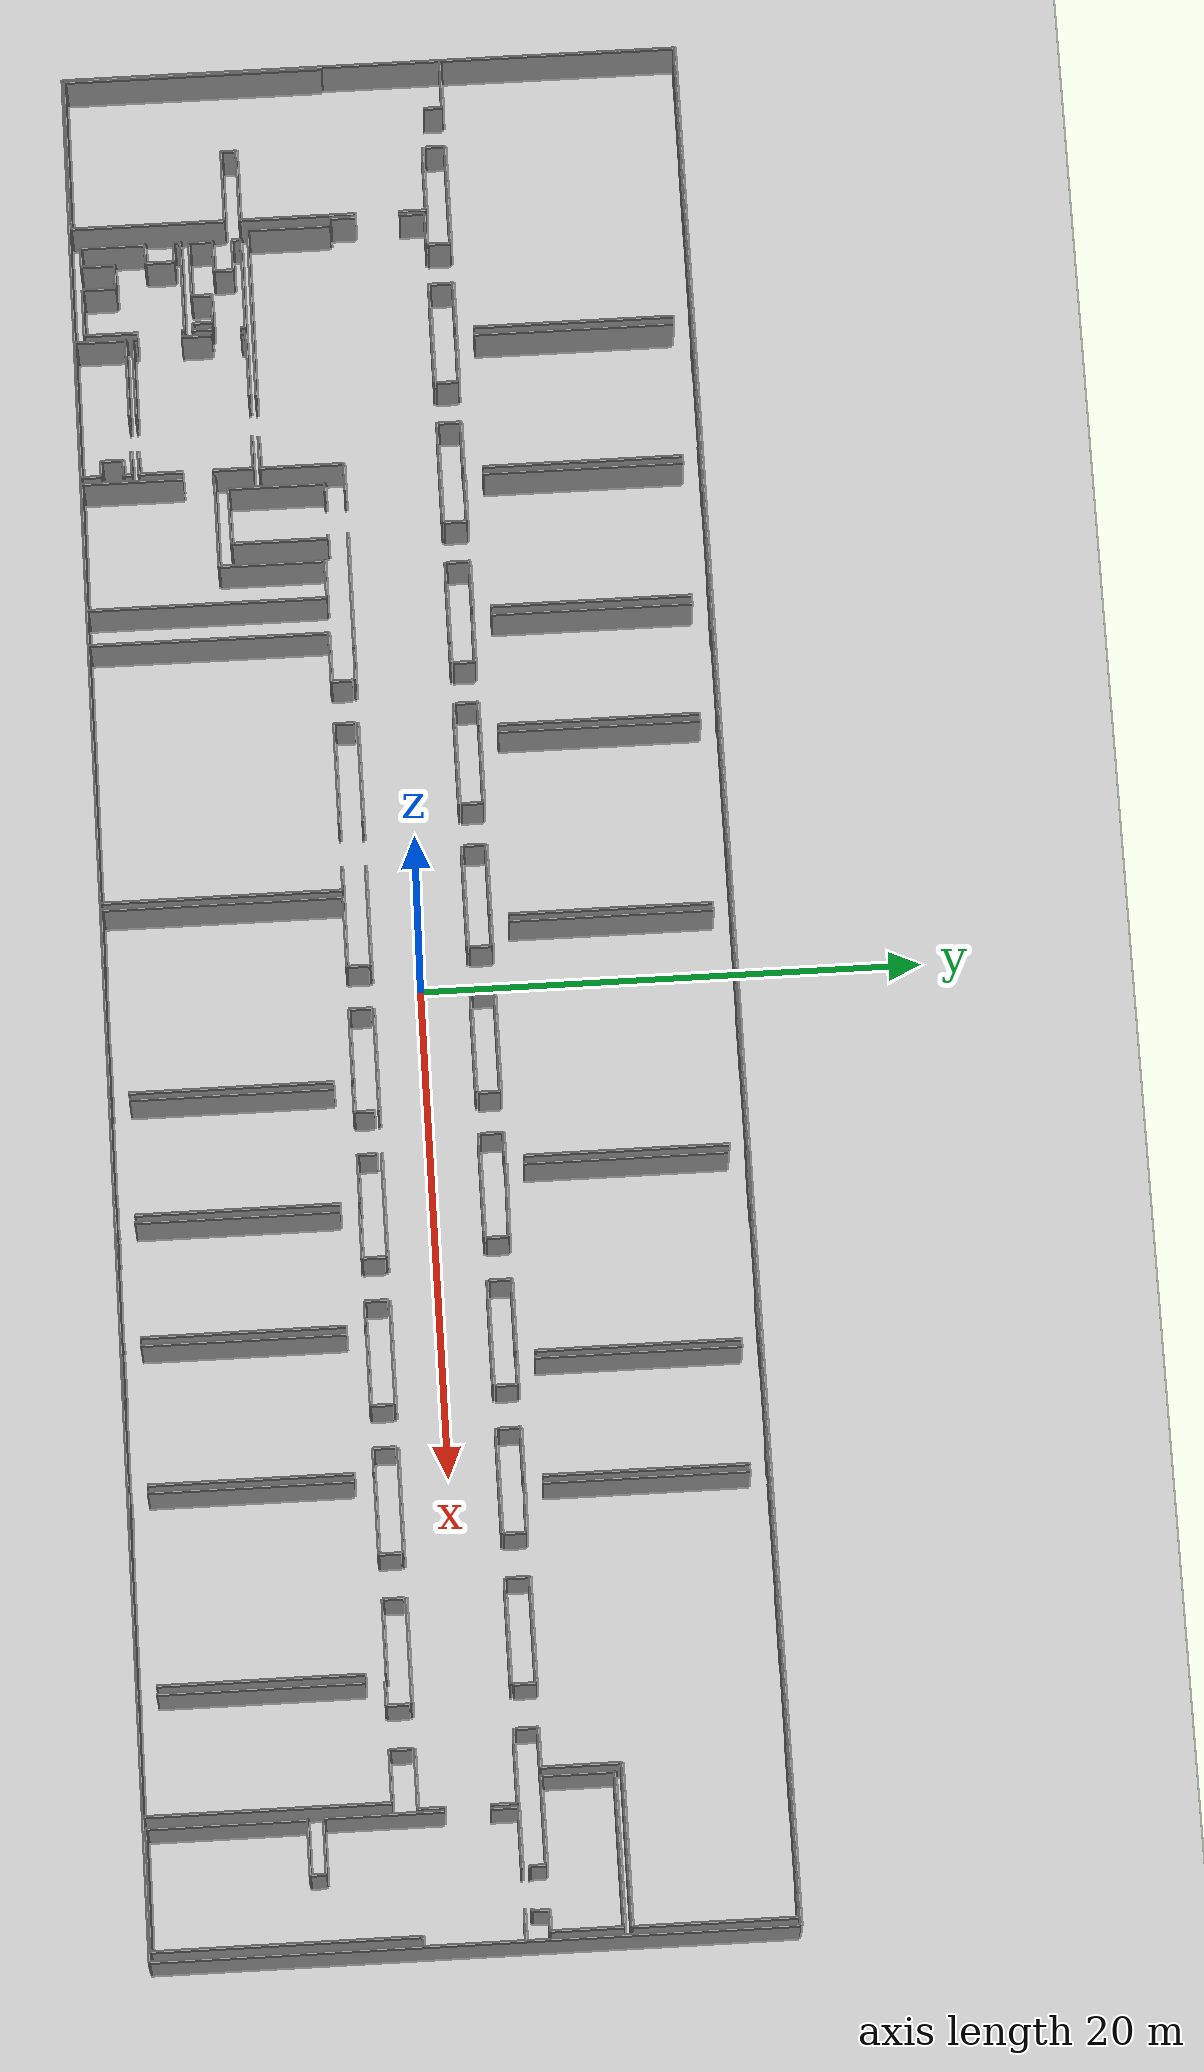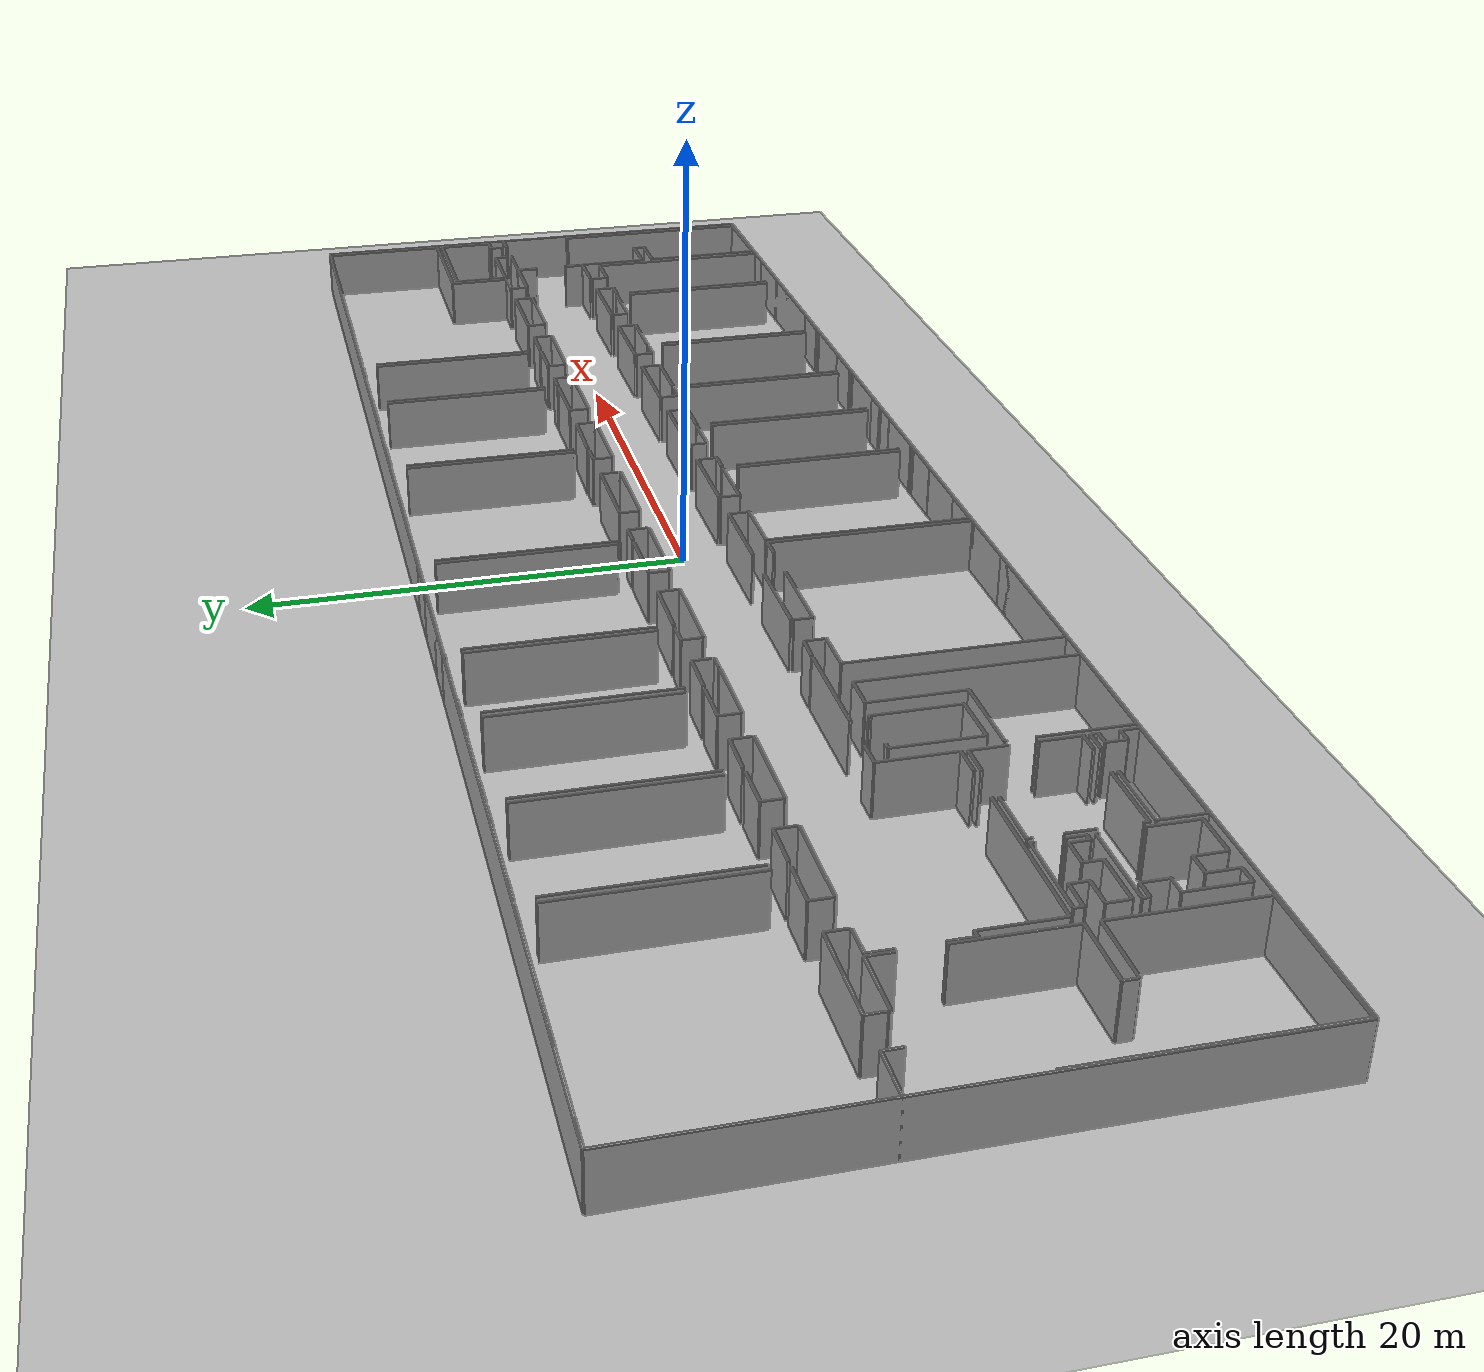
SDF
<sdf version="1.6">
  <world name="default">
    <light name="sun" type="directional">
      <cast_shadows>1</cast_shadows>
      <pose frame="">0 0 10 0 -0 0</pose>
      <diffuse>0.8 0.8 0.8 1</diffuse>
      <specular>0.1 0.1 0.1 1</specular>
      <attenuation>
        <range>1000</range>
        <constant>0.9</constant>
        <linear>0.01</linear>
        <quadratic>0.001</quadratic>
      </attenuation>
      <direction>-0.5 0.5 -1</direction>
    </light>
    <model name="ground_plane">
      <static>1</static>
      <link name="link">
        <collision name="collision">
          <geometry>
            <plane>
              <normal>0 0 1</normal>
              <size>100 100</size>
            </plane>
          </geometry>
          <surface>
            <friction>
              <ode>
                <mu>100</mu>
                <mu2>50</mu2>
              </ode>
              <torsional>
                <ode />
              </torsional>
            </friction>
            <contact>
              <ode />
            </contact>
            <bounce />
          </surface>
          <max_contacts>10</max_contacts>
        </collision>
        <visual name="visual">
          <cast_shadows>0</cast_shadows>
          <geometry>
            <plane>
              <normal>0 0 1</normal>
              <size>100 100</size>
            </plane>
          </geometry>
          <material>
            <script>
              <uri>file://media/materials/scripts/gazebo.material</uri>
              <name>Gazebo/Grey</name>
            </script>
          </material>
        </visual>
        <self_collide>0</self_collide>
        <kinematic>0</kinematic>
        <gravity>1</gravity>
      </link>
    </model>
    <gravity>0 0 -9.8</gravity>
    <magnetic_field>6e-06 2.3e-05 -4.2e-05</magnetic_field>
    <atmosphere type="adiabatic" />
    <physics default="0" name="default_physics" type="ode">
      <max_step_size>0.001</max_step_size>
      <real_time_factor>1</real_time_factor>
      <real_time_update_rate>1000</real_time_update_rate>
    </physics>
    <scene>
      <ambient>0.4 0.4 0.4 1</ambient>
      <background>0.7 0.7 0.7 1</background>
      <shadows>1</shadows>
    </scene>
    <spherical_coordinates>
      <surface_model>EARTH_WGS84</surface_model>
      <latitude_deg>0</latitude_deg>
      <longitude_deg>0</longitude_deg>
      <elevation>0</elevation>
      <heading_deg>0</heading_deg>
    </spherical_coordinates>
  <model name="50052751">
		<static>1</static>
		<link name="Wall_0">
			<collision name="Wall_0_Collision">
				<geometry>
					<box>
						<size>2.06881151815 0.1 2.5</size>
					</box>
				</geometry>
				<pose frame="">1.03440575908 0 1.25 0 0 0</pose>
			</collision>
			<visual name="Wall_0_Visual">
				<pose frame="">1.03440575908 0 1.25 0 0 0</pose>
				<geometry>
					<box>
						<size>2.06881151815 0.1 2.5</size>
					</box>
				</geometry>
				<material>
					<script>
						<uri>file://media/materials/scripts/gazebo.material</uri>
						<name>Gazebo/Grey</name>
					</script>
					<ambient>1 1 1 1</ambient>
				</material>
			</visual>
			<pose frame="">0.0 -9.61859063008 0 0 0 0.0</pose>
		</link>
		<link name="Wall_1">
			<collision name="Wall_1_Collision">
				<geometry>
					<box>
						<size>0.788015965856 0.1 2.5</size>
					</box>
				</geometry>
				<pose frame="">0.394007982928 0 1.25 0 0 0</pose>
			</collision>
			<visual name="Wall_1_Visual">
				<pose frame="">0.394007982928 0 1.25 0 0 0</pose>
				<geometry>
					<box>
						<size>0.788015965856 0.1 2.5</size>
					</box>
				</geometry>
				<material>
					<script>
						<uri>file://media/materials/scripts/gazebo.material</uri>
						<name>Gazebo/Grey</name>
					</script>
					<ambient>1 1 1 1</ambient>
				</material>
			</visual>
			<pose frame="">2.06881151815 -9.61859063008 0 0 0 -1.57079632679</pose>
		</link>
		<link name="Wall_2">
			<collision name="Wall_2_Collision">
				<geometry>
					<box>
						<size>0.789919079603 0.1 2.5</size>
					</box>
				</geometry>
				<pose frame="">0.394959539802 0 1.25 0 0 0</pose>
			</collision>
			<visual name="Wall_2_Visual">
				<pose frame="">0.394959539802 0 1.25 0 0 0</pose>
				<geometry>
					<box>
						<size>0.789919079603 0.1 2.5</size>
					</box>
				</geometry>
				<material>
					<script>
						<uri>file://media/materials/scripts/gazebo.material</uri>
						<name>Gazebo/Grey</name>
					</script>
					<ambient>1 1 1 1</ambient>
				</material>
			</visual>
			<pose frame="">3.77565080146 -10.4066065959 0 0 0 1.57079632679</pose>
		</link>
		<link name="Wall_3">
			<collision name="Wall_3_Collision">
				<geometry>
					<box>
						<size>4.24952612468 0.1 2.5</size>
					</box>
				</geometry>
				<pose frame="">2.12476306234 0 1.25 0 0 0</pose>
			</collision>
			<visual name="Wall_3_Visual">
				<pose frame="">2.12476306234 0 1.25 0 0 0</pose>
				<geometry>
					<box>
						<size>4.24952612468 0.1 2.5</size>
					</box>
				</geometry>
				<material>
					<script>
						<uri>file://media/materials/scripts/gazebo.material</uri>
						<name>Gazebo/Grey</name>
					</script>
					<ambient>1 1 1 1</ambient>
				</material>
			</visual>
			<pose frame="">3.77565080146 -9.61668751634 0 0 0 0.0</pose>
		</link>
		<link name="Wall_4">
			<collision name="Wall_4_Collision">
				<geometry>
					<box>
						<size>0.919077065957 0.1 2.5</size>
					</box>
				</geometry>
				<pose frame="">0.459538532978 0 1.25 0 0 0</pose>
			</collision>
			<visual name="Wall_4_Visual">
				<pose frame="">0.459538532978 0 1.25 0 0 0</pose>
				<geometry>
					<box>
						<size>0.919077065957 0.1 2.5</size>
					</box>
				</geometry>
				<material>
					<script>
						<uri>file://media/materials/scripts/gazebo.material</uri>
						<name>Gazebo/Grey</name>
					</script>
					<ambient>1 1 1 1</ambient>
				</material>
			</visual>
			<pose frame="">8.02517692614 -9.61668751634 0 0 0 -1.57079632679</pose>
		</link>
		<link name="Wall_5">
			<collision name="Wall_5_Collision">
				<geometry>
					<box>
						<size>0.919077065957 0.1 2.5</size>
					</box>
				</geometry>
				<pose frame="">0.459538532978 0 1.25 0 0 0</pose>
			</collision>
			<visual name="Wall_5_Visual">
				<pose frame="">0.459538532978 0 1.25 0 0 0</pose>
				<geometry>
					<box>
						<size>0.919077065957 0.1 2.5</size>
					</box>
				</geometry>
				<material>
					<script>
						<uri>file://media/materials/scripts/gazebo.material</uri>
						<name>Gazebo/Grey</name>
					</script>
					<ambient>1 1 1 1</ambient>
				</material>
			</visual>
			<pose frame="">9.77096660416 -10.5357645823 0 0 0 1.57079632679</pose>
		</link>
		<link name="Wall_6">
			<collision name="Wall_6_Collision">
				<geometry>
					<box>
						<size>1.95551281303 0.1 2.5</size>
					</box>
				</geometry>
				<pose frame="">0.977756406515 0 1.25 0 0 0</pose>
			</collision>
			<visual name="Wall_6_Visual">
				<pose frame="">0.977756406515 0 1.25 0 0 0</pose>
				<geometry>
					<box>
						<size>1.95551281303 0.1 2.5</size>
					</box>
				</geometry>
				<material>
					<script>
						<uri>file://media/materials/scripts/gazebo.material</uri>
						<name>Gazebo/Grey</name>
					</script>
					<ambient>1 1 1 1</ambient>
				</material>
			</visual>
			<pose frame="">9.77096660416 -9.61668751634 0 0 0 0.0</pose>
		</link>
		<link name="Wall_7">
			<collision name="Wall_7_Collision">
				<geometry>
					<box>
						<size>8.12515383503 0.1 2.5</size>
					</box>
				</geometry>
				<pose frame="">4.06257691751 0 1.25 0 0 0</pose>
			</collision>
			<visual name="Wall_7_Visual">
				<pose frame="">4.06257691751 0 1.25 0 0 0</pose>
				<geometry>
					<box>
						<size>8.12515383503 0.1 2.5</size>
					</box>
				</geometry>
				<material>
					<script>
						<uri>file://media/materials/scripts/gazebo.material</uri>
						<name>Gazebo/Grey</name>
					</script>
					<ambient>1 1 1 1</ambient>
				</material>
			</visual>
			<pose frame="">11.7264794172 -8.89629552565 0 0 0 1.57079632679</pose>
		</link>
		<link name="Wall_8">
			<collision name="Wall_8_Collision">
				<geometry>
					<box>
						<size>1.17663179316 0.1 2.5</size>
					</box>
				</geometry>
				<pose frame="">0.588315896582 0 1.25 0 0 0</pose>
			</collision>
			<visual name="Wall_8_Visual">
				<pose frame="">0.588315896582 0 1.25 0 0 0</pose>
				<geometry>
					<box>
						<size>1.17663179316 0.1 2.5</size>
					</box>
				</geometry>
				<material>
					<script>
						<uri>file://media/materials/scripts/gazebo.material</uri>
						<name>Gazebo/Grey</name>
					</script>
					<ambient>1 1 1 1</ambient>
				</material>
			</visual>
			<pose frame="">11.7264794172 -0.00786620349107 0 0 0 3.14159265359</pose>
		</link>
		<link name="Wall_9">
			<collision name="Wall_9_Collision">
				<geometry>
					<box>
						<size>2.75025311413 0.1 2.5</size>
					</box>
				</geometry>
				<pose frame="">1.37512655706 0 1.25 0 0 0</pose>
			</collision>
			<visual name="Wall_9_Visual">
				<pose frame="">1.37512655706 0 1.25 0 0 0</pose>
				<geometry>
					<box>
						<size>2.75025311413 0.1 2.5</size>
					</box>
				</geometry>
				<material>
					<script>
						<uri>file://media/materials/scripts/gazebo.material</uri>
						<name>Gazebo/Grey</name>
					</script>
					<ambient>1 1 1 1</ambient>
				</material>
			</visual>
			<pose frame="">7.28232819323 -0.00786620349107 0 0 0 3.14159265359</pose>
		</link>
		<link name="Wall_10">
			<collision name="Wall_10_Collision">
				<geometry>
					<box>
						<size>1.28675864204 0.1 2.5</size>
					</box>
				</geometry>
				<pose frame="">0.64337932102 0 1.25 0 0 0</pose>
			</collision>
			<visual name="Wall_10_Visual">
				<pose frame="">0.64337932102 0 1.25 0 0 0</pose>
				<geometry>
					<box>
						<size>1.28675864204 0.1 2.5</size>
					</box>
				</geometry>
				<material>
					<script>
						<uri>file://media/materials/scripts/gazebo.material</uri>
						<name>Gazebo/Grey</name>
					</script>
					<ambient>1 1 1 1</ambient>
				</material>
			</visual>
			<pose frame="">1.28980362404 -0.00786620349107 0 0 0 3.14159265359</pose>
		</link>
		<link name="Wall_11">
			<collision name="Wall_11_Collision">
				<geometry>
					<box>
						<size>9.61072490897 0.1 2.5</size>
					</box>
				</geometry>
				<pose frame="">4.80536245448 0 1.25 0 0 0</pose>
			</collision>
			<visual name="Wall_11_Visual">
				<pose frame="">4.80536245448 0 1.25 0 0 0</pose>
				<geometry>
					<box>
						<size>9.61072490897 0.1 2.5</size>
					</box>
				</geometry>
				<material>
					<script>
						<uri>file://media/materials/scripts/gazebo.material</uri>
						<name>Gazebo/Grey</name>
					</script>
					<ambient>1 1 1 1</ambient>
				</material>
			</visual>
			<pose frame="">0.00304498199655 -0.00786620349107 0 0 0 -1.57111315847</pose>
		</link>
		<link name="Wall_12">
			<collision name="Wall_12_Collision">
				<geometry>
					<box>
						<size>10.5143228341 0.1 2.5</size>
					</box>
				</geometry>
				<pose frame="">5.25716141703 0 1.25 0 0 0</pose>
			</collision>
			<visual name="Wall_12_Visual">
				<pose frame="">5.25716141703 0 1.25 0 0 0</pose>
				<geometry>
					<box>
						<size>10.5143228341 0.1 2.5</size>
					</box>
				</geometry>
				<material>
					<script>
						<uri>file://media/materials/scripts/gazebo.material</uri>
						<name>Gazebo/Grey</name>
					</script>
					<ambient>1 1 1 1</ambient>
				</material>
			</visual>
			<pose frame="">0.0749826816649 -24.9932122276 0 0 0 1.57079632679</pose>
		</link>
		<link name="Wall_13">
			<collision name="Wall_13_Collision">
				<geometry>
					<box>
						<size>2.73617007239 0.1 2.5</size>
					</box>
				</geometry>
				<pose frame="">1.3680850362 0 1.25 0 0 0</pose>
			</collision>
			<visual name="Wall_13_Visual">
				<pose frame="">1.3680850362 0 1.25 0 0 0</pose>
				<geometry>
					<box>
						<size>2.73617007239 0.1 2.5</size>
					</box>
				</geometry>
				<material>
					<script>
						<uri>file://media/materials/scripts/gazebo.material</uri>
						<name>Gazebo/Grey</name>
					</script>
					<ambient>1 1 1 1</ambient>
				</material>
			</visual>
			<pose frame="">3.78732323245 -10.5291671213 0 0 0 0.0</pose>
		</link>
		<link name="Wall_14">
			<collision name="Wall_14_Collision">
				<geometry>
					<box>
						<size>1.10824657249 0.1 2.5</size>
					</box>
				</geometry>
				<pose frame="">0.554123286246 0 1.25 0 0 0</pose>
			</collision>
			<visual name="Wall_14_Visual">
				<pose frame="">0.554123286246 0 1.25 0 0 0</pose>
				<geometry>
					<box>
						<size>1.10824657249 0.1 2.5</size>
					</box>
				</geometry>
				<material>
					<script>
						<uri>file://media/materials/scripts/gazebo.material</uri>
						<name>Gazebo/Grey</name>
					</script>
					<ambient>1 1 1 1</ambient>
				</material>
			</visual>
			<pose frame="">6.52349330485 -10.5291671213 0 0 0 -1.57079632679</pose>
		</link>
		<link name="Wall_15">
			<collision name="Wall_15_Collision">
				<geometry>
					<box>
						<size>4.72378207064 0.1 2.5</size>
					</box>
				</geometry>
				<pose frame="">2.36189103532 0 1.25 0 0 0</pose>
			</collision>
			<visual name="Wall_15_Visual">
				<pose frame="">2.36189103532 0 1.25 0 0 0</pose>
				<geometry>
					<box>
						<size>4.72378207064 0.1 2.5</size>
					</box>
				</geometry>
				<material>
					<script>
						<uri>file://media/materials/scripts/gazebo.material</uri>
						<name>Gazebo/Grey</name>
					</script>
					<ambient>1 1 1 1</ambient>
				</material>
			</visual>
			<pose frame="">6.52349330485 -13.4069288565 0 0 0 -1.57079632679</pose>
		</link>
		<link name="Wall_16">
			<collision name="Wall_16_Collision">
				<geometry>
					<box>
						<size>3.02810772131 0.1 2.5</size>
					</box>
				</geometry>
				<pose frame="">1.51405386066 0 1.25 0 0 0</pose>
			</collision>
			<visual name="Wall_16_Visual">
				<pose frame="">1.51405386066 0 1.25 0 0 0</pose>
				<geometry>
					<box>
						<size>3.02810772131 0.1 2.5</size>
					</box>
				</geometry>
				<material>
					<script>
						<uri>file://media/materials/scripts/gazebo.material</uri>
						<name>Gazebo/Grey</name>
					</script>
					<ambient>1 1 1 1</ambient>
				</material>
			</visual>
			<pose frame="">6.52349330485 -18.1307109272 0 0 0 3.14159265359</pose>
		</link>
		<link name="Wall_17">
			<collision name="Wall_17_Collision">
				<geometry>
					<box>
						<size>0.614198243553 0.1 2.5</size>
					</box>
				</geometry>
				<pose frame="">0.307099121776 0 1.25 0 0 0</pose>
			</collision>
			<visual name="Wall_17_Visual">
				<pose frame="">0.307099121776 0 1.25 0 0 0</pose>
				<geometry>
					<box>
						<size>0.614198243553 0.1 2.5</size>
					</box>
				</geometry>
				<material>
					<script>
						<uri>file://media/materials/scripts/gazebo.material</uri>
						<name>Gazebo/Grey</name>
					</script>
					<ambient>1 1 1 1</ambient>
				</material>
			</visual>
			<pose frame="">3.49538558353 -18.1307109272 0 0 0 -1.57079632679</pose>
		</link>
		<link name="Wall_18">
			<collision name="Wall_18_Collision">
				<geometry>
					<box>
						<size>3.02810772131 0.1 2.5</size>
					</box>
				</geometry>
				<pose frame="">1.51405386066 0 1.25 0 0 0</pose>
			</collision>
			<visual name="Wall_18_Visual">
				<pose frame="">1.51405386066 0 1.25 0 0 0</pose>
				<geometry>
					<box>
						<size>3.02810772131 0.1 2.5</size>
					</box>
				</geometry>
				<material>
					<script>
						<uri>file://media/materials/scripts/gazebo.material</uri>
						<name>Gazebo/Grey</name>
					</script>
					<ambient>1 1 1 1</ambient>
				</material>
			</visual>
			<pose frame="">3.49538558353 -18.7449091707 0 0 0 0.0</pose>
		</link>
		<link name="Wall_19">
			<collision name="Wall_19_Collision">
				<geometry>
					<box>
						<size>6.24081747617 0.1 2.5</size>
					</box>
				</geometry>
				<pose frame="">3.12040873808 0 1.25 0 0 0</pose>
			</collision>
			<visual name="Wall_19_Visual">
				<pose frame="">3.12040873808 0 1.25 0 0 0</pose>
				<geometry>
					<box>
						<size>6.24081747617 0.1 2.5</size>
					</box>
				</geometry>
				<material>
					<script>
						<uri>file://media/materials/scripts/gazebo.material</uri>
						<name>Gazebo/Grey</name>
					</script>
					<ambient>1 1 1 1</ambient>
				</material>
			</visual>
			<pose frame="">6.52349330485 -18.7449091707 0 0 0 -1.57079632679</pose>
		</link>
		<link name="Wall_20">
			<collision name="Wall_20_Collision">
				<geometry>
					<box>
						<size>6.4485149679 0.1 2.5</size>
					</box>
				</geometry>
				<pose frame="">3.22425748395 0 1.25 0 0 0</pose>
			</collision>
			<visual name="Wall_20_Visual">
				<pose frame="">3.22425748395 0 1.25 0 0 0</pose>
				<geometry>
					<box>
						<size>6.4485149679 0.1 2.5</size>
					</box>
				</geometry>
				<material>
					<script>
						<uri>file://media/materials/scripts/gazebo.material</uri>
						<name>Gazebo/Grey</name>
					</script>
					<ambient>1 1 1 1</ambient>
				</material>
			</visual>
			<pose frame="">6.52349330485 -24.9857266469 0 0 0 -3.14043183091</pose>
		</link>
		<link name="Wall_21">
			<collision name="Wall_21_Collision">
				<geometry>
					<box>
						<size>3.3520176812 0.1 2.5</size>
					</box>
				</geometry>
				<pose frame="">1.6760088406 0 1.25 0 0 0</pose>
			</collision>
			<visual name="Wall_21_Visual">
				<pose frame="">1.6760088406 0 1.25 0 0 0</pose>
				<geometry>
					<box>
						<size>3.3520176812 0.1 2.5</size>
					</box>
				</geometry>
				<material>
					<script>
						<uri>file://media/materials/scripts/gazebo.material</uri>
						<name>Gazebo/Grey</name>
					</script>
					<ambient>1 1 1 1</ambient>
				</material>
			</visual>
			<pose frame="">6.97567313133 -17.8328101885 0 0 0 1.57079632679</pose>
		</link>
		<link name="Wall_22">
			<collision name="Wall_22_Collision">
				<geometry>
					<box>
						<size>0.312745025895 0.1 2.5</size>
					</box>
				</geometry>
				<pose frame="">0.156372512948 0 1.25 0 0 0</pose>
			</collision>
			<visual name="Wall_22_Visual">
				<pose frame="">0.156372512948 0 1.25 0 0 0</pose>
				<geometry>
					<box>
						<size>0.312745025895 0.1 2.5</size>
					</box>
				</geometry>
				<material>
					<script>
						<uri>file://media/materials/scripts/gazebo.material</uri>
						<name>Gazebo/Grey</name>
					</script>
					<ambient>1 1 1 1</ambient>
				</material>
			</visual>
			<pose frame="">6.97567313133 -14.4807925073 0 0 0 3.14159265359</pose>
		</link>
		<link name="Wall_23">
			<collision name="Wall_23_Collision">
				<geometry>
					<box>
						<size>1.07310240528 0.1 2.5</size>
					</box>
				</geometry>
				<pose frame="">0.536551202641 0 1.25 0 0 0</pose>
			</collision>
			<visual name="Wall_23_Visual">
				<pose frame="">0.536551202641 0 1.25 0 0 0</pose>
				<geometry>
					<box>
						<size>1.07310240528 0.1 2.5</size>
					</box>
				</geometry>
				<material>
					<script>
						<uri>file://media/materials/scripts/gazebo.material</uri>
						<name>Gazebo/Grey</name>
					</script>
					<ambient>1 1 1 1</ambient>
				</material>
			</visual>
			<pose frame="">6.66292810544 -14.4807925073 0 0 0 1.57079632679</pose>
		</link>
		<link name="Wall_24">
			<collision name="Wall_24_Collision">
				<geometry>
					<box>
						<size>1.04709318406 0.1 2.5</size>
					</box>
				</geometry>
				<pose frame="">0.523546592031 0 1.25 0 0 0</pose>
			</collision>
			<visual name="Wall_24_Visual">
				<pose frame="">0.523546592031 0 1.25 0 0 0</pose>
				<geometry>
					<box>
						<size>1.04709318406 0.1 2.5</size>
					</box>
				</geometry>
				<material>
					<script>
						<uri>file://media/materials/scripts/gazebo.material</uri>
						<name>Gazebo/Grey</name>
					</script>
					<ambient>1 1 1 1</ambient>
				</material>
			</visual>
			<pose frame="">6.66292810544 -11.639570556 0 0 0 1.57079632679</pose>
		</link>
		<link name="Wall_25">
			<collision name="Wall_25_Collision">
				<geometry>
					<box>
						<size>1.33852333598 0.1 2.5</size>
					</box>
				</geometry>
				<pose frame="">0.66926166799 0 1.25 0 0 0</pose>
			</collision>
			<visual name="Wall_25_Visual">
				<pose frame="">0.66926166799 0 1.25 0 0 0</pose>
				<geometry>
					<box>
						<size>1.33852333598 0.1 2.5</size>
					</box>
				</geometry>
				<material>
					<script>
						<uri>file://media/materials/scripts/gazebo.material</uri>
						<name>Gazebo/Grey</name>
					</script>
					<ambient>1 1 1 1</ambient>
				</material>
			</visual>
			<pose frame="">6.66292810544 -10.592477372 0 0 0 0.0</pose>
		</link>
		<link name="Wall_26">
			<collision name="Wall_26_Collision">
				<geometry>
					<box>
						<size>4.28708090263 0.1 2.5</size>
					</box>
				</geometry>
				<pose frame="">2.14354045132 0 1.25 0 0 0</pose>
			</collision>
			<visual name="Wall_26_Visual">
				<pose frame="">2.14354045132 0 1.25 0 0 0</pose>
				<geometry>
					<box>
						<size>4.28708090263 0.1 2.5</size>
					</box>
				</geometry>
				<material>
					<script>
						<uri>file://media/materials/scripts/gazebo.material</uri>
						<name>Gazebo/Grey</name>
					</script>
					<ambient>1 1 1 1</ambient>
				</material>
			</visual>
			<pose frame="">9.75345795768 -10.592477372 0 0 0 0.0</pose>
		</link>
		<link name="Wall_27">
			<collision name="Wall_27_Collision">
				<geometry>
					<box>
						<size>4.26284792091 0.1 2.5</size>
					</box>
				</geometry>
				<pose frame="">2.13142396046 0 1.25 0 0 0</pose>
			</collision>
			<visual name="Wall_27_Visual">
				<pose frame="">2.13142396046 0 1.25 0 0 0</pose>
				<geometry>
					<box>
						<size>4.26284792091 0.1 2.5</size>
					</box>
				</geometry>
				<material>
					<script>
						<uri>file://media/materials/scripts/gazebo.material</uri>
						<name>Gazebo/Grey</name>
					</script>
					<ambient>1 1 1 1</ambient>
				</material>
			</visual>
			<pose frame="">15.7834104306 -10.592477372 0 0 0 0.0</pose>
		</link>
		<link name="Wall_28">
			<collision name="Wall_28_Collision">
				<geometry>
					<box>
						<size>3.40873047088 0.1 2.5</size>
					</box>
				</geometry>
				<pose frame="">1.70436523544 0 1.25 0 0 0</pose>
			</collision>
			<visual name="Wall_28_Visual">
				<pose frame="">1.70436523544 0 1.25 0 0 0</pose>
				<geometry>
					<box>
						<size>3.40873047088 0.1 2.5</size>
					</box>
				</geometry>
				<material>
					<script>
						<uri>file://media/materials/scripts/gazebo.material</uri>
						<name>Gazebo/Grey</name>
					</script>
					<ambient>1 1 1 1</ambient>
				</material>
			</visual>
			<pose frame="">21.7813905925 -10.592477372 0 0 0 0.0</pose>
		</link>
		<link name="Wall_29">
			<collision name="Wall_29_Collision">
				<geometry>
					<box>
						<size>4.91980278667 0.1 2.5</size>
					</box>
				</geometry>
				<pose frame="">2.45990139333 0 1.25 0 0 0</pose>
			</collision>
			<visual name="Wall_29_Visual">
				<pose frame="">2.45990139333 0 1.25 0 0 0</pose>
				<geometry>
					<box>
						<size>4.91980278667 0.1 2.5</size>
					</box>
				</geometry>
				<material>
					<script>
						<uri>file://media/materials/scripts/gazebo.material</uri>
						<name>Gazebo/Grey</name>
					</script>
					<ambient>1 1 1 1</ambient>
				</material>
			</visual>
			<pose frame="">25.1901210634 -14.4466633341 0 0 0 3.14159265359</pose>
		</link>
		<link name="Wall_30">
			<collision name="Wall_30_Collision">
				<geometry>
					<box>
						<size>1.15341380544 0.1 2.5</size>
					</box>
				</geometry>
				<pose frame="">0.57670690272 0 1.25 0 0 0</pose>
			</collision>
			<visual name="Wall_30_Visual">
				<pose frame="">0.57670690272 0 1.25 0 0 0</pose>
				<geometry>
					<box>
						<size>1.15341380544 0.1 2.5</size>
					</box>
				</geometry>
				<material>
					<script>
						<uri>file://media/materials/scripts/gazebo.material</uri>
						<name>Gazebo/Grey</name>
					</script>
					<ambient>1 1 1 1</ambient>
				</material>
			</visual>
			<pose frame="">18.4655320725 -14.4466633341 0 0 0 3.14159265359</pose>
		</link>
		<link name="Wall_31">
			<collision name="Wall_31_Collision">
				<geometry>
					<box>
						<size>3.38728872266 0.1 2.5</size>
					</box>
				</geometry>
				<pose frame="">1.69364436133 0 1.25 0 0 0</pose>
			</collision>
			<visual name="Wall_31_Visual">
				<pose frame="">1.69364436133 0 1.25 0 0 0</pose>
				<geometry>
					<box>
						<size>3.38728872266 0.1 2.5</size>
					</box>
				</geometry>
				<material>
					<script>
						<uri>file://media/materials/scripts/gazebo.material</uri>
						<name>Gazebo/Grey</name>
					</script>
					<ambient>1 1 1 1</ambient>
				</material>
			</visual>
			<pose frame="">17.3121182671 -14.4466633341 0 0 0 -1.57079632679</pose>
		</link>
		<link name="Wall_32">
			<collision name="Wall_32_Collision">
				<geometry>
					<box>
						<size>1.38166058093 0.1 2.5</size>
					</box>
				</geometry>
				<pose frame="">0.690830290466 0 1.25 0 0 0</pose>
			</collision>
			<visual name="Wall_32_Visual">
				<pose frame="">0.690830290466 0 1.25 0 0 0</pose>
				<geometry>
					<box>
						<size>1.38166058093 0.1 2.5</size>
					</box>
				</geometry>
				<material>
					<script>
						<uri>file://media/materials/scripts/gazebo.material</uri>
						<name>Gazebo/Grey</name>
					</script>
					<ambient>1 1 1 1</ambient>
				</material>
			</visual>
			<pose frame="">17.3121182671 -17.8339520568 0 0 0 3.14159265359</pose>
		</link>
		<link name="Wall_33">
			<collision name="Wall_33_Collision">
				<geometry>
					<box>
						<size>7.18932945877 0.1 2.5</size>
					</box>
				</geometry>
				<pose frame="">3.59466472939 0 1.25 0 0 0</pose>
			</collision>
			<visual name="Wall_33_Visual">
				<pose frame="">3.59466472939 0 1.25 0 0 0</pose>
				<geometry>
					<box>
						<size>7.18932945877 0.1 2.5</size>
					</box>
				</geometry>
				<material>
					<script>
						<uri>file://media/materials/scripts/gazebo.material</uri>
						<name>Gazebo/Grey</name>
					</script>
					<ambient>1 1 1 1</ambient>
				</material>
			</visual>
			<pose frame="">14.1650024994 -17.8339520568 0 0 0 3.14143382539</pose>
		</link>
		<link name="Wall_34">
			<collision name="Wall_34_Collision">
				<geometry>
					<box>
						<size>0.203125674019 0.1 2.5</size>
					</box>
				</geometry>
				<pose frame="">0.10156283701 0 1.25 0 0 0</pose>
			</collision>
			<visual name="Wall_34_Visual">
				<pose frame="">0.10156283701 0 1.25 0 0 0</pose>
				<geometry>
					<box>
						<size>0.203125674019 0.1 2.5</size>
					</box>
				</geometry>
				<material>
					<script>
						<uri>file://media/materials/scripts/gazebo.material</uri>
						<name>Gazebo/Grey</name>
					</script>
					<ambient>1 1 1 1</ambient>
				</material>
			</visual>
			<pose frame="">11.465372211 -22.7219094067 0 0 0 1.57079632679</pose>
		</link>
		<link name="Wall_35">
			<collision name="Wall_35_Collision">
				<geometry>
					<box>
						<size>1.24032266659 0.1 2.5</size>
					</box>
				</geometry>
				<pose frame="">0.620161333296 0 1.25 0 0 0</pose>
			</collision>
			<visual name="Wall_35_Visual">
				<pose frame="">0.620161333296 0 1.25 0 0 0</pose>
				<geometry>
					<box>
						<size>1.24032266659 0.1 2.5</size>
					</box>
				</geometry>
				<material>
					<script>
						<uri>file://media/materials/scripts/gazebo.material</uri>
						<name>Gazebo/Grey</name>
					</script>
					<ambient>1 1 1 1</ambient>
				</material>
			</visual>
			<pose frame="">11.465372211 -20.7415292407 0 0 0 1.57079632679</pose>
		</link>
		<link name="Wall_36">
			<collision name="Wall_36_Collision">
				<geometry>
					<box>
						<size>0.219492452251 0.1 2.5</size>
					</box>
				</geometry>
				<pose frame="">0.109746226125 0 1.25 0 0 0</pose>
			</collision>
			<visual name="Wall_36_Visual">
				<pose frame="">0.109746226125 0 1.25 0 0 0</pose>
				<geometry>
					<box>
						<size>0.219492452251 0.1 2.5</size>
					</box>
				</geometry>
				<material>
					<script>
						<uri>file://media/materials/scripts/gazebo.material</uri>
						<name>Gazebo/Grey</name>
					</script>
					<ambient>1 1 1 1</ambient>
				</material>
			</visual>
			<pose frame="">11.465372211 -18.3295228767 0 0 0 1.57079632679</pose>
		</link>
		<link name="Wall_37">
			<collision name="Wall_37_Collision">
				<geometry>
					<box>
						<size>2.68009165396 0.1 2.5</size>
					</box>
				</geometry>
				<pose frame="">1.34004582698 0 1.25 0 0 0</pose>
			</collision>
			<visual name="Wall_37_Visual">
				<pose frame="">1.34004582698 0 1.25 0 0 0</pose>
				<geometry>
					<box>
						<size>2.68009165396 0.1 2.5</size>
					</box>
				</geometry>
				<material>
					<script>
						<uri>file://media/materials/scripts/gazebo.material</uri>
						<name>Gazebo/Grey</name>
					</script>
					<ambient>1 1 1 1</ambient>
				</material>
			</visual>
			<pose frame="">11.465372211 -18.1100304244 0 0 0 0.0</pose>
		</link>
		<link name="Wall_38">
			<collision name="Wall_38_Collision">
				<geometry>
					<box>
						<size>1.39282551492 0.1 2.5</size>
					</box>
				</geometry>
				<pose frame="">0.69641275746 0 1.25 0 0 0</pose>
			</collision>
			<visual name="Wall_38_Visual">
				<pose frame="">0.69641275746 0 1.25 0 0 0</pose>
				<geometry>
					<box>
						<size>1.39282551492 0.1 2.5</size>
					</box>
				</geometry>
				<material>
					<script>
						<uri>file://media/materials/scripts/gazebo.material</uri>
						<name>Gazebo/Grey</name>
					</script>
					<ambient>1 1 1 1</ambient>
				</material>
			</visual>
			<pose frame="">15.8975972555 -18.1100304244 0 0 0 0.0</pose>
		</link>
		<link name="Wall_39">
			<collision name="Wall_39_Collision">
				<geometry>
					<box>
						<size>1.64505152363 0.1 2.5</size>
					</box>
				</geometry>
				<pose frame="">0.822525761816 0 1.25 0 0 0</pose>
			</collision>
			<visual name="Wall_39_Visual">
				<pose frame="">0.822525761816 0 1.25 0 0 0</pose>
				<geometry>
					<box>
						<size>1.64505152363 0.1 2.5</size>
					</box>
				</geometry>
				<material>
					<script>
						<uri>file://media/materials/scripts/gazebo.material</uri>
						<name>Gazebo/Grey</name>
					</script>
					<ambient>1 1 1 1</ambient>
				</material>
			</visual>
			<pose frame="">17.2904227704 -18.1100304244 0 0 0 -1.57079632679</pose>
		</link>
		<link name="Wall_40">
			<collision name="Wall_40_Collision">
				<geometry>
					<box>
						<size>1.76824642024 0.1 2.5</size>
					</box>
				</geometry>
				<pose frame="">0.884123210122 0 1.25 0 0 0</pose>
			</collision>
			<visual name="Wall_40_Visual">
				<pose frame="">0.884123210122 0 1.25 0 0 0</pose>
				<geometry>
					<box>
						<size>1.76824642024 0.1 2.5</size>
					</box>
				</geometry>
				<material>
					<script>
						<uri>file://media/materials/scripts/gazebo.material</uri>
						<name>Gazebo/Grey</name>
					</script>
					<ambient>1 1 1 1</ambient>
				</material>
			</visual>
			<pose frame="">17.2904227704 -20.9435130465 0 0 0 -1.57079632679</pose>
		</link>
		<link name="Wall_41">
			<collision name="Wall_41_Collision">
				<geometry>
					<box>
						<size>0.983275436384 0.1 2.5</size>
					</box>
				</geometry>
				<pose frame="">0.491637718192 0 1.25 0 0 0</pose>
			</collision>
			<visual name="Wall_41_Visual">
				<pose frame="">0.491637718192 0 1.25 0 0 0</pose>
				<geometry>
					<box>
						<size>0.983275436384 0.1 2.5</size>
					</box>
				</geometry>
				<material>
					<script>
						<uri>file://media/materials/scripts/gazebo.material</uri>
						<name>Gazebo/Grey</name>
					</script>
					<ambient>1 1 1 1</ambient>
				</material>
			</visual>
			<pose frame="">17.2904227704 -22.7117594667 0 0 0 3.14159265359</pose>
		</link>
		<link name="Wall_42">
			<collision name="Wall_42_Collision">
				<geometry>
					<box>
						<size>3.27159515163 0.1 2.5</size>
					</box>
				</geometry>
				<pose frame="">1.63579757582 0 1.25 0 0 0</pose>
			</collision>
			<visual name="Wall_42_Visual">
				<pose frame="">1.63579757582 0 1.25 0 0 0</pose>
				<geometry>
					<box>
						<size>3.27159515163 0.1 2.5</size>
					</box>
				</geometry>
				<material>
					<script>
						<uri>file://media/materials/scripts/gazebo.material</uri>
						<name>Gazebo/Grey</name>
					</script>
					<ambient>1 1 1 1</ambient>
				</material>
			</visual>
			<pose frame="">14.7369516178 -22.7117594667 0 0 0 -3.13849020485</pose>
		</link>
		<link name="Wall_43">
			<collision name="Wall_43_Collision">
				<geometry>
					<box>
						<size>5.82492368514 0.1 2.5</size>
					</box>
				</geometry>
				<pose frame="">2.91246184257 0 1.25 0 0 0</pose>
			</collision>
			<visual name="Wall_43_Visual">
				<pose frame="">2.91246184257 0 1.25 0 0 0</pose>
				<geometry>
					<box>
						<size>5.82492368514 0.1 2.5</size>
					</box>
				</geometry>
				<material>
					<script>
						<uri>file://media/materials/scripts/gazebo.material</uri>
						<name>Gazebo/Grey</name>
					</script>
					<ambient>1 1 1 1</ambient>
				</material>
			</visual>
			<pose frame="">11.4799627497 -25.0432006821 0 0 0 0.0</pose>
		</link>
		<link name="Wall_44">
			<collision name="Wall_44_Collision">
				<geometry>
					<box>
						<size>0.812375821828 0.1 2.5</size>
					</box>
				</geometry>
				<pose frame="">0.406187910914 0 1.25 0 0 0</pose>
			</collision>
			<visual name="Wall_44_Visual">
				<pose frame="">0.406187910914 0 1.25 0 0 0</pose>
				<geometry>
					<box>
						<size>0.812375821828 0.1 2.5</size>
					</box>
				</geometry>
				<material>
					<script>
						<uri>file://media/materials/scripts/gazebo.material</uri>
						<name>Gazebo/Grey</name>
					</script>
					<ambient>1 1 1 1</ambient>
				</material>
			</visual>
			<pose frame="">17.3048864349 -25.0432006821 0 0 0 1.57079632679</pose>
		</link>
		<link name="Wall_45">
			<collision name="Wall_45_Collision">
				<geometry>
					<box>
						<size>0.652768015509 0.1 2.5</size>
					</box>
				</geometry>
				<pose frame="">0.326384007755 0 1.25 0 0 0</pose>
			</collision>
			<visual name="Wall_45_Visual">
				<pose frame="">0.326384007755 0 1.25 0 0 0</pose>
				<geometry>
					<box>
						<size>0.652768015509 0.1 2.5</size>
					</box>
				</geometry>
				<material>
					<script>
						<uri>file://media/materials/scripts/gazebo.material</uri>
						<name>Gazebo/Grey</name>
					</script>
					<ambient>1 1 1 1</ambient>
				</material>
			</visual>
			<pose frame="">17.3048864349 -24.2308248602 0 0 0 3.14159265359</pose>
		</link>
		<link name="Wall_46">
			<collision name="Wall_46_Collision">
				<geometry>
					<box>
						<size>0.899538431479 0.1 2.5</size>
					</box>
				</geometry>
				<pose frame="">0.44976921574 0 1.25 0 0 0</pose>
			</collision>
			<visual name="Wall_46_Visual">
				<pose frame="">0.44976921574 0 1.25 0 0 0</pose>
				<geometry>
					<box>
						<size>0.899538431479 0.1 2.5</size>
					</box>
				</geometry>
				<material>
					<script>
						<uri>file://media/materials/scripts/gazebo.material</uri>
						<name>Gazebo/Grey</name>
					</script>
					<ambient>1 1 1 1</ambient>
				</material>
			</visual>
			<pose frame="">16.6521184193 -24.2308248602 0 0 0 1.57079632679</pose>
		</link>
		<link name="Wall_47">
			<collision name="Wall_47_Collision">
				<geometry>
					<box>
						<size>0.652768015509 0.1 2.5</size>
					</box>
				</geometry>
				<pose frame="">0.326384007755 0 1.25 0 0 0</pose>
			</collision>
			<visual name="Wall_47_Visual">
				<pose frame="">0.326384007755 0 1.25 0 0 0</pose>
				<geometry>
					<box>
						<size>0.652768015509 0.1 2.5</size>
					</box>
				</geometry>
				<material>
					<script>
						<uri>file://media/materials/scripts/gazebo.material</uri>
						<name>Gazebo/Grey</name>
					</script>
					<ambient>1 1 1 1</ambient>
				</material>
			</visual>
			<pose frame="">16.6521184193 -23.3312864288 0 0 0 0.0</pose>
		</link>
		<link name="Wall_48">
			<collision name="Wall_48_Collision">
				<geometry>
					<box>
						<size>0.333679277121 0.1 2.5</size>
					</box>
				</geometry>
				<pose frame="">0.166839638561 0 1.25 0 0 0</pose>
			</collision>
			<visual name="Wall_48_Visual">
				<pose frame="">0.166839638561 0 1.25 0 0 0</pose>
				<geometry>
					<box>
						<size>0.333679277121 0.1 2.5</size>
					</box>
				</geometry>
				<material>
					<script>
						<uri>file://media/materials/scripts/gazebo.material</uri>
						<name>Gazebo/Grey</name>
					</script>
					<ambient>1 1 1 1</ambient>
				</material>
			</visual>
			<pose frame="">17.3048864349 -23.3312864288 0 0 0 1.57079632679</pose>
		</link>
		<link name="Wall_49">
			<collision name="Wall_49_Collision">
				<geometry>
					<box>
						<size>1.00865028636 0.1 2.5</size>
					</box>
				</geometry>
				<pose frame="">0.504325143178 0 1.25 0 0 0</pose>
			</collision>
			<visual name="Wall_49_Visual">
				<pose frame="">0.504325143178 0 1.25 0 0 0</pose>
				<geometry>
					<box>
						<size>1.00865028636 0.1 2.5</size>
					</box>
				</geometry>
				<material>
					<script>
						<uri>file://media/materials/scripts/gazebo.material</uri>
						<name>Gazebo/Grey</name>
					</script>
					<ambient>1 1 1 1</ambient>
				</material>
			</visual>
			<pose frame="">17.3048864349 -22.9976071516 0 0 0 3.14159265359</pose>
		</link>
		<link name="Wall_50">
			<collision name="Wall_50_Collision">
				<geometry>
					<box>
						<size>3.25064515556 0.1 2.5</size>
					</box>
				</geometry>
				<pose frame="">1.62532257778 0 1.25 0 0 0</pose>
			</collision>
			<visual name="Wall_50_Visual">
				<pose frame="">1.62532257778 0 1.25 0 0 0</pose>
				<geometry>
					<box>
						<size>3.25064515556 0.1 2.5</size>
					</box>
				</geometry>
				<material>
					<script>
						<uri>file://media/materials/scripts/gazebo.material</uri>
						<name>Gazebo/Grey</name>
					</script>
					<ambient>1 1 1 1</ambient>
				</material>
			</visual>
			<pose frame="">14.7403772225 -22.9976071516 0 0 0 3.14159265359</pose>
		</link>
		<link name="Wall_51">
			<collision name="Wall_51_Collision">
				<geometry>
					<box>
						<size>2.04561685838 0.1 2.5</size>
					</box>
				</geometry>
				<pose frame="">1.02280842919 0 1.25 0 0 0</pose>
			</collision>
			<visual name="Wall_51_Visual">
				<pose frame="">1.02280842919 0 1.25 0 0 0</pose>
				<geometry>
					<box>
						<size>2.04561685838 0.1 2.5</size>
					</box>
				</geometry>
				<material>
					<script>
						<uri>file://media/materials/scripts/gazebo.material</uri>
						<name>Gazebo/Grey</name>
					</script>
					<ambient>1 1 1 1</ambient>
				</material>
			</visual>
			<pose frame="">11.489732067 -22.9976071516 0 0 0 -1.57557207663</pose>
		</link>
		<link name="Wall_52">
			<collision name="Wall_52_Collision">
				<geometry>
					<box>
						<size>2.61855764278 0.1 2.5</size>
					</box>
				</geometry>
				<pose frame="">1.30927882139 0 1.25 0 0 0</pose>
			</collision>
			<visual name="Wall_52_Visual">
				<pose frame="">1.30927882139 0 1.25 0 0 0</pose>
				<geometry>
					<box>
						<size>2.61855764278 0.1 2.5</size>
					</box>
				</geometry>
				<material>
					<script>
						<uri>file://media/materials/scripts/gazebo.material</uri>
						<name>Gazebo/Grey</name>
					</script>
					<ambient>1 1 1 1</ambient>
				</material>
			</visual>
			<pose frame="">7.38205135362 -24.6492561363 0 0 0 1.57079632679</pose>
		</link>
		<link name="Wall_53">
			<collision name="Wall_53_Collision">
				<geometry>
					<box>
						<size>0.806032109335 0.1 2.5</size>
					</box>
				</geometry>
				<pose frame="">0.403016054668 0 1.25 0 0 0</pose>
			</collision>
			<visual name="Wall_53_Visual">
				<pose frame="">0.403016054668 0 1.25 0 0 0</pose>
				<geometry>
					<box>
						<size>0.806032109335 0.1 2.5</size>
					</box>
				</geometry>
				<material>
					<script>
						<uri>file://media/materials/scripts/gazebo.material</uri>
						<name>Gazebo/Grey</name>
					</script>
					<ambient>1 1 1 1</ambient>
				</material>
			</visual>
			<pose frame="">7.38205135362 -22.0306984935 0 0 0 0.0</pose>
		</link>
		<link name="Wall_54">
			<collision name="Wall_54_Collision">
				<geometry>
					<box>
						<size>1.16381749393 0.1 2.5</size>
					</box>
				</geometry>
				<pose frame="">0.581908746965 0 1.25 0 0 0</pose>
			</collision>
			<visual name="Wall_54_Visual">
				<pose frame="">0.581908746965 0 1.25 0 0 0</pose>
				<geometry>
					<box>
						<size>1.16381749393 0.1 2.5</size>
					</box>
				</geometry>
				<material>
					<script>
						<uri>file://media/materials/scripts/gazebo.material</uri>
						<name>Gazebo/Grey</name>
					</script>
					<ambient>1 1 1 1</ambient>
				</material>
			</visual>
			<pose frame="">8.18808346296 -22.0306984935 0 0 0 1.57079632679</pose>
		</link>
		<link name="Wall_55">
			<collision name="Wall_55_Collision">
				<geometry>
					<box>
						<size>0.820368899569 0.1 2.5</size>
					</box>
				</geometry>
				<pose frame="">0.410184449784 0 1.25 0 0 0</pose>
			</collision>
			<visual name="Wall_55_Visual">
				<pose frame="">0.410184449784 0 1.25 0 0 0</pose>
				<geometry>
					<box>
						<size>0.820368899569 0.1 2.5</size>
					</box>
				</geometry>
				<material>
					<script>
						<uri>file://media/materials/scripts/gazebo.material</uri>
						<name>Gazebo/Grey</name>
					</script>
					<ambient>1 1 1 1</ambient>
				</material>
			</visual>
			<pose frame="">8.18808346296 -20.8668809996 0 0 0 3.14159265359</pose>
		</link>
		<link name="Wall_56">
			<collision name="Wall_56_Collision">
				<geometry>
					<box>
						<size>0.276585864686 0.1 2.5</size>
					</box>
				</geometry>
				<pose frame="">0.138292932343 0 1.25 0 0 0</pose>
			</collision>
			<visual name="Wall_56_Visual">
				<pose frame="">0.138292932343 0 1.25 0 0 0</pose>
				<geometry>
					<box>
						<size>0.276585864686 0.1 2.5</size>
					</box>
				</geometry>
				<material>
					<script>
						<uri>file://media/materials/scripts/gazebo.material</uri>
						<name>Gazebo/Grey</name>
					</script>
					<ambient>1 1 1 1</ambient>
				</material>
			</visual>
			<pose frame="">7.36771456339 -20.8668809996 0 0 0 1.57079632679</pose>
		</link>
		<link name="Wall_57">
			<collision name="Wall_57_Collision">
				<geometry>
					<box>
						<size>3.8286842379 0.1 2.5</size>
					</box>
				</geometry>
				<pose frame="">1.91434211895 0 1.25 0 0 0</pose>
			</collision>
			<visual name="Wall_57_Visual">
				<pose frame="">1.91434211895 0 1.25 0 0 0</pose>
				<geometry>
					<box>
						<size>3.8286842379 0.1 2.5</size>
					</box>
				</geometry>
				<material>
					<script>
						<uri>file://media/materials/scripts/gazebo.material</uri>
						<name>Gazebo/Grey</name>
					</script>
					<ambient>1 1 1 1</ambient>
				</material>
			</visual>
			<pose frame="">7.36771456339 -20.5902951349 0 0 0 0.0</pose>
		</link>
		<link name="Wall_58">
			<collision name="Wall_58_Collision">
				<geometry>
					<box>
						<size>0.129665483353 0.1 2.5</size>
					</box>
				</geometry>
				<pose frame="">0.0648327416764 0 1.25 0 0 0</pose>
			</collision>
			<visual name="Wall_58_Visual">
				<pose frame="">0.0648327416764 0 1.25 0 0 0</pose>
				<geometry>
					<box>
						<size>0.129665483353 0.1 2.5</size>
					</box>
				</geometry>
				<material>
					<script>
						<uri>file://media/materials/scripts/gazebo.material</uri>
						<name>Gazebo/Grey</name>
					</script>
					<ambient>1 1 1 1</ambient>
				</material>
			</visual>
			<pose frame="">11.1963988013 -20.5902951349 0 0 0 -1.57079632679</pose>
		</link>
		<link name="Wall_59">
			<collision name="Wall_59_Collision">
				<geometry>
					<box>
						<size>2.15026478656 0.1 2.5</size>
					</box>
				</geometry>
				<pose frame="">1.07513239328 0 1.25 0 0 0</pose>
			</collision>
			<visual name="Wall_59_Visual">
				<pose frame="">1.07513239328 0 1.25 0 0 0</pose>
				<geometry>
					<box>
						<size>2.15026478656 0.1 2.5</size>
					</box>
				</geometry>
				<material>
					<script>
						<uri>file://media/materials/scripts/gazebo.material</uri>
						<name>Gazebo/Grey</name>
					</script>
					<ambient>1 1 1 1</ambient>
				</material>
			</visual>
			<pose frame="">11.1963988013 -22.5038125712 0 0 0 -1.57079632679</pose>
		</link>
		<link name="Wall_60">
			<collision name="Wall_60_Collision">
				<geometry>
					<box>
						<size>1.99217947124 0.1 2.5</size>
					</box>
				</geometry>
				<pose frame="">0.996089735619 0 1.25 0 0 0</pose>
			</collision>
			<visual name="Wall_60_Visual">
				<pose frame="">0.996089735619 0 1.25 0 0 0</pose>
				<geometry>
					<box>
						<size>1.99217947124 0.1 2.5</size>
					</box>
				</geometry>
				<material>
					<script>
						<uri>file://media/materials/scripts/gazebo.material</uri>
						<name>Gazebo/Grey</name>
					</script>
					<ambient>1 1 1 1</ambient>
				</material>
			</visual>
			<pose frame="">11.1963988013 -24.6540773578 0 0 0 3.14159265359</pose>
		</link>
		<link name="Wall_61">
			<collision name="Wall_61_Collision">
				<geometry>
					<box>
						<size>1.35324074896 0.1 2.5</size>
					</box>
				</geometry>
				<pose frame="">0.676620374482 0 1.25 0 0 0</pose>
			</collision>
			<visual name="Wall_61_Visual">
				<pose frame="">0.676620374482 0 1.25 0 0 0</pose>
				<geometry>
					<box>
						<size>1.35324074896 0.1 2.5</size>
					</box>
				</geometry>
				<material>
					<script>
						<uri>file://media/materials/scripts/gazebo.material</uri>
						<name>Gazebo/Grey</name>
					</script>
					<ambient>1 1 1 1</ambient>
				</material>
			</visual>
			<pose frame="">9.20421933005 -24.6540773578 0 0 0 1.57079632679</pose>
		</link>
		<link name="Wall_62">
			<collision name="Wall_62_Collision">
				<geometry>
					<box>
						<size>1.00623967561 0.1 2.5</size>
					</box>
				</geometry>
				<pose frame="">0.503119837804 0 1.25 0 0 0</pose>
			</collision>
			<visual name="Wall_62_Visual">
				<pose frame="">0.503119837804 0 1.25 0 0 0</pose>
				<geometry>
					<box>
						<size>1.00623967561 0.1 2.5</size>
					</box>
				</geometry>
				<material>
					<script>
						<uri>file://media/materials/scripts/gazebo.material</uri>
						<name>Gazebo/Grey</name>
					</script>
					<ambient>1 1 1 1</ambient>
				</material>
			</visual>
			<pose frame="">9.20421933005 -23.3008366088 0 0 0 3.14159265359</pose>
		</link>
		<link name="Wall_63">
			<collision name="Wall_63_Collision">
				<geometry>
					<box>
						<size>1.34524767122 0.1 2.5</size>
					</box>
				</geometry>
				<pose frame="">0.672623835612 0 1.25 0 0 0</pose>
			</collision>
			<visual name="Wall_63_Visual">
				<pose frame="">0.672623835612 0 1.25 0 0 0</pose>
				<geometry>
					<box>
						<size>1.34524767122 0.1 2.5</size>
					</box>
				</geometry>
				<material>
					<script>
						<uri>file://media/materials/scripts/gazebo.material</uri>
						<name>Gazebo/Grey</name>
					</script>
					<ambient>1 1 1 1</ambient>
				</material>
			</visual>
			<pose frame="">8.19797965445 -23.3008366088 0 0 0 -1.57079632679</pose>
		</link>
		<link name="Wall_64">
			<collision name="Wall_64_Collision">
				<geometry>
					<box>
						<size>0.81593446597 0.1 2.5</size>
					</box>
				</geometry>
				<pose frame="">0.407967232985 0 1.25 0 0 0</pose>
			</collision>
			<visual name="Wall_64_Visual">
				<pose frame="">0.407967232985 0 1.25 0 0 0</pose>
				<geometry>
					<box>
						<size>0.81593446597 0.1 2.5</size>
					</box>
				</geometry>
				<material>
					<script>
						<uri>file://media/materials/scripts/gazebo.material</uri>
						<name>Gazebo/Grey</name>
					</script>
					<ambient>1 1 1 1</ambient>
				</material>
			</visual>
			<pose frame="">8.19797965445 -24.64608428 0 0 0 -3.13770525286</pose>
		</link>
		<link name="Wall_65">
			<collision name="Wall_65_Collision">
				<geometry>
					<box>
						<size>0.969699891649 0.1 2.5</size>
					</box>
				</geometry>
				<pose frame="">0.484849945825 0 1.25 0 0 0</pose>
			</collision>
			<visual name="Wall_65_Visual">
				<pose frame="">0.484849945825 0 1.25 0 0 0</pose>
				<geometry>
					<box>
						<size>0.969699891649 0.1 2.5</size>
					</box>
				</geometry>
				<material>
					<script>
						<uri>file://media/materials/scripts/gazebo.material</uri>
						<name>Gazebo/Grey</name>
					</script>
					<ambient>1 1 1 1</ambient>
				</material>
			</visual>
			<pose frame="">7.39588064686 -20.24354781 0 0 0 1.57079632679</pose>
		</link>
		<link name="Wall_66">
			<collision name="Wall_66_Collision">
				<geometry>
					<box>
						<size>1.28345991154 0.1 2.5</size>
					</box>
				</geometry>
				<pose frame="">0.641729955772 0 1.25 0 0 0</pose>
			</collision>
			<visual name="Wall_66_Visual">
				<pose frame="">0.641729955772 0 1.25 0 0 0</pose>
				<geometry>
					<box>
						<size>1.28345991154 0.1 2.5</size>
					</box>
				</geometry>
				<material>
					<script>
						<uri>file://media/materials/scripts/gazebo.material</uri>
						<name>Gazebo/Grey</name>
					</script>
					<ambient>1 1 1 1</ambient>
				</material>
			</visual>
			<pose frame="">7.39588064686 -19.2738479184 0 0 0 0.0</pose>
		</link>
		<link name="Wall_67">
			<collision name="Wall_67_Collision">
				<geometry>
					<box>
						<size>0.782179750362 0.1 2.5</size>
					</box>
				</geometry>
				<pose frame="">0.391089875181 0 1.25 0 0 0</pose>
			</collision>
			<visual name="Wall_67_Visual">
				<pose frame="">0.391089875181 0 1.25 0 0 0</pose>
				<geometry>
					<box>
						<size>0.782179750362 0.1 2.5</size>
					</box>
				</geometry>
				<material>
					<script>
						<uri>file://media/materials/scripts/gazebo.material</uri>
						<name>Gazebo/Grey</name>
					</script>
					<ambient>1 1 1 1</ambient>
				</material>
			</visual>
			<pose frame="">8.6793405584 -19.2738479184 0 0 0 1.57079632679</pose>
		</link>
		<link name="Wall_68">
			<collision name="Wall_68_Collision">
				<geometry>
					<box>
						<size>1.29728920478 0.1 2.5</size>
					</box>
				</geometry>
				<pose frame="">0.648644602389 0 1.25 0 0 0</pose>
			</collision>
			<visual name="Wall_68_Visual">
				<pose frame="">0.648644602389 0 1.25 0 0 0</pose>
				<geometry>
					<box>
						<size>1.29728920478 0.1 2.5</size>
					</box>
				</geometry>
				<material>
					<script>
						<uri>file://media/materials/scripts/gazebo.material</uri>
						<name>Gazebo/Grey</name>
					</script>
					<ambient>1 1 1 1</ambient>
				</material>
			</visual>
			<pose frame="">8.6793405584 -18.491668168 0 0 0 3.14159265359</pose>
		</link>
		<link name="Wall_69">
			<collision name="Wall_69_Collision">
				<geometry>
					<box>
						<size>0.367300953333 0.1 2.5</size>
					</box>
				</geometry>
				<pose frame="">0.183650476667 0 1.25 0 0 0</pose>
			</collision>
			<visual name="Wall_69_Visual">
				<pose frame="">0.183650476667 0 1.25 0 0 0</pose>
				<geometry>
					<box>
						<size>0.367300953333 0.1 2.5</size>
					</box>
				</geometry>
				<material>
					<script>
						<uri>file://media/materials/scripts/gazebo.material</uri>
						<name>Gazebo/Grey</name>
					</script>
					<ambient>1 1 1 1</ambient>
				</material>
			</visual>
			<pose frame="">7.38205135362 -18.491668168 0 0 0 1.57079632679</pose>
		</link>
		<link name="Wall_70">
			<collision name="Wall_70_Collision">
				<geometry>
					<box>
						<size>3.81751930392 0.1 2.5</size>
					</box>
				</geometry>
				<pose frame="">1.90875965196 0 1.25 0 0 0</pose>
			</collision>
			<visual name="Wall_70_Visual">
				<pose frame="">1.90875965196 0 1.25 0 0 0</pose>
				<geometry>
					<box>
						<size>3.81751930392 0.1 2.5</size>
					</box>
				</geometry>
				<material>
					<script>
						<uri>file://media/materials/scripts/gazebo.material</uri>
						<name>Gazebo/Grey</name>
					</script>
					<ambient>1 1 1 1</ambient>
				</material>
			</visual>
			<pose frame="">7.38205135362 -18.1243672147 0 0 0 0.0</pose>
		</link>
		<link name="Wall_71">
			<collision name="Wall_71_Collision">
				<geometry>
					<box>
						<size>0.189042632285 0.1 2.5</size>
					</box>
				</geometry>
				<pose frame="">0.0945213161427 0 1.25 0 0 0</pose>
			</collision>
			<visual name="Wall_71_Visual">
				<pose frame="">0.0945213161427 0 1.25 0 0 0</pose>
				<geometry>
					<box>
						<size>0.189042632285 0.1 2.5</size>
					</box>
				</geometry>
				<material>
					<script>
						<uri>file://media/materials/scripts/gazebo.material</uri>
						<name>Gazebo/Grey</name>
					</script>
					<ambient>1 1 1 1</ambient>
				</material>
			</visual>
			<pose frame="">11.1995706575 -18.1243672147 0 0 0 -1.57079632679</pose>
		</link>
		<link name="Wall_72">
			<collision name="Wall_72_Collision">
				<geometry>
					<box>
						<size>0.774313546871 0.1 2.5</size>
					</box>
				</geometry>
				<pose frame="">0.387156773436 0 1.25 0 0 0</pose>
			</collision>
			<visual name="Wall_72_Visual">
				<pose frame="">0.387156773436 0 1.25 0 0 0</pose>
				<geometry>
					<box>
						<size>0.774313546871 0.1 2.5</size>
					</box>
				</geometry>
				<material>
					<script>
						<uri>file://media/materials/scripts/gazebo.material</uri>
						<name>Gazebo/Grey</name>
					</script>
					<ambient>1 1 1 1</ambient>
				</material>
			</visual>
			<pose frame="">11.1995706575 -19.4725329936 0 0 0 -1.57079632679</pose>
		</link>
		<link name="Wall_73">
			<collision name="Wall_73_Collision">
				<geometry>
					<box>
						<size>0.292698894418 0.1 2.5</size>
					</box>
				</geometry>
				<pose frame="">0.146349447209 0 1.25 0 0 0</pose>
			</collision>
			<visual name="Wall_73_Visual">
				<pose frame="">0.146349447209 0 1.25 0 0 0</pose>
				<geometry>
					<box>
						<size>0.292698894418 0.1 2.5</size>
					</box>
				</geometry>
				<material>
					<script>
						<uri>file://media/materials/scripts/gazebo.material</uri>
						<name>Gazebo/Grey</name>
					</script>
					<ambient>1 1 1 1</ambient>
				</material>
			</visual>
			<pose frame="">11.1995706575 -20.2468465405 0 0 0 3.14159265359</pose>
		</link>
		<link name="Wall_74">
			<collision name="Wall_74_Collision">
				<geometry>
					<box>
						<size>0.81085333083 0.1 2.5</size>
					</box>
				</geometry>
				<pose frame="">0.405426665415 0 1.25 0 0 0</pose>
			</collision>
			<visual name="Wall_74_Visual">
				<pose frame="">0.405426665415 0 1.25 0 0 0</pose>
				<geometry>
					<box>
						<size>0.81085333083 0.1 2.5</size>
					</box>
				</geometry>
				<material>
					<script>
						<uri>file://media/materials/scripts/gazebo.material</uri>
						<name>Gazebo/Grey</name>
					</script>
					<ambient>1 1 1 1</ambient>
				</material>
			</visual>
			<pose frame="">10.9068717631 -20.2468465405 0 0 0 1.57079632679</pose>
		</link>
		<link name="Wall_75">
			<collision name="Wall_75_Collision">
				<geometry>
					<box>
						<size>1.1924910744 0.1 2.5</size>
					</box>
				</geometry>
				<pose frame="">0.596245537198 0 1.25 0 0 0</pose>
			</collision>
			<visual name="Wall_75_Visual">
				<pose frame="">0.596245537198 0 1.25 0 0 0</pose>
				<geometry>
					<box>
						<size>1.1924910744 0.1 2.5</size>
					</box>
				</geometry>
				<material>
					<script>
						<uri>file://media/materials/scripts/gazebo.material</uri>
						<name>Gazebo/Grey</name>
					</script>
					<ambient>1 1 1 1</ambient>
				</material>
			</visual>
			<pose frame="">10.9068717631 -19.4359932097 0 0 0 3.14159265359</pose>
		</link>
		<link name="Wall_76">
			<collision name="Wall_76_Collision">
				<geometry>
					<box>
						<size>0.80133776209 0.1 2.5</size>
					</box>
				</geometry>
				<pose frame="">0.400668881045 0 1.25 0 0 0</pose>
			</collision>
			<visual name="Wall_76_Visual">
				<pose frame="">0.400668881045 0 1.25 0 0 0</pose>
				<geometry>
					<box>
						<size>0.80133776209 0.1 2.5</size>
					</box>
				</geometry>
				<material>
					<script>
						<uri>file://media/materials/scripts/gazebo.material</uri>
						<name>Gazebo/Grey</name>
					</script>
					<ambient>1 1 1 1</ambient>
				</material>
			</visual>
			<pose frame="">9.71438068872 -19.4359932097 0 0 0 -1.57079632679</pose>
		</link>
		<link name="Wall_77">
			<collision name="Wall_77_Collision">
				<geometry>
					<box>
						<size>2.31850837678 0.1 2.5</size>
					</box>
				</geometry>
				<pose frame="">1.15925418839 0 1.25 0 0 0</pose>
			</collision>
			<visual name="Wall_77_Visual">
				<pose frame="">1.15925418839 0 1.25 0 0 0</pose>
				<geometry>
					<box>
						<size>2.31850837678 0.1 2.5</size>
					</box>
				</geometry>
				<material>
					<script>
						<uri>file://media/materials/scripts/gazebo.material</uri>
						<name>Gazebo/Grey</name>
					</script>
					<ambient>1 1 1 1</ambient>
				</material>
			</visual>
			<pose frame="">9.71438068872 -20.2373309718 0 0 0 -3.13891125474</pose>
		</link>
		<link name="Wall_78">
			<collision name="Wall_78_Collision">
				<geometry>
					<box>
						<size>8.1047270808 0.1 2.5</size>
					</box>
				</geometry>
				<pose frame="">4.0523635404 0 1.25 0 0 0</pose>
			</collision>
			<visual name="Wall_78_Visual">
				<pose frame="">4.0523635404 0 1.25 0 0 0</pose>
				<geometry>
					<box>
						<size>8.1047270808 0.1 2.5</size>
					</box>
				</geometry>
				<material>
					<script>
						<uri>file://media/materials/scripts/gazebo.material</uri>
						<name>Gazebo/Grey</name>
					</script>
					<ambient>1 1 1 1</ambient>
				</material>
			</visual>
			<pose frame="">12.0384631976 -8.88842932216 0 0 0 1.57079632679</pose>
		</link>
		<link name="Wall_79">
			<collision name="Wall_79_Collision">
				<geometry>
					<box>
						<size>1.22370213986 0.1 2.5</size>
					</box>
				</geometry>
				<pose frame="">0.611851069931 0 1.25 0 0 0</pose>
			</collision>
			<visual name="Wall_79_Visual">
				<pose frame="">0.611851069931 0 1.25 0 0 0</pose>
				<geometry>
					<box>
						<size>1.22370213986 0.1 2.5</size>
					</box>
				</geometry>
				<material>
					<script>
						<uri>file://media/materials/scripts/gazebo.material</uri>
						<name>Gazebo/Grey</name>
					</script>
					<ambient>1 1 1 1</ambient>
				</material>
			</visual>
			<pose frame="">12.0384631976 -0.0204267542268 0 0 0 0.0</pose>
		</link>
		<link name="Wall_80">
			<collision name="Wall_80_Collision">
				<geometry>
					<box>
						<size>1.23004585235 0.1 2.5</size>
					</box>
				</geometry>
				<pose frame="">0.615022926177 0 1.25 0 0 0</pose>
			</collision>
			<visual name="Wall_80_Visual">
				<pose frame="">0.615022926177 0 1.25 0 0 0</pose>
				<geometry>
					<box>
						<size>1.23004585235 0.1 2.5</size>
					</box>
				</geometry>
				<material>
					<script>
						<uri>file://media/materials/scripts/gazebo.material</uri>
						<name>Gazebo/Grey</name>
					</script>
					<ambient>1 1 1 1</ambient>
				</material>
			</visual>
			<pose frame="">16.5360284807 -0.0204267542268 0 0 0 0.0</pose>
		</link>
		<link name="Wall_81">
			<collision name="Wall_81_Collision">
				<geometry>
					<box>
						<size>8.08988279357 0.1 2.5</size>
					</box>
				</geometry>
				<pose frame="">4.04494139678 0 1.25 0 0 0</pose>
			</collision>
			<visual name="Wall_81_Visual">
				<pose frame="">4.04494139678 0 1.25 0 0 0</pose>
				<geometry>
					<box>
						<size>8.08988279357 0.1 2.5</size>
					</box>
				</geometry>
				<material>
					<script>
						<uri>file://media/materials/scripts/gazebo.material</uri>
						<name>Gazebo/Grey</name>
					</script>
					<ambient>1 1 1 1</ambient>
				</material>
			</visual>
			<pose frame="">17.7660743331 -0.771141690625 0 0 0 -1.57079632679</pose>
		</link>
		<link name="Wall_82">
			<collision name="Wall_82_Collision">
				<geometry>
					<box>
						<size>1.96883460927 0.1 2.5</size>
					</box>
				</geometry>
				<pose frame="">0.984417304633 0 1.25 0 0 0</pose>
			</collision>
			<visual name="Wall_82_Visual">
				<pose frame="">0.984417304633 0 1.25 0 0 0</pose>
				<geometry>
					<box>
						<size>1.96883460927 0.1 2.5</size>
					</box>
				</geometry>
				<material>
					<script>
						<uri>file://media/materials/scripts/gazebo.material</uri>
						<name>Gazebo/Grey</name>
					</script>
					<ambient>1 1 1 1</ambient>
				</material>
			</visual>
			<pose frame="">17.7660743331 -9.63432303707 0 0 0 3.14159265359</pose>
		</link>
		<link name="Wall_83">
			<collision name="Wall_83_Collision">
				<geometry>
					<box>
						<size>0.89002286274 0.1 2.5</size>
					</box>
				</geometry>
				<pose frame="">0.44501143137 0 1.25 0 0 0</pose>
			</collision>
			<visual name="Wall_83_Visual">
				<pose frame="">0.44501143137 0 1.25 0 0 0</pose>
				<geometry>
					<box>
						<size>0.89002286274 0.1 2.5</size>
					</box>
				</geometry>
				<material>
					<script>
						<uri>file://media/materials/scripts/gazebo.material</uri>
						<name>Gazebo/Grey</name>
					</script>
					<ambient>1 1 1 1</ambient>
				</material>
			</visual>
			<pose frame="">15.7972397238 -9.63432303707 0 0 0 -1.57079632679</pose>
		</link>
		<link name="Wall_84">
			<collision name="Wall_84_Collision">
				<geometry>
					<box>
						<size>0.897508443481 0.1 2.5</size>
					</box>
				</geometry>
				<pose frame="">0.448754221741 0 1.25 0 0 0</pose>
			</collision>
			<visual name="Wall_84_Visual">
				<pose frame="">0.448754221741 0 1.25 0 0 0</pose>
				<geometry>
					<box>
						<size>0.897508443481 0.1 2.5</size>
					</box>
				</geometry>
				<material>
					<script>
						<uri>file://media/materials/scripts/gazebo.material</uri>
						<name>Gazebo/Grey</name>
					</script>
					<ambient>1 1 1 1</ambient>
				</material>
			</visual>
			<pose frame="">14.0481513153 -10.5243458998 0 0 0 1.57079632679</pose>
		</link>
		<link name="Wall_85">
			<collision name="Wall_85_Collision">
				<geometry>
					<box>
						<size>2.00972978394 0.1 2.5</size>
					</box>
				</geometry>
				<pose frame="">1.00486489197 0 1.25 0 0 0</pose>
			</collision>
			<visual name="Wall_85_Visual">
				<pose frame="">1.00486489197 0 1.25 0 0 0</pose>
				<geometry>
					<box>
						<size>2.00972978394 0.1 2.5</size>
					</box>
				</geometry>
				<material>
					<script>
						<uri>file://media/materials/scripts/gazebo.material</uri>
						<name>Gazebo/Grey</name>
					</script>
					<ambient>1 1 1 1</ambient>
				</material>
			</visual>
			<pose frame="">14.0481513153 -9.62683745632 0 0 0 3.13515334865</pose>
		</link>
		<link name="Wall_86">
			<collision name="Wall_86_Collision">
				<geometry>
					<box>
						<size>8.08772593132 0.1 2.5</size>
					</box>
				</geometry>
				<pose frame="">4.04386296566 0 1.25 0 0 0</pose>
			</collision>
			<visual name="Wall_86_Visual">
				<pose frame="">4.04386296566 0 1.25 0 0 0</pose>
				<geometry>
					<box>
						<size>8.08772593132 0.1 2.5</size>
					</box>
				</geometry>
				<material>
					<script>
						<uri>file://media/materials/scripts/gazebo.material</uri>
						<name>Gazebo/Grey</name>
					</script>
					<ambient>1 1 1 1</ambient>
				</material>
			</visual>
			<pose frame="">18.0520488923 -8.85937511894 0 0 0 1.57079632679</pose>
		</link>
		<link name="Wall_87">
			<collision name="Wall_87_Collision">
				<geometry>
					<box>
						<size>1.1896998409 0.1 2.5</size>
					</box>
				</geometry>
				<pose frame="">0.59484992045 0 1.25 0 0 0</pose>
			</collision>
			<visual name="Wall_87_Visual">
				<pose frame="">0.59484992045 0 1.25 0 0 0</pose>
				<geometry>
					<box>
						<size>1.1896998409 0.1 2.5</size>
					</box>
				</geometry>
				<material>
					<script>
						<uri>file://media/materials/scripts/gazebo.material</uri>
						<name>Gazebo/Grey</name>
					</script>
					<ambient>1 1 1 1</ambient>
				</material>
			</visual>
			<pose frame="">18.0520488923 -0.016747400981 0 0 0 0.0</pose>
		</link>
		<link name="Wall_88">
			<collision name="Wall_88_Collision">
				<geometry>
					<box>
						<size>1.19693167314 0.1 2.5</size>
					</box>
				</geometry>
				<pose frame="">0.598465836571 0 1.25 0 0 0</pose>
			</collision>
			<visual name="Wall_88_Visual">
				<pose frame="">0.598465836571 0 1.25 0 0 0</pose>
				<geometry>
					<box>
						<size>1.19693167314 0.1 2.5</size>
					</box>
				</geometry>
				<material>
					<script>
						<uri>file://media/materials/scripts/gazebo.material</uri>
						<name>Gazebo/Grey</name>
					</script>
					<ambient>1 1 1 1</ambient>
				</material>
			</visual>
			<pose frame="">22.5423823432 -0.016747400981 0 0 0 0.0</pose>
		</link>
		<link name="Wall_89">
			<collision name="Wall_89_Collision">
				<geometry>
					<box>
						<size>8.08214346433 0.1 2.5</size>
					</box>
				</geometry>
				<pose frame="">4.04107173216 0 1.25 0 0 0</pose>
			</collision>
			<visual name="Wall_89_Visual">
				<pose frame="">4.04107173216 0 1.25 0 0 0</pose>
				<geometry>
					<box>
						<size>8.08214346433 0.1 2.5</size>
					</box>
				</geometry>
				<material>
					<script>
						<uri>file://media/materials/scripts/gazebo.material</uri>
						<name>Gazebo/Grey</name>
					</script>
					<ambient>1 1 1 1</ambient>
				</material>
			</visual>
			<pose frame="">23.7393140163 -0.785605355108 0 0 0 -1.57079632679</pose>
		</link>
		<link name="Wall_90">
			<collision name="Wall_90_Collision">
				<geometry>
					<box>
						<size>1.95906529203 0.1 2.5</size>
					</box>
				</geometry>
				<pose frame="">0.979532646013 0 1.25 0 0 0</pose>
			</collision>
			<visual name="Wall_90_Visual">
				<pose frame="">0.979532646013 0 1.25 0 0 0</pose>
				<geometry>
					<box>
						<size>1.95906529203 0.1 2.5</size>
					</box>
				</geometry>
				<material>
					<script>
						<uri>file://media/materials/scripts/gazebo.material</uri>
						<name>Gazebo/Grey</name>
					</script>
					<ambient>1 1 1 1</ambient>
				</material>
			</visual>
			<pose frame="">23.7393140163 -9.61123192359 0 0 0 3.14159265359</pose>
		</link>
		<link name="Wall_91">
			<collision name="Wall_91_Collision">
				<geometry>
					<box>
						<size>0.918188946208 0.1 2.5</size>
					</box>
				</geometry>
				<pose frame="">0.459094473104 0 1.25 0 0 0</pose>
			</collision>
			<visual name="Wall_91_Visual">
				<pose frame="">0.459094473104 0 1.25 0 0 0</pose>
				<geometry>
					<box>
						<size>0.918188946208 0.1 2.5</size>
					</box>
				</geometry>
				<material>
					<script>
						<uri>file://media/materials/scripts/gazebo.material</uri>
						<name>Gazebo/Grey</name>
					</script>
					<ambient>1 1 1 1</ambient>
				</material>
			</visual>
			<pose frame="">21.7802487243 -9.61123192359 0 0 0 -1.57079632679</pose>
		</link>
		<link name="Wall_92">
			<collision name="Wall_92_Collision">
				<geometry>
					<box>
						<size>0.904867149973 0.1 2.5</size>
					</box>
				</geometry>
				<pose frame="">0.452433574986 0 1.25 0 0 0</pose>
			</collision>
			<visual name="Wall_92_Visual">
				<pose frame="">0.452433574986 0 1.25 0 0 0</pose>
				<geometry>
					<box>
						<size>0.904867149973 0.1 2.5</size>
					</box>
				</geometry>
				<material>
					<script>
						<uri>file://media/materials/scripts/gazebo.material</uri>
						<name>Gazebo/Grey</name>
					</script>
					<ambient>1 1 1 1</ambient>
				</material>
			</visual>
			<pose frame="">20.060214519 -10.5294208698 0 0 0 1.57079632679</pose>
		</link>
		<link name="Wall_93">
			<collision name="Wall_93_Collision">
				<geometry>
					<box>
						<size>2.0082464405 0.1 2.5</size>
					</box>
				</geometry>
				<pose frame="">1.00412322025 0 1.25 0 0 0</pose>
			</collision>
			<visual name="Wall_93_Visual">
				<pose frame="">1.00412322025 0 1.25 0 0 0</pose>
				<geometry>
					<box>
						<size>2.0082464405 0.1 2.5</size>
					</box>
				</geometry>
				<material>
					<script>
						<uri>file://media/materials/scripts/gazebo.material</uri>
						<name>Gazebo/Grey</name>
					</script>
					<ambient>1 1 1 1</ambient>
				</material>
			</visual>
			<pose frame="">20.060214519 -9.62455371983 0 0 0 3.13262145126</pose>
		</link>
		<link name="Wall_94">
			<collision name="Wall_94_Collision">
				<geometry>
					<box>
						<size>8.07338914109 0.1 2.5</size>
					</box>
				</geometry>
				<pose frame="">4.03669457054 0 1.25 0 0 0</pose>
			</collision>
			<visual name="Wall_94_Visual">
				<pose frame="">4.03669457054 0 1.25 0 0 0</pose>
				<geometry>
					<box>
						<size>8.07338914109 0.1 2.5</size>
					</box>
				</geometry>
				<material>
					<script>
						<uri>file://media/materials/scripts/gazebo.material</uri>
						<name>Gazebo/Grey</name>
					</script>
					<ambient>1 1 1 1</ambient>
				</material>
			</visual>
			<pose frame="">24.0846657244 -8.8589944962 0 0 0 1.57079632679</pose>
		</link>
		<link name="Wall_95">
			<collision name="Wall_95_Collision">
				<geometry>
					<box>
						<size>1.17802740991 0.1 2.5</size>
					</box>
				</geometry>
				<pose frame="">0.589013704956 0 1.25 0 0 0</pose>
			</collision>
			<visual name="Wall_95_Visual">
				<pose frame="">0.589013704956 0 1.25 0 0 0</pose>
				<geometry>
					<box>
						<size>1.17802740991 0.1 2.5</size>
					</box>
				</geometry>
				<material>
					<script>
						<uri>file://media/materials/scripts/gazebo.material</uri>
						<name>Gazebo/Grey</name>
					</script>
					<ambient>1 1 1 1</ambient>
				</material>
			</visual>
			<pose frame="">24.0846657244 -0.0312110654646 0 0 0 0.0</pose>
		</link>
		<link name="Wall_96">
			<collision name="Wall_96_Collision">
				<geometry>
					<box>
						<size>0.239284835228 0.1 2.5</size>
					</box>
				</geometry>
				<pose frame="">0.119642417614 0 1.25 0 0 0</pose>
			</collision>
			<visual name="Wall_96_Visual">
				<pose frame="">0.119642417614 0 1.25 0 0 0</pose>
				<geometry>
					<box>
						<size>0.239284835228 0.1 2.5</size>
					</box>
				</geometry>
				<material>
					<script>
						<uri>file://media/materials/scripts/gazebo.material</uri>
						<name>Gazebo/Grey</name>
					</script>
					<ambient>1 1 1 1</ambient>
				</material>
			</visual>
			<pose frame="">28.5270407089 -0.0312110654646 0 0 0 0.0</pose>
		</link>
		<link name="Wall_97">
			<collision name="Wall_97_Collision">
				<geometry>
					<box>
						<size>8.08480782357 0.1 2.5</size>
					</box>
				</geometry>
				<pose frame="">4.04240391179 0 1.25 0 0 0</pose>
			</collision>
			<visual name="Wall_97_Visual">
				<pose frame="">4.04240391179 0 1.25 0 0 0</pose>
				<geometry>
					<box>
						<size>8.08480782357 0.1 2.5</size>
					</box>
				</geometry>
				<material>
					<script>
						<uri>file://media/materials/scripts/gazebo.material</uri>
						<name>Gazebo/Grey</name>
					</script>
					<ambient>1 1 1 1</ambient>
				</material>
			</visual>
			<pose frame="">28.7663255441 -0.785605355108 0 0 0 -1.57079632679</pose>
		</link>
		<link name="Wall_98">
			<collision name="Wall_98_Collision">
				<geometry>
					<box>
						<size>0.983402310634 0.1 2.5</size>
					</box>
				</geometry>
				<pose frame="">0.491701155317 0 1.25 0 0 0</pose>
			</collision>
			<visual name="Wall_98_Visual">
				<pose frame="">0.491701155317 0 1.25 0 0 0</pose>
				<geometry>
					<box>
						<size>0.983402310634 0.1 2.5</size>
					</box>
				</geometry>
				<material>
					<script>
						<uri>file://media/materials/scripts/gazebo.material</uri>
						<name>Gazebo/Grey</name>
					</script>
					<ambient>1 1 1 1</ambient>
				</material>
			</visual>
			<pose frame="">28.7663255441 -9.61478440259 0 0 0 3.14159265359</pose>
		</link>
		<link name="Wall_99">
			<collision name="Wall_99_Collision">
				<geometry>
					<box>
						<size>0.883044778998 0.1 2.5</size>
					</box>
				</geometry>
				<pose frame="">0.441522389499 0 1.25 0 0 0</pose>
			</collision>
			<visual name="Wall_99_Visual">
				<pose frame="">0.441522389499 0 1.25 0 0 0</pose>
				<geometry>
					<box>
						<size>0.883044778998 0.1 2.5</size>
					</box>
				</geometry>
				<material>
					<script>
						<uri>file://media/materials/scripts/gazebo.material</uri>
						<name>Gazebo/Grey</name>
					</script>
					<ambient>1 1 1 1</ambient>
				</material>
			</visual>
			<pose frame="">27.7829232335 -9.61478440259 0 0 0 -1.57079632679</pose>
		</link>
		<link name="Wall_100">
			<collision name="Wall_100_Collision">
				<geometry>
					<box>
						<size>0.869469234263 0.1 2.5</size>
					</box>
				</geometry>
				<pose frame="">0.434734617132 0 1.25 0 0 0</pose>
			</collision>
			<visual name="Wall_100_Visual">
				<pose frame="">0.434734617132 0 1.25 0 0 0</pose>
				<geometry>
					<box>
						<size>0.869469234263 0.1 2.5</size>
					</box>
				</geometry>
				<material>
					<script>
						<uri>file://media/materials/scripts/gazebo.material</uri>
						<name>Gazebo/Grey</name>
					</script>
					<ambient>1 1 1 1</ambient>
				</material>
			</visual>
			<pose frame="">26.0533734594 -10.4978291816 0 0 0 1.57079632679</pose>
		</link>
		<link name="Wall_101">
			<collision name="Wall_101_Collision">
				<geometry>
					<box>
						<size>1.96870865487 0.1 2.5</size>
					</box>
				</geometry>
				<pose frame="">0.984354327434 0 1.25 0 0 0</pose>
			</collision>
			<visual name="Wall_101_Visual">
				<pose frame="">0.984354327434 0 1.25 0 0 0</pose>
				<geometry>
					<box>
						<size>1.96870865487 0.1 2.5</size>
					</box>
				</geometry>
				<material>
					<script>
						<uri>file://media/materials/scripts/gazebo.material</uri>
						<name>Gazebo/Grey</name>
					</script>
					<ambient>1 1 1 1</ambient>
				</material>
			</visual>
			<pose frame="">26.0533734594 -9.62835994732 0 0 0 3.14062597219</pose>
		</link>
		<link name="Wall_102">
			<collision name="Wall_102_Collision">
				<geometry>
					<box>
						<size>8.11703388304 0.1 2.5</size>
					</box>
				</geometry>
				<pose frame="">4.05851694152 0 1.25 0 0 0</pose>
			</collision>
			<visual name="Wall_102_Visual">
				<pose frame="">4.05851694152 0 1.25 0 0 0</pose>
				<geometry>
					<box>
						<size>8.11703388304 0.1 2.5</size>
					</box>
				</geometry>
				<material>
					<script>
						<uri>file://media/materials/scripts/gazebo.material</uri>
						<name>Gazebo/Grey</name>
					</script>
					<ambient>1 1 1 1</ambient>
				</material>
			</visual>
			<pose frame="">29.0637187858 -8.88449622042 0 0 0 1.57079632679</pose>
		</link>
		<link name="Wall_103">
			<collision name="Wall_103_Collision">
				<geometry>
					<box>
						<size>2.17627400778 0.1 2.5</size>
					</box>
				</geometry>
				<pose frame="">1.08813700389 0 1.25 0 0 0</pose>
			</collision>
			<visual name="Wall_103_Visual">
				<pose frame="">1.08813700389 0 1.25 0 0 0</pose>
				<geometry>
					<box>
						<size>2.17627400778 0.1 2.5</size>
					</box>
				</geometry>
				<material>
					<script>
						<uri>file://media/materials/scripts/gazebo.material</uri>
						<name>Gazebo/Grey</name>
					</script>
					<ambient>1 1 1 1</ambient>
				</material>
			</visual>
			<pose frame="">29.0637187858 -0.0 0 0 0 0.0</pose>
		</link>
		<link name="Wall_104">
			<collision name="Wall_104_Collision">
				<geometry>
					<box>
						<size>2.23425553996 0.1 2.5</size>
					</box>
				</geometry>
				<pose frame="">1.11712776998 0 1.25 0 0 0</pose>
			</collision>
			<visual name="Wall_104_Visual">
				<pose frame="">1.11712776998 0 1.25 0 0 0</pose>
				<geometry>
					<box>
						<size>2.23425553996 0.1 2.5</size>
					</box>
				</geometry>
				<material>
					<script>
						<uri>file://media/materials/scripts/gazebo.material</uri>
						<name>Gazebo/Grey</name>
					</script>
					<ambient>1 1 1 1</ambient>
				</material>
			</visual>
			<pose frame="">34.4971085358 -0.0 0 0 0 0.0</pose>
		</link>
		<link name="Wall_105">
			<collision name="Wall_105_Collision">
				<geometry>
					<box>
						<size>8.13187817027 0.1 2.5</size>
					</box>
				</geometry>
				<pose frame="">4.06593908514 0 1.25 0 0 0</pose>
			</collision>
			<visual name="Wall_105_Visual">
				<pose frame="">4.06593908514 0 1.25 0 0 0</pose>
				<geometry>
					<box>
						<size>8.13187817027 0.1 2.5</size>
					</box>
				</geometry>
				<material>
					<script>
						<uri>file://media/materials/scripts/gazebo.material</uri>
						<name>Gazebo/Grey</name>
					</script>
					<ambient>1 1 1 1</ambient>
				</material>
			</visual>
			<pose frame="">36.7313640758 -0.756551151891 0 0 0 -1.57079632679</pose>
		</link>
		<link name="Wall_106">
			<collision name="Wall_106_Collision">
				<geometry>
					<box>
						<size>2.95972250064 0.1 2.5</size>
					</box>
				</geometry>
				<pose frame="">1.47986125032 0 1.25 0 0 0</pose>
			</collision>
			<visual name="Wall_106_Visual">
				<pose frame="">1.47986125032 0 1.25 0 0 0</pose>
				<geometry>
					<box>
						<size>2.95972250064 0.1 2.5</size>
					</box>
				</geometry>
				<material>
					<script>
						<uri>file://media/materials/scripts/gazebo.material</uri>
						<name>Gazebo/Grey</name>
					</script>
					<ambient>1 1 1 1</ambient>
				</material>
			</visual>
			<pose frame="">36.7313640758 -9.62835994732 0 0 0 3.14159265359</pose>
		</link>
		<link name="Wall_107">
			<collision name="Wall_107_Collision">
				<geometry>
					<box>
						<size>0.884947892746 0.1 2.5</size>
					</box>
				</geometry>
				<pose frame="">0.442473946373 0 1.25 0 0 0</pose>
			</collision>
			<visual name="Wall_107_Visual">
				<pose frame="">0.442473946373 0 1.25 0 0 0</pose>
				<geometry>
					<box>
						<size>0.884947892746 0.1 2.5</size>
					</box>
				</geometry>
				<material>
					<script>
						<uri>file://media/materials/scripts/gazebo.material</uri>
						<name>Gazebo/Grey</name>
					</script>
					<ambient>1 1 1 1</ambient>
				</material>
			</visual>
			<pose frame="">33.7716415752 -9.62835994732 0 0 0 -1.57079632679</pose>
		</link>
		<link name="Wall_108">
			<collision name="Wall_108_Collision">
				<geometry>
					<box>
						<size>0.885582263995 0.1 2.5</size>
					</box>
				</geometry>
				<pose frame="">0.442791131997 0 1.25 0 0 0</pose>
			</collision>
			<visual name="Wall_108_Visual">
				<pose frame="">0.442791131997 0 1.25 0 0 0</pose>
				<geometry>
					<box>
						<size>0.885582263995 0.1 2.5</size>
					</box>
				</geometry>
				<material>
					<script>
						<uri>file://media/materials/scripts/gazebo.material</uri>
						<name>Gazebo/Grey</name>
					</script>
					<ambient>1 1 1 1</ambient>
				</material>
			</visual>
			<pose frame="">32.0186200649 -10.5133078401 0 0 0 1.57079632679</pose>
		</link>
		<link name="Wall_109">
			<collision name="Wall_109_Collision">
				<geometry>
					<box>
						<size>2.95497188173 0.1 2.5</size>
					</box>
				</geometry>
				<pose frame="">1.47748594086 0 1.25 0 0 0</pose>
			</collision>
			<visual name="Wall_109_Visual">
				<pose frame="">1.47748594086 0 1.25 0 0 0</pose>
				<geometry>
					<box>
						<size>2.95497188173 0.1 2.5</size>
					</box>
				</geometry>
				<material>
					<script>
						<uri>file://media/materials/scripts/gazebo.material</uri>
						<name>Gazebo/Grey</name>
					</script>
					<ambient>1 1 1 1</ambient>
				</material>
			</visual>
			<pose frame="">32.0186200649 -9.62772557607 0 0 0 3.13467992557</pose>
		</link>
		<link name="Wall_110">
			<collision name="Wall_110_Collision">
				<geometry>
					<box>
						<size>8.15611115199 0.1 2.5</size>
					</box>
				</geometry>
				<pose frame="">4.078055576 0 1.25 0 0 0</pose>
			</collision>
			<visual name="Wall_110_Visual">
				<pose frame="">4.078055576 0 1.25 0 0 0</pose>
				<geometry>
					<box>
						<size>8.15611115199 0.1 2.5</size>
					</box>
				</geometry>
				<material>
					<script>
						<uri>file://media/materials/scripts/gazebo.material</uri>
						<name>Gazebo/Grey</name>
					</script>
					<ambient>1 1 1 1</ambient>
				</material>
			</visual>
			<pose frame="">37.007188695 -8.90834857939 0 0 0 1.57079632679</pose>
		</link>
		<link name="Wall_111">
			<collision name="Wall_111_Collision">
				<geometry>
					<box>
						<size>0.256539733209 0.1 2.5</size>
					</box>
				</geometry>
				<pose frame="">0.128269866604 0 1.25 0 0 0</pose>
			</collision>
			<visual name="Wall_111_Visual">
				<pose frame="">0.128269866604 0 1.25 0 0 0</pose>
				<geometry>
					<box>
						<size>0.256539733209 0.1 2.5</size>
					</box>
				</geometry>
				<material>
					<script>
						<uri>file://media/materials/scripts/gazebo.material</uri>
						<name>Gazebo/Grey</name>
					</script>
					<ambient>1 1 1 1</ambient>
				</material>
			</visual>
			<pose frame="">37.007188695 -0.0142099159839 0 0 0 0.0</pose>
		</link>
		<link name="Wall_112">
			<collision name="Wall_112_Collision">
				<geometry>
					<box>
						<size>2.73705819214 0.1 2.5</size>
					</box>
				</geometry>
				<pose frame="">1.36852909607 0 1.25 0 0 0</pose>
			</collision>
			<visual name="Wall_112_Visual">
				<pose frame="">1.36852909607 0 1.25 0 0 0</pose>
				<geometry>
					<box>
						<size>2.73705819214 0.1 2.5</size>
					</box>
				</geometry>
				<material>
					<script>
						<uri>file://media/materials/scripts/gazebo.material</uri>
						<name>Gazebo/Grey</name>
					</script>
					<ambient>1 1 1 1</ambient>
				</material>
			</visual>
			<pose frame="">40.4930587098 -0.0142099159839 0 0 0 0.0</pose>
		</link>
		<link name="Wall_113">
			<collision name="Wall_113_Collision">
				<geometry>
					<box>
						<size>0.252226008714 0.1 2.5</size>
					</box>
				</geometry>
				<pose frame="">0.126113004357 0 1.25 0 0 0</pose>
			</collision>
			<visual name="Wall_113_Visual">
				<pose frame="">0.126113004357 0 1.25 0 0 0</pose>
				<geometry>
					<box>
						<size>0.252226008714 0.1 2.5</size>
					</box>
				</geometry>
				<material>
					<script>
						<uri>file://media/materials/scripts/gazebo.material</uri>
						<name>Gazebo/Grey</name>
					</script>
					<ambient>1 1 1 1</ambient>
				</material>
			</visual>
			<pose frame="">46.4883745125 -0.0142099159839 0 0 0 0.0</pose>
		</link>
		<link name="Wall_114">
			<collision name="Wall_114_Collision">
				<geometry>
					<box>
						<size>8.12337759553 0.1 2.5</size>
					</box>
				</geometry>
				<pose frame="">4.06168879776 0 1.25 0 0 0</pose>
			</collision>
			<visual name="Wall_114_Visual">
				<pose frame="">4.06168879776 0 1.25 0 0 0</pose>
				<geometry>
					<box>
						<size>8.12337759553 0.1 2.5</size>
					</box>
				</geometry>
				<material>
					<script>
						<uri>file://media/materials/scripts/gazebo.material</uri>
						<name>Gazebo/Grey</name>
					</script>
					<ambient>1 1 1 1</ambient>
				</material>
			</visual>
			<pose frame="">46.7406005212 -0.741833738908 0 0 0 -1.57079632679</pose>
		</link>
		<link name="Wall_115">
			<collision name="Wall_115_Collision">
				<geometry>
					<box>
						<size>0.992791005123 0.1 2.5</size>
					</box>
				</geometry>
				<pose frame="">0.496395502562 0 1.25 0 0 0</pose>
			</collision>
			<visual name="Wall_115_Visual">
				<pose frame="">0.496395502562 0 1.25 0 0 0</pose>
				<geometry>
					<box>
						<size>0.992791005123 0.1 2.5</size>
					</box>
				</geometry>
				<material>
					<script>
						<uri>file://media/materials/scripts/gazebo.material</uri>
						<name>Gazebo/Grey</name>
					</script>
					<ambient>1 1 1 1</ambient>
				</material>
			</visual>
			<pose frame="">46.7406005212 -9.62214310908 0 0 0 3.14159265359</pose>
		</link>
		<link name="Wall_116">
			<collision name="Wall_116_Collision">
				<geometry>
					<box>
						<size>0.895859078233 0.1 2.5</size>
					</box>
				</geometry>
				<pose frame="">0.447929539117 0 1.25 0 0 0</pose>
			</collision>
			<visual name="Wall_116_Visual">
				<pose frame="">0.447929539117 0 1.25 0 0 0</pose>
				<geometry>
					<box>
						<size>0.895859078233 0.1 2.5</size>
					</box>
				</geometry>
				<material>
					<script>
						<uri>file://media/materials/scripts/gazebo.material</uri>
						<name>Gazebo/Grey</name>
					</script>
					<ambient>1 1 1 1</ambient>
				</material>
			</visual>
			<pose frame="">45.7478095161 -9.62214310908 0 0 0 -1.57079632679</pose>
		</link>
		<link name="Wall_117">
			<collision name="Wall_117_Collision">
				<geometry>
					<box>
						<size>0.883425401747 0.1 2.5</size>
					</box>
				</geometry>
				<pose frame="">0.441712700874 0 1.25 0 0 0</pose>
			</collision>
			<visual name="Wall_117_Visual">
				<pose frame="">0.441712700874 0 1.25 0 0 0</pose>
				<geometry>
					<box>
						<size>0.883425401747 0.1 2.5</size>
					</box>
				</geometry>
				<material>
					<script>
						<uri>file://media/materials/scripts/gazebo.material</uri>
						<name>Gazebo/Grey</name>
					</script>
					<ambient>1 1 1 1</ambient>
				</material>
			</visual>
			<pose frame="">44.0499783045 -10.5180021873 0 0 0 1.57079632679</pose>
		</link>
		<link name="Wall_118">
			<collision name="Wall_118_Collision">
				<geometry>
					<box>
						<size>4.28670027988 0.1 2.5</size>
					</box>
				</geometry>
				<pose frame="">2.14335013994 0 1.25 0 0 0</pose>
			</collision>
			<visual name="Wall_118_Visual">
				<pose frame="">2.14335013994 0 1.25 0 0 0</pose>
				<geometry>
					<box>
						<size>4.28670027988 0.1 2.5</size>
					</box>
				</geometry>
				<material>
					<script>
						<uri>file://media/materials/scripts/gazebo.material</uri>
						<name>Gazebo/Grey</name>
					</script>
					<ambient>1 1 1 1</ambient>
				</material>
			</visual>
			<pose frame="">44.0499783045 -9.63457678556 0 0 0 3.14159265359</pose>
		</link>
		<link name="Wall_119">
			<collision name="Wall_119_Collision">
				<geometry>
					<box>
						<size>0.891672227988 0.1 2.5</size>
					</box>
				</geometry>
				<pose frame="">0.445836113994 0 1.25 0 0 0</pose>
			</collision>
			<visual name="Wall_119_Visual">
				<pose frame="">0.445836113994 0 1.25 0 0 0</pose>
				<geometry>
					<box>
						<size>0.891672227988 0.1 2.5</size>
					</box>
				</geometry>
				<material>
					<script>
						<uri>file://media/materials/scripts/gazebo.material</uri>
						<name>Gazebo/Grey</name>
					</script>
					<ambient>1 1 1 1</ambient>
				</material>
			</visual>
			<pose frame="">39.7632780246 -9.63457678556 0 0 0 -1.57079632679</pose>
		</link>
		<link name="Wall_120">
			<collision name="Wall_120_Collision">
				<geometry>
					<box>
						<size>0.897762191981 0.1 2.5</size>
					</box>
				</geometry>
				<pose frame="">0.448881095991 0 1.25 0 0 0</pose>
			</collision>
			<visual name="Wall_120_Visual">
				<pose frame="">0.448881095991 0 1.25 0 0 0</pose>
				<geometry>
					<box>
						<size>0.897762191981 0.1 2.5</size>
					</box>
				</geometry>
				<material>
					<script>
						<uri>file://media/materials/scripts/gazebo.material</uri>
						<name>Gazebo/Grey</name>
					</script>
					<ambient>1 1 1 1</ambient>
				</material>
			</visual>
			<pose frame="">38.0134283706 -10.5262490136 0 0 0 1.57079632679</pose>
		</link>
		<link name="Wall_121">
			<collision name="Wall_121_Collision">
				<geometry>
					<box>
						<size>1.00624172325 0.1 2.5</size>
					</box>
				</geometry>
				<pose frame="">0.503120861627 0 1.25 0 0 0</pose>
			</collision>
			<visual name="Wall_121_Visual">
				<pose frame="">0.503120861627 0 1.25 0 0 0</pose>
				<geometry>
					<box>
						<size>1.00624172325 0.1 2.5</size>
					</box>
				</geometry>
				<material>
					<script>
						<uri>file://media/materials/scripts/gazebo.material</uri>
						<name>Gazebo/Grey</name>
					</script>
					<ambient>1 1 1 1</ambient>
				</material>
			</visual>
			<pose frame="">38.0134283706 -9.62848682157 0 0 0 3.13957525625</pose>
		</link>
		<link name="Wall_122">
			<collision name="Wall_122_Collision">
				<geometry>
					<box>
						<size>8.09406964381 0.1 2.5</size>
					</box>
				</geometry>
				<pose frame="">4.04703482191 0 1.25 0 0 0</pose>
			</collision>
			<visual name="Wall_122_Visual">
				<pose frame="">4.04703482191 0 1.25 0 0 0</pose>
				<geometry>
					<box>
						<size>8.09406964381 0.1 2.5</size>
					</box>
				</geometry>
				<material>
					<script>
						<uri>file://media/materials/scripts/gazebo.material</uri>
						<name>Gazebo/Grey</name>
					</script>
					<ambient>1 1 1 1</ambient>
				</material>
			</visual>
			<pose frame="">47.0515693076 -8.88068999292 0 0 0 1.57079632679</pose>
		</link>
		<link name="Wall_123">
			<collision name="Wall_123_Collision">
				<geometry>
					<box>
						<size>2.1994919955 0.1 2.5</size>
					</box>
				</geometry>
				<pose frame="">1.09974599775 0 1.25 0 0 0</pose>
			</collision>
			<visual name="Wall_123_Visual">
				<pose frame="">1.09974599775 0 1.25 0 0 0</pose>
				<geometry>
					<box>
						<size>2.1994919955 0.1 2.5</size>
					</box>
				</geometry>
				<material>
					<script>
						<uri>file://media/materials/scripts/gazebo.material</uri>
						<name>Gazebo/Grey</name>
					</script>
					<ambient>1 1 1 1</ambient>
				</material>
			</visual>
			<pose frame="">47.0515693076 -0.0282929577179 0 0 0 0.0</pose>
		</link>
		<link name="Wall_124">
			<collision name="Wall_124_Collision">
				<geometry>
					<box>
						<size>2.21890375573 0.1 2.5</size>
					</box>
				</geometry>
				<pose frame="">1.10945187787 0 1.25 0 0 0</pose>
			</collision>
			<visual name="Wall_124_Visual">
				<pose frame="">1.10945187787 0 1.25 0 0 0</pose>
				<geometry>
					<box>
						<size>2.21890375573 0.1 2.5</size>
					</box>
				</geometry>
				<material>
					<script>
						<uri>file://media/materials/scripts/gazebo.material</uri>
						<name>Gazebo/Grey</name>
					</script>
					<ambient>1 1 1 1</ambient>
				</material>
			</visual>
			<pose frame="">52.4861009259 -0.0282929577179 0 0 0 0.0</pose>
		</link>
		<link name="Wall_125">
			<collision name="Wall_125_Collision">
				<geometry>
					<box>
						<size>8.12147448178 0.1 2.5</size>
					</box>
				</geometry>
				<pose frame="">4.06073724089 0 1.25 0 0 0</pose>
			</collision>
			<visual name="Wall_125_Visual">
				<pose frame="">4.06073724089 0 1.25 0 0 0</pose>
				<geometry>
					<box>
						<size>8.12147448178 0.1 2.5</size>
					</box>
				</geometry>
				<material>
					<script>
						<uri>file://media/materials/scripts/gazebo.material</uri>
						<name>Gazebo/Grey</name>
					</script>
					<ambient>1 1 1 1</ambient>
				</material>
			</visual>
			<pose frame="">54.7050046817 -0.763021738634 0 0 0 -1.57079632679</pose>
		</link>
		<link name="Wall_126">
			<collision name="Wall_126_Collision">
				<geometry>
					<box>
						<size>2.95008005765 0.1 2.5</size>
					</box>
				</geometry>
				<pose frame="">1.47504002883 0 1.25 0 0 0</pose>
			</collision>
			<visual name="Wall_126_Visual">
				<pose frame="">1.47504002883 0 1.25 0 0 0</pose>
				<geometry>
					<box>
						<size>2.95008005765 0.1 2.5</size>
					</box>
				</geometry>
				<material>
					<script>
						<uri>file://media/materials/scripts/gazebo.material</uri>
						<name>Gazebo/Grey</name>
					</script>
					<ambient>1 1 1 1</ambient>
				</material>
			</visual>
			<pose frame="">54.7050046817 -9.63521115681 0 0 0 3.14159265359</pose>
		</link>
		<link name="Wall_127">
			<collision name="Wall_127_Collision">
				<geometry>
					<box>
						<size>0.884313521496 0.1 2.5</size>
					</box>
				</geometry>
				<pose frame="">0.442156760748 0 1.25 0 0 0</pose>
			</collision>
			<visual name="Wall_127_Visual">
				<pose frame="">0.442156760748 0 1.25 0 0 0</pose>
				<geometry>
					<box>
						<size>0.884313521496 0.1 2.5</size>
					</box>
				</geometry>
				<material>
					<script>
						<uri>file://media/materials/scripts/gazebo.material</uri>
						<name>Gazebo/Grey</name>
					</script>
					<ambient>1 1 1 1</ambient>
				</material>
			</visual>
			<pose frame="">51.754924624 -9.63521115681 0 0 0 -1.57079632679</pose>
		</link>
		<link name="Wall_128">
			<collision name="Wall_128_Collision">
				<geometry>
					<box>
						<size>0.880380419751 0.1 2.5</size>
					</box>
				</geometry>
				<pose frame="">0.440190209875 0 1.25 0 0 0</pose>
			</collision>
			<visual name="Wall_128_Visual">
				<pose frame="">0.440190209875 0 1.25 0 0 0</pose>
				<geometry>
					<box>
						<size>0.880380419751 0.1 2.5</size>
					</box>
				</geometry>
				<material>
					<script>
						<uri>file://media/materials/scripts/gazebo.material</uri>
						<name>Gazebo/Grey</name>
					</script>
					<ambient>1 1 1 1</ambient>
				</material>
			</visual>
			<pose frame="">50.0133217962 -10.5195246783 0 0 0 1.57079632679</pose>
		</link>
		<link name="Wall_129">
			<collision name="Wall_129_Collision">
				<geometry>
					<box>
						<size>2.9621916136 0.1 2.5</size>
					</box>
				</geometry>
				<pose frame="">1.4810958068 0 1.25 0 0 0</pose>
			</collision>
			<visual name="Wall_129_Visual">
				<pose frame="">1.4810958068 0 1.25 0 0 0</pose>
				<geometry>
					<box>
						<size>2.9621916136 0.1 2.5</size>
					</box>
				</geometry>
				<material>
					<script>
						<uri>file://media/materials/scripts/gazebo.material</uri>
						<name>Gazebo/Grey</name>
					</script>
					<ambient>1 1 1 1</ambient>
				</material>
			</visual>
			<pose frame="">50.0133217962 -9.63914425856 0 0 0 3.12437365646</pose>
		</link>
		<link name="Wall_130">
			<collision name="Wall_130_Collision">
				<geometry>
					<box>
						<size>8.12997505652 0.1 2.5</size>
					</box>
				</geometry>
				<pose frame="">4.06498752826 0 1.25 0 0 0</pose>
			</collision>
			<visual name="Wall_130_Visual">
				<pose frame="">4.06498752826 0 1.25 0 0 0</pose>
				<geometry>
					<box>
						<size>8.12997505652 0.1 2.5</size>
					</box>
				</geometry>
				<material>
					<script>
						<uri>file://media/materials/scripts/gazebo.material</uri>
						<name>Gazebo/Grey</name>
					</script>
					<ambient>1 1 1 1</ambient>
				</material>
			</visual>
			<pose frame="">54.9749930854 -8.90111674715 0 0 0 1.57079632679</pose>
		</link>
		<link name="Wall_131">
			<collision name="Wall_131_Collision">
				<geometry>
					<box>
						<size>0.259965337955 0.1 2.5</size>
					</box>
				</geometry>
				<pose frame="">0.129982668977 0 1.25 0 0 0</pose>
			</collision>
			<visual name="Wall_131_Visual">
				<pose frame="">0.129982668977 0 1.25 0 0 0</pose>
				<geometry>
					<box>
						<size>0.259965337955 0.1 2.5</size>
					</box>
				</geometry>
				<material>
					<script>
						<uri>file://media/materials/scripts/gazebo.material</uri>
						<name>Gazebo/Grey</name>
					</script>
					<ambient>1 1 1 1</ambient>
				</material>
			</visual>
			<pose frame="">54.9749930854 -0.0267704667196 0 0 0 0.0</pose>
		</link>
		<link name="Wall_132">
			<collision name="Wall_132_Collision">
				<geometry>
					<box>
						<size>1.25529382808 0.1 2.5</size>
					</box>
				</geometry>
				<pose frame="">0.627646914038 0 1.25 0 0 0</pose>
			</collision>
			<visual name="Wall_132_Visual">
				<pose frame="">0.627646914038 0 1.25 0 0 0</pose>
				<geometry>
					<box>
						<size>1.25529382808 0.1 2.5</size>
					</box>
				</geometry>
				<material>
					<script>
						<uri>file://media/materials/scripts/gazebo.material</uri>
						<name>Gazebo/Grey</name>
					</script>
					<ambient>1 1 1 1</ambient>
				</material>
			</visual>
			<pose frame="">58.4897904291 -0.0267704667196 0 0 0 0.0</pose>
		</link>
		<link name="Wall_133">
			<collision name="Wall_133_Collision">
				<geometry>
					<box>
						<size>8.11056329629 0.1 2.5</size>
					</box>
				</geometry>
				<pose frame="">4.05528164815 0 1.25 0 0 0</pose>
			</collision>
			<visual name="Wall_133_Visual">
				<pose frame="">4.05528164815 0 1.25 0 0 0</pose>
				<geometry>
					<box>
						<size>8.11056329629 0.1 2.5</size>
					</box>
				</geometry>
				<material>
					<script>
						<uri>file://media/materials/scripts/gazebo.material</uri>
						<name>Gazebo/Grey</name>
					</script>
					<ambient>1 1 1 1</ambient>
				</material>
			</visual>
			<pose frame="">59.7450842572 -0.771141690625 0 0 0 -1.57079632679</pose>
		</link>
		<link name="Wall_134">
			<collision name="Wall_134_Collision">
				<geometry>
					<box>
						<size>1.979365172 0.1 2.5</size>
					</box>
				</geometry>
				<pose frame="">0.989682586002 0 1.25 0 0 0</pose>
			</collision>
			<visual name="Wall_134_Visual">
				<pose frame="">0.989682586002 0 1.25 0 0 0</pose>
				<geometry>
					<box>
						<size>1.979365172 0.1 2.5</size>
					</box>
				</geometry>
				<material>
					<script>
						<uri>file://media/materials/scripts/gazebo.material</uri>
						<name>Gazebo/Grey</name>
					</script>
					<ambient>1 1 1 1</ambient>
				</material>
			</visual>
			<pose frame="">59.7450842572 -9.62214310908 0 0 0 3.14159265359</pose>
		</link>
		<link name="Wall_135">
			<collision name="Wall_135_Collision">
				<geometry>
					<box>
						<size>0.88976911424 0.1 2.5</size>
					</box>
				</geometry>
				<pose frame="">0.44488455712 0 1.25 0 0 0</pose>
			</collision>
			<visual name="Wall_135_Visual">
				<pose frame="">0.44488455712 0 1.25 0 0 0</pose>
				<geometry>
					<box>
						<size>0.88976911424 0.1 2.5</size>
					</box>
				</geometry>
				<material>
					<script>
						<uri>file://media/materials/scripts/gazebo.material</uri>
						<name>Gazebo/Grey</name>
					</script>
					<ambient>1 1 1 1</ambient>
				</material>
			</visual>
			<pose frame="">57.7657190852 -9.62214310908 0 0 0 -1.57079632679</pose>
		</link>
		<link name="Wall_136">
			<collision name="Wall_136_Collision">
				<geometry>
					<box>
						<size>0.876701066505 0.1 2.5</size>
					</box>
				</geometry>
				<pose frame="">0.438350533252 0 1.25 0 0 0</pose>
			</collision>
			<visual name="Wall_136_Visual">
				<pose frame="">0.438350533252 0 1.25 0 0 0</pose>
				<geometry>
					<box>
						<size>0.876701066505 0.1 2.5</size>
					</box>
				</geometry>
				<material>
					<script>
						<uri>file://media/materials/scripts/gazebo.material</uri>
						<name>Gazebo/Grey</name>
					</script>
					<ambient>1 1 1 1</ambient>
				</material>
			</visual>
			<pose frame="">56.0261462454 -10.5119122233 0 0 0 1.57079632679</pose>
		</link>
		<link name="Wall_137">
			<collision name="Wall_137_Collision">
				<geometry>
					<box>
						<size>1.05118651283 0.1 2.5</size>
					</box>
				</geometry>
				<pose frame="">0.525593256415 0 1.25 0 0 0</pose>
			</collision>
			<visual name="Wall_137_Visual">
				<pose frame="">0.525593256415 0 1.25 0 0 0</pose>
				<geometry>
					<box>
						<size>1.05118651283 0.1 2.5</size>
					</box>
				</geometry>
				<material>
					<script>
						<uri>file://media/materials/scripts/gazebo.material</uri>
						<name>Gazebo/Grey</name>
					</script>
					<ambient>1 1 1 1</ambient>
				</material>
			</visual>
			<pose frame="">56.0261462454 -9.63521115681 0 0 0 3.13362661811</pose>
		</link>
		<link name="Wall_138">
			<collision name="Wall_138_Collision">
				<geometry>
					<box>
						<size>8.11195891304 0.1 2.5</size>
					</box>
				</geometry>
				<pose frame="">4.05597945652 0 1.25 0 0 0</pose>
			</collision>
			<visual name="Wall_138_Visual">
				<pose frame="">4.05597945652 0 1.25 0 0 0</pose>
				<geometry>
					<box>
						<size>8.11195891304 0.1 2.5</size>
					</box>
				</geometry>
				<material>
					<script>
						<uri>file://media/materials/scripts/gazebo.material</uri>
						<name>Gazebo/Grey</name>
					</script>
					<ambient>1 1 1 1</ambient>
				</material>
			</visual>
			<pose frame="">60.0289019541 -8.88310060367 0 0 0 1.57079632679</pose>
		</link>
		<link name="Wall_139">
			<collision name="Wall_139_Collision">
				<geometry>
					<box>
						<size>1.20479787663 0.1 2.5</size>
					</box>
				</geometry>
				<pose frame="">0.602398938316 0 1.25 0 0 0</pose>
			</collision>
			<visual name="Wall_139_Visual">
				<pose frame="">0.602398938316 0 1.25 0 0 0</pose>
				<geometry>
					<box>
						<size>1.20479787663 0.1 2.5</size>
					</box>
				</geometry>
				<material>
					<script>
						<uri>file://media/materials/scripts/gazebo.material</uri>
						<name>Gazebo/Grey</name>
					</script>
					<ambient>1 1 1 1</ambient>
				</material>
			</visual>
			<pose frame="">60.0289019541 -0.0142099159839 0 0 0 0.0</pose>
		</link>
		<link name="Wall_140">
			<collision name="Wall_140_Collision">
				<geometry>
					<box>
						<size>2.70635462368 0.1 2.5</size>
					</box>
				</geometry>
				<pose frame="">1.35317731184 0 1.25 0 0 0</pose>
			</collision>
			<visual name="Wall_140_Visual">
				<pose frame="">1.35317731184 0 1.25 0 0 0</pose>
				<geometry>
					<box>
						<size>2.70635462368 0.1 2.5</size>
					</box>
				</geometry>
				<material>
					<script>
						<uri>file://media/materials/scripts/gazebo.material</uri>
						<name>Gazebo/Grey</name>
					</script>
					<ambient>1 1 1 1</ambient>
				</material>
			</visual>
			<pose frame="">64.5012192615 -0.0142099159839 0 0 0 0.0</pose>
		</link>
		<link name="Wall_141">
			<collision name="Wall_141_Collision">
				<geometry>
					<box>
						<size>2.75329809613 0.1 2.5</size>
					</box>
				</geometry>
				<pose frame="">1.37664904806 0 1.25 0 0 0</pose>
			</collision>
			<visual name="Wall_141_Visual">
				<pose frame="">1.37664904806 0 1.25 0 0 0</pose>
				<geometry>
					<box>
						<size>2.75329809613 0.1 2.5</size>
					</box>
				</geometry>
				<material>
					<script>
						<uri>file://media/materials/scripts/gazebo.material</uri>
						<name>Gazebo/Grey</name>
					</script>
					<ambient>1 1 1 1</ambient>
				</material>
			</visual>
			<pose frame="">70.4693839748 -0.0142099159839 0 0 0 0.0</pose>
		</link>
		<link name="Wall_142">
			<collision name="Wall_142_Collision">
				<geometry>
					<box>
						<size>1.323805923 0.1 2.5</size>
					</box>
				</geometry>
				<pose frame="">0.661902961499 0 1.25 0 0 0</pose>
			</collision>
			<visual name="Wall_142_Visual">
				<pose frame="">0.661902961499 0 1.25 0 0 0</pose>
				<geometry>
					<box>
						<size>1.323805923 0.1 2.5</size>
					</box>
				</geometry>
				<material>
					<script>
						<uri>file://media/materials/scripts/gazebo.material</uri>
						<name>Gazebo/Grey</name>
					</script>
					<ambient>1 1 1 1</ambient>
				</material>
			</visual>
			<pose frame="">76.4653341487 -0.0142099159839 0 0 0 0.0</pose>
		</link>
		<link name="Wall_143">
			<collision name="Wall_143_Collision">
				<geometry>
					<box>
						<size>6.46601926966 0.1 2.5</size>
					</box>
				</geometry>
				<pose frame="">3.23300963483 0 1.25 0 0 0</pose>
			</collision>
			<visual name="Wall_143_Visual">
				<pose frame="">3.23300963483 0 1.25 0 0 0</pose>
				<geometry>
					<box>
						<size>6.46601926966 0.1 2.5</size>
					</box>
				</geometry>
				<material>
					<script>
						<uri>file://media/materials/scripts/gazebo.material</uri>
						<name>Gazebo/Grey</name>
					</script>
					<ambient>1 1 1 1</ambient>
				</material>
			</visual>
			<pose frame="">77.7891400717 -0.0142099159839 0 0 0 -1.57079632679</pose>
		</link>
		<link name="Wall_144">
			<collision name="Wall_144_Collision">
				<geometry>
					<box>
						<size>6.44965249143 0.1 2.5</size>
					</box>
				</geometry>
				<pose frame="">3.22482624571 0 1.25 0 0 0</pose>
			</collision>
			<visual name="Wall_144_Visual">
				<pose frame="">3.22482624571 0 1.25 0 0 0</pose>
				<geometry>
					<box>
						<size>6.44965249143 0.1 2.5</size>
					</box>
				</geometry>
				<material>
					<script>
						<uri>file://media/materials/scripts/gazebo.material</uri>
						<name>Gazebo/Grey</name>
					</script>
					<ambient>1 1 1 1</ambient>
				</material>
			</visual>
			<pose frame="">77.7891400717 -6.48022918564 0 0 0 3.14159265359</pose>
		</link>
		<link name="Wall_145">
			<collision name="Wall_145_Collision">
				<geometry>
					<box>
						<size>3.16538565966 0.1 2.5</size>
					</box>
				</geometry>
				<pose frame="">1.58269282983 0 1.25 0 0 0</pose>
			</collision>
			<visual name="Wall_145_Visual">
				<pose frame="">1.58269282983 0 1.25 0 0 0</pose>
				<geometry>
					<box>
						<size>3.16538565966 0.1 2.5</size>
					</box>
				</geometry>
				<material>
					<script>
						<uri>file://media/materials/scripts/gazebo.material</uri>
						<name>Gazebo/Grey</name>
					</script>
					<ambient>1 1 1 1</ambient>
				</material>
			</visual>
			<pose frame="">71.3394875803 -6.48022918564 0 0 0 -1.57079632679</pose>
		</link>
		<link name="Wall_146">
			<collision name="Wall_146_Collision">
				<geometry>
					<box>
						<size>1.58009190771 0.1 2.5</size>
					</box>
				</geometry>
				<pose frame="">0.790045953853 0 1.25 0 0 0</pose>
			</collision>
			<visual name="Wall_146_Visual">
				<pose frame="">0.790045953853 0 1.25 0 0 0</pose>
				<geometry>
					<box>
						<size>1.58009190771 0.1 2.5</size>
					</box>
				</geometry>
				<material>
					<script>
						<uri>file://media/materials/scripts/gazebo.material</uri>
						<name>Gazebo/Grey</name>
					</script>
					<ambient>1 1 1 1</ambient>
				</material>
			</visual>
			<pose frame="">71.3394875803 -9.6456148453 0 0 0 3.14159265359</pose>
		</link>
		<link name="Wall_147">
			<collision name="Wall_147_Collision">
				<geometry>
					<box>
						<size>0.86350614452 0.1 2.5</size>
					</box>
				</geometry>
				<pose frame="">0.43175307226 0 1.25 0 0 0</pose>
			</collision>
			<visual name="Wall_147_Visual">
				<pose frame="">0.43175307226 0 1.25 0 0 0</pose>
				<geometry>
					<box>
						<size>0.86350614452 0.1 2.5</size>
					</box>
				</geometry>
				<material>
					<script>
						<uri>file://media/materials/scripts/gazebo.material</uri>
						<name>Gazebo/Grey</name>
					</script>
					<ambient>1 1 1 1</ambient>
				</material>
			</visual>
			<pose frame="">69.7593956726 -9.6456148453 0 0 0 -1.57079632679</pose>
		</link>
		<link name="Wall_148">
			<collision name="Wall_148_Collision">
				<geometry>
					<box>
						<size>0.895224706984 0.1 2.5</size>
					</box>
				</geometry>
				<pose frame="">0.447612353492 0 1.25 0 0 0</pose>
			</collision>
			<visual name="Wall_148_Visual">
				<pose frame="">0.447612353492 0 1.25 0 0 0</pose>
				<geometry>
					<box>
						<size>0.895224706984 0.1 2.5</size>
					</box>
				</geometry>
				<material>
					<script>
						<uri>file://media/materials/scripts/gazebo.material</uri>
						<name>Gazebo/Grey</name>
					</script>
					<ambient>1 1 1 1</ambient>
				</material>
			</visual>
			<pose frame="">68.0037098031 -10.5091209898 0 0 0 1.57079632679</pose>
		</link>
		<link name="Wall_149">
			<collision name="Wall_149_Collision">
				<geometry>
					<box>
						<size>4.23645807694 0.1 2.5</size>
					</box>
				</geometry>
				<pose frame="">2.11822903847 0 1.25 0 0 0</pose>
			</collision>
			<visual name="Wall_149_Visual">
				<pose frame="">2.11822903847 0 1.25 0 0 0</pose>
				<geometry>
					<box>
						<size>4.23645807694 0.1 2.5</size>
					</box>
				</geometry>
				<material>
					<script>
						<uri>file://media/materials/scripts/gazebo.material</uri>
						<name>Gazebo/Grey</name>
					</script>
					<ambient>1 1 1 1</ambient>
				</material>
			</visual>
			<pose frame="">68.0037098031 -9.61389628284 0 0 0 3.14159265359</pose>
		</link>
		<link name="Wall_150">
			<collision name="Wall_150_Collision">
				<geometry>
					<box>
						<size>0.935697592688 0.1 2.5</size>
					</box>
				</geometry>
				<pose frame="">0.467848796344 0 1.25 0 0 0</pose>
			</collision>
			<visual name="Wall_150_Visual">
				<pose frame="">0.467848796344 0 1.25 0 0 0</pose>
				<geometry>
					<box>
						<size>0.935697592688 0.1 2.5</size>
					</box>
				</geometry>
				<material>
					<script>
						<uri>file://media/materials/scripts/gazebo.material</uri>
						<name>Gazebo/Grey</name>
					</script>
					<ambient>1 1 1 1</ambient>
				</material>
			</visual>
			<pose frame="">63.7672517261 -9.61389628284 0 0 0 -1.57079632679</pose>
		</link>
		<link name="Wall_151">
			<collision name="Wall_151_Collision">
				<geometry>
					<box>
						<size>0.914002095963 0.1 2.5</size>
					</box>
				</geometry>
				<pose frame="">0.457001047981 0 1.25 0 0 0</pose>
			</collision>
			<visual name="Wall_151_Visual">
				<pose frame="">0.457001047981 0 1.25 0 0 0</pose>
				<geometry>
					<box>
						<size>0.914002095963 0.1 2.5</size>
					</box>
				</geometry>
				<material>
					<script>
						<uri>file://media/materials/scripts/gazebo.material</uri>
						<name>Gazebo/Grey</name>
					</script>
					<ambient>1 1 1 1</ambient>
				</material>
			</visual>
			<pose frame="">61.9899972341 -10.5495938755 0 0 0 1.57079632679</pose>
		</link>
		<link name="Wall_152">
			<collision name="Wall_152_Collision">
				<geometry>
					<box>
						<size>1.96128322253 0.1 2.5</size>
					</box>
				</geometry>
				<pose frame="">0.980641611267 0 1.25 0 0 0</pose>
			</collision>
			<visual name="Wall_152_Visual">
				<pose frame="">0.980641611267 0 1.25 0 0 0</pose>
				<geometry>
					<box>
						<size>1.96128322253 0.1 2.5</size>
					</box>
				</geometry>
				<material>
					<script>
						<uri>file://media/materials/scripts/gazebo.material</uri>
						<name>Gazebo/Grey</name>
					</script>
					<ambient>1 1 1 1</ambient>
				</material>
			</visual>
			<pose frame="">61.9899972341 -9.63559177956 0 0 0 3.12774867815</pose>
		</link>
		<link name="Wall_153">
			<collision name="Wall_153_Collision">
				<geometry>
					<box>
						<size>2.861394957 0.1 2.5</size>
					</box>
				</geometry>
				<pose frame="">1.4306974785 0 1.25 0 0 0</pose>
			</collision>
			<visual name="Wall_153_Visual">
				<pose frame="">1.4306974785 0 1.25 0 0 0</pose>
				<geometry>
					<box>
						<size>2.861394957 0.1 2.5</size>
					</box>
				</geometry>
				<material>
					<script>
						<uri>file://media/materials/scripts/gazebo.material</uri>
						<name>Gazebo/Grey</name>
					</script>
					<ambient>1 1 1 1</ambient>
				</material>
			</visual>
			<pose frame="">71.6677112647 -9.63521115681 0 0 0 1.57079632679</pose>
		</link>
		<link name="Wall_154">
			<collision name="Wall_154_Collision">
				<geometry>
					<box>
						<size>6.10645764557 0.1 2.5</size>
					</box>
				</geometry>
				<pose frame="">3.05322882278 0 1.25 0 0 0</pose>
			</collision>
			<visual name="Wall_154_Visual">
				<pose frame="">3.05322882278 0 1.25 0 0 0</pose>
				<geometry>
					<box>
						<size>6.10645764557 0.1 2.5</size>
					</box>
				</geometry>
				<material>
					<script>
						<uri>file://media/materials/scripts/gazebo.material</uri>
						<name>Gazebo/Grey</name>
					</script>
					<ambient>1 1 1 1</ambient>
				</material>
			</visual>
			<pose frame="">71.6677112647 -6.77381619981 0 0 0 0.0</pose>
		</link>
		<link name="Wall_155">
			<collision name="Wall_155_Collision">
				<geometry>
					<box>
						<size>2.84731191527 0.1 2.5</size>
					</box>
				</geometry>
				<pose frame="">1.42365595763 0 1.25 0 0 0</pose>
			</collision>
			<visual name="Wall_155_Visual">
				<pose frame="">1.42365595763 0 1.25 0 0 0</pose>
				<geometry>
					<box>
						<size>2.84731191527 0.1 2.5</size>
					</box>
				</geometry>
				<material>
					<script>
						<uri>file://media/materials/scripts/gazebo.material</uri>
						<name>Gazebo/Grey</name>
					</script>
					<ambient>1 1 1 1</ambient>
				</material>
			</visual>
			<pose frame="">77.7741689102 -6.77381619981 0 0 0 -1.57079632679</pose>
		</link>
		<link name="Wall_156">
			<collision name="Wall_156_Collision">
				<geometry>
					<box>
						<size>0.827473857561 0.1 2.5</size>
					</box>
				</geometry>
				<pose frame="">0.41373692878 0 1.25 0 0 0</pose>
			</collision>
			<visual name="Wall_156_Visual">
				<pose frame="">0.41373692878 0 1.25 0 0 0</pose>
				<geometry>
					<box>
						<size>0.827473857561 0.1 2.5</size>
					</box>
				</geometry>
				<material>
					<script>
						<uri>file://media/materials/scripts/gazebo.material</uri>
						<name>Gazebo/Grey</name>
					</script>
					<ambient>1 1 1 1</ambient>
				</material>
			</visual>
			<pose frame="">77.7741689102 -9.62112811508 0 0 0 3.14159265359</pose>
		</link>
		<link name="Wall_157">
			<collision name="Wall_157_Collision">
				<geometry>
					<box>
						<size>0.668627296741 0.1 2.5</size>
					</box>
				</geometry>
				<pose frame="">0.334313648371 0 1.25 0 0 0</pose>
			</collision>
			<visual name="Wall_157_Visual">
				<pose frame="">0.334313648371 0 1.25 0 0 0</pose>
				<geometry>
					<box>
						<size>0.668627296741 0.1 2.5</size>
					</box>
				</geometry>
				<material>
					<script>
						<uri>file://media/materials/scripts/gazebo.material</uri>
						<name>Gazebo/Grey</name>
					</script>
					<ambient>1 1 1 1</ambient>
				</material>
			</visual>
			<pose frame="">76.9466950527 -9.62112811508 0 0 0 -1.57079632679</pose>
		</link>
		<link name="Wall_158">
			<collision name="Wall_158_Collision">
				<geometry>
					<box>
						<size>0.0757439271641 0.1 2.5</size>
					</box>
				</geometry>
				<pose frame="">0.037871963582 0 1.25 0 0 0</pose>
			</collision>
			<visual name="Wall_158_Visual">
				<pose frame="">0.037871963582 0 1.25 0 0 0</pose>
				<geometry>
					<box>
						<size>0.0757439271641 0.1 2.5</size>
					</box>
				</geometry>
				<material>
					<script>
						<uri>file://media/materials/scripts/gazebo.material</uri>
						<name>Gazebo/Grey</name>
					</script>
					<ambient>1 1 1 1</ambient>
				</material>
			</visual>
			<pose frame="">76.9466950527 -10.2897554118 0 0 0 3.14159265359</pose>
		</link>
		<link name="Wall_159">
			<collision name="Wall_159_Collision">
				<geometry>
					<box>
						<size>0.0870357354012 0.1 2.5</size>
					</box>
				</geometry>
				<pose frame="">0.0435178677006 0 1.25 0 0 0</pose>
			</collision>
			<visual name="Wall_159_Visual">
				<pose frame="">0.0435178677006 0 1.25 0 0 0</pose>
				<geometry>
					<box>
						<size>0.0870357354012 0.1 2.5</size>
					</box>
				</geometry>
				<material>
					<script>
						<uri>file://media/materials/scripts/gazebo.material</uri>
						<name>Gazebo/Grey</name>
					</script>
					<ambient>1 1 1 1</ambient>
				</material>
			</visual>
			<pose frame="">75.2722087031 -10.2897554118 0 0 0 3.14159265359</pose>
		</link>
		<link name="Wall_160">
			<collision name="Wall_160_Collision">
				<geometry>
					<box>
						<size>0.661395464499 0.1 2.5</size>
					</box>
				</geometry>
				<pose frame="">0.33069773225 0 1.25 0 0 0</pose>
			</collision>
			<visual name="Wall_160_Visual">
				<pose frame="">0.33069773225 0 1.25 0 0 0</pose>
				<geometry>
					<box>
						<size>0.661395464499 0.1 2.5</size>
					</box>
				</geometry>
				<material>
					<script>
						<uri>file://media/materials/scripts/gazebo.material</uri>
						<name>Gazebo/Grey</name>
					</script>
					<ambient>1 1 1 1</ambient>
				</material>
			</visual>
			<pose frame="">75.1851729677 -10.2897554118 0 0 0 1.57079632679</pose>
		</link>
		<link name="Wall_161">
			<collision name="Wall_161_Collision">
				<geometry>
					<box>
						<size>3.51746837529 0.1 2.5</size>
					</box>
				</geometry>
				<pose frame="">1.75873418765 0 1.25 0 0 0</pose>
			</collision>
			<visual name="Wall_161_Visual">
				<pose frame="">1.75873418765 0 1.25 0 0 0</pose>
				<geometry>
					<box>
						<size>3.51746837529 0.1 2.5</size>
					</box>
				</geometry>
				<material>
					<script>
						<uri>file://media/materials/scripts/gazebo.material</uri>
						<name>Gazebo/Grey</name>
					</script>
					<ambient>1 1 1 1</ambient>
				</material>
			</visual>
			<pose frame="">75.1851729677 -9.62835994732 0 0 0 -3.13964488517</pose>
		</link>
		<link name="Wall_162">
			<collision name="Wall_162_Collision">
				<geometry>
					<box>
						<size>3.90404754232 0.1 2.5</size>
					</box>
				</geometry>
				<pose frame="">1.95202377116 0 1.25 0 0 0</pose>
			</collision>
			<visual name="Wall_162_Visual">
				<pose frame="">1.95202377116 0 1.25 0 0 0</pose>
				<geometry>
					<box>
						<size>3.90404754232 0.1 2.5</size>
					</box>
				</geometry>
				<material>
					<script>
						<uri>file://media/materials/scripts/gazebo.material</uri>
						<name>Gazebo/Grey</name>
					</script>
					<ambient>1 1 1 1</ambient>
				</material>
			</visual>
			<pose frame="">18.1171353824 -19.16194483 0 0 0 1.57079632679</pose>
		</link>
		<link name="Wall_163">
			<collision name="Wall_163_Collision">
				<geometry>
					<box>
						<size>0.335709265119 0.1 2.5</size>
					</box>
				</geometry>
				<pose frame="">0.167854632559 0 1.25 0 0 0</pose>
			</collision>
			<visual name="Wall_163_Visual">
				<pose frame="">0.167854632559 0 1.25 0 0 0</pose>
				<geometry>
					<box>
						<size>0.335709265119 0.1 2.5</size>
					</box>
				</geometry>
				<material>
					<script>
						<uri>file://media/materials/scripts/gazebo.material</uri>
						<name>Gazebo/Grey</name>
					</script>
					<ambient>1 1 1 1</ambient>
				</material>
			</visual>
			<pose frame="">18.1171353824 -15.2578972877 0 0 0 0.0</pose>
		</link>
		<link name="Wall_164">
			<collision name="Wall_164_Collision">
				<geometry>
					<box>
						<size>0.166839638561 0.1 2.5</size>
					</box>
				</geometry>
				<pose frame="">0.0834198192803 0 1.25 0 0 0</pose>
			</collision>
			<visual name="Wall_164_Visual">
				<pose frame="">0.0834198192803 0 1.25 0 0 0</pose>
				<geometry>
					<box>
						<size>0.166839638561 0.1 2.5</size>
					</box>
				</geometry>
				<material>
					<script>
						<uri>file://media/materials/scripts/gazebo.material</uri>
						<name>Gazebo/Grey</name>
					</script>
					<ambient>1 1 1 1</ambient>
				</material>
			</visual>
			<pose frame="">20.3048280727 -15.2578972877 0 0 0 0.0</pose>
		</link>
		<link name="Wall_165">
			<collision name="Wall_165_Collision">
				<geometry>
					<box>
						<size>3.86814212961 0.1 2.5</size>
					</box>
				</geometry>
				<pose frame="">1.9340710648 0 1.25 0 0 0</pose>
			</collision>
			<visual name="Wall_165_Visual">
				<pose frame="">1.9340710648 0 1.25 0 0 0</pose>
				<geometry>
					<box>
						<size>3.86814212961 0.1 2.5</size>
					</box>
				</geometry>
				<material>
					<script>
						<uri>file://media/materials/scripts/gazebo.material</uri>
						<name>Gazebo/Grey</name>
					</script>
					<ambient>1 1 1 1</ambient>
				</material>
			</visual>
			<pose frame="">20.4716677113 -15.2578972877 0 0 0 -1.57079632679</pose>
		</link>
		<link name="Wall_166">
			<collision name="Wall_166_Collision">
				<geometry>
					<box>
						<size>2.3548060825 0.1 2.5</size>
					</box>
				</geometry>
				<pose frame="">1.17740304125 0 1.25 0 0 0</pose>
			</collision>
			<visual name="Wall_166_Visual">
				<pose frame="">1.17740304125 0 1.25 0 0 0</pose>
				<geometry>
					<box>
						<size>2.3548060825 0.1 2.5</size>
					</box>
				</geometry>
				<material>
					<script>
						<uri>file://media/materials/scripts/gazebo.material</uri>
						<name>Gazebo/Grey</name>
					</script>
					<ambient>1 1 1 1</ambient>
				</material>
			</visual>
			<pose frame="">20.4716677113 -19.1260394173 0 0 0 -3.12634434741</pose>
		</link>
		<link name="Wall_167">
			<collision name="Wall_167_Collision">
				<geometry>
					<box>
						<size>0.740691870659 0.1 2.5</size>
					</box>
				</geometry>
				<pose frame="">0.37034593533 0 1.25 0 0 0</pose>
			</collision>
			<visual name="Wall_167_Visual">
				<pose frame="">0.37034593533 0 1.25 0 0 0</pose>
				<geometry>
					<box>
						<size>0.740691870659 0.1 2.5</size>
					</box>
				</geometry>
				<material>
					<script>
						<uri>file://media/materials/scripts/gazebo.material</uri>
						<name>Gazebo/Grey</name>
					</script>
					<ambient>1 1 1 1</ambient>
				</material>
			</visual>
			<pose frame="">25.3126815888 -10.5931117432 0 0 0 0.0</pose>
		</link>
		<link name="Wall_168">
			<collision name="Wall_168_Collision">
				<geometry>
					<box>
						<size>4.24584677143 0.1 2.5</size>
					</box>
				</geometry>
				<pose frame="">2.12292338572 0 1.25 0 0 0</pose>
			</collision>
			<visual name="Wall_168_Visual">
				<pose frame="">2.12292338572 0 1.25 0 0 0</pose>
				<geometry>
					<box>
						<size>4.24584677143 0.1 2.5</size>
					</box>
				</geometry>
				<material>
					<script>
						<uri>file://media/materials/scripts/gazebo.material</uri>
						<name>Gazebo/Grey</name>
					</script>
					<ambient>1 1 1 1</ambient>
				</material>
			</visual>
			<pose frame="">27.7906625627 -10.5931117432 0 0 0 0.0</pose>
		</link>
		<link name="Wall_169">
			<collision name="Wall_169_Collision">
				<geometry>
					<box>
						<size>4.17428969451 0.1 2.5</size>
					</box>
				</geometry>
				<pose frame="">2.08714484726 0 1.25 0 0 0</pose>
			</collision>
			<visual name="Wall_169_Visual">
				<pose frame="">2.08714484726 0 1.25 0 0 0</pose>
				<geometry>
					<box>
						<size>4.17428969451 0.1 2.5</size>
					</box>
				</geometry>
				<material>
					<script>
						<uri>file://media/materials/scripts/gazebo.material</uri>
						<name>Gazebo/Grey</name>
					</script>
					<ambient>1 1 1 1</ambient>
				</material>
			</visual>
			<pose frame="">33.8113532154 -10.5931117432 0 0 0 0.0</pose>
		</link>
		<link name="Wall_170">
			<collision name="Wall_170_Collision">
				<geometry>
					<box>
						<size>4.2249125202 0.1 2.5</size>
					</box>
				</geometry>
				<pose frame="">2.1124562601 0 1.25 0 0 0</pose>
			</collision>
			<visual name="Wall_170_Visual">
				<pose frame="">2.1124562601 0 1.25 0 0 0</pose>
				<geometry>
					<box>
						<size>4.2249125202 0.1 2.5</size>
					</box>
				</geometry>
				<material>
					<script>
						<uri>file://media/materials/scripts/gazebo.material</uri>
						<name>Gazebo/Grey</name>
					</script>
					<ambient>1 1 1 1</ambient>
				</material>
			</visual>
			<pose frame="">39.8018477966 -10.5931117432 0 0 0 0.0</pose>
		</link>
		<link name="Wall_171">
			<collision name="Wall_171_Collision">
				<geometry>
					<box>
						<size>4.25916856767 0.1 2.5</size>
					</box>
				</geometry>
				<pose frame="">2.12958428383 0 1.25 0 0 0</pose>
			</collision>
			<visual name="Wall_171_Visual">
				<pose frame="">2.12958428383 0 1.25 0 0 0</pose>
				<geometry>
					<box>
						<size>4.25916856767 0.1 2.5</size>
					</box>
				</geometry>
				<material>
					<script>
						<uri>file://media/materials/scripts/gazebo.material</uri>
						<name>Gazebo/Grey</name>
					</script>
					<ambient>1 1 1 1</ambient>
				</material>
			</visual>
			<pose frame="">45.7522501148 -10.5931117432 0 0 0 0.0</pose>
		</link>
		<link name="Wall_172">
			<collision name="Wall_172_Collision">
				<geometry>
					<box>
						<size>4.23645807694 0.1 2.5</size>
					</box>
				</geometry>
				<pose frame="">2.11822903847 0 1.25 0 0 0</pose>
			</collision>
			<visual name="Wall_172_Visual">
				<pose frame="">2.11822903847 0 1.25 0 0 0</pose>
				<geometry>
					<box>
						<size>4.23645807694 0.1 2.5</size>
					</box>
				</geometry>
				<material>
					<script>
						<uri>file://media/materials/scripts/gazebo.material</uri>
						<name>Gazebo/Grey</name>
					</script>
					<ambient>1 1 1 1</ambient>
				</material>
			</visual>
			<pose frame="">51.7690076657 -10.5931117432 0 0 0 0.0</pose>
		</link>
		<link name="Wall_173">
			<collision name="Wall_173_Collision">
				<geometry>
					<box>
						<size>4.20207515523 0.1 2.5</size>
					</box>
				</geometry>
				<pose frame="">2.10103757762 0 1.25 0 0 0</pose>
			</collision>
			<visual name="Wall_173_Visual">
				<pose frame="">2.10103757762 0 1.25 0 0 0</pose>
				<geometry>
					<box>
						<size>4.20207515523 0.1 2.5</size>
					</box>
				</geometry>
				<material>
					<script>
						<uri>file://media/materials/scripts/gazebo.material</uri>
						<name>Gazebo/Grey</name>
					</script>
					<ambient>1 1 1 1</ambient>
				</material>
			</visual>
			<pose frame="">57.7742196599 -10.5931117432 0 0 0 0.0</pose>
		</link>
		<link name="Wall_174">
			<collision name="Wall_174_Collision">
				<geometry>
					<box>
						<size>4.23645807694 0.1 2.5</size>
					</box>
				</geometry>
				<pose frame="">2.11822903847 0 1.25 0 0 0</pose>
			</collision>
			<visual name="Wall_174_Visual">
				<pose frame="">2.11822903847 0 1.25 0 0 0</pose>
				<geometry>
					<box>
						<size>4.23645807694 0.1 2.5</size>
					</box>
				</geometry>
				<material>
					<script>
						<uri>file://media/materials/scripts/gazebo.material</uri>
						<name>Gazebo/Grey</name>
					</script>
					<ambient>1 1 1 1</ambient>
				</material>
			</visual>
			<pose frame="">63.7711848279 -10.5931117432 0 0 0 0.0</pose>
		</link>
		<link name="Wall_175">
			<collision name="Wall_175_Collision">
				<geometry>
					<box>
						<size>2.94576633316 0.1 2.5</size>
					</box>
				</geometry>
				<pose frame="">1.47288316658 0 1.25 0 0 0</pose>
			</collision>
			<visual name="Wall_175_Visual">
				<pose frame="">1.47288316658 0 1.25 0 0 0</pose>
				<geometry>
					<box>
						<size>2.94576633316 0.1 2.5</size>
					</box>
				</geometry>
				<material>
					<script>
						<uri>file://media/materials/scripts/gazebo.material</uri>
						<name>Gazebo/Grey</name>
					</script>
					<ambient>1 1 1 1</ambient>
				</material>
			</visual>
			<pose frame="">69.7618062833 -10.5931117432 0 0 0 0.0</pose>
		</link>
		<link name="Wall_176">
			<collision name="Wall_176_Collision">
				<geometry>
					<box>
						<size>1.06929617779 0.1 2.5</size>
					</box>
				</geometry>
				<pose frame="">0.534648088893 0 1.25 0 0 0</pose>
			</collision>
			<visual name="Wall_176_Visual">
				<pose frame="">0.534648088893 0 1.25 0 0 0</pose>
				<geometry>
					<box>
						<size>1.06929617779 0.1 2.5</size>
					</box>
				</geometry>
				<material>
					<script>
						<uri>file://media/materials/scripts/gazebo.material</uri>
						<name>Gazebo/Grey</name>
					</script>
					<ambient>1 1 1 1</ambient>
				</material>
			</visual>
			<pose frame="">72.7075726165 -10.5931117432 0 0 0 -1.57079632679</pose>
		</link>
		<link name="Wall_177">
			<collision name="Wall_177_Collision">
				<geometry>
					<box>
						<size>1.06409433354 0.1 2.5</size>
					</box>
				</geometry>
				<pose frame="">0.532047166771 0 1.25 0 0 0</pose>
			</collision>
			<visual name="Wall_177_Visual">
				<pose frame="">0.532047166771 0 1.25 0 0 0</pose>
				<geometry>
					<box>
						<size>1.06409433354 0.1 2.5</size>
					</box>
				</geometry>
				<material>
					<script>
						<uri>file://media/materials/scripts/gazebo.material</uri>
						<name>Gazebo/Grey</name>
					</script>
					<ambient>1 1 1 1</ambient>
				</material>
			</visual>
			<pose frame="">72.7075726165 -13.4014732638 0 0 0 -1.57079632679</pose>
		</link>
		<link name="Wall_178">
			<collision name="Wall_178_Collision">
				<geometry>
					<box>
						<size>2.39728895103 0.1 2.5</size>
					</box>
				</geometry>
				<pose frame="">1.19864447551 0 1.25 0 0 0</pose>
			</collision>
			<visual name="Wall_178_Visual">
				<pose frame="">1.19864447551 0 1.25 0 0 0</pose>
				<geometry>
					<box>
						<size>2.39728895103 0.1 2.5</size>
					</box>
				</geometry>
				<material>
					<script>
						<uri>file://media/materials/scripts/gazebo.material</uri>
						<name>Gazebo/Grey</name>
					</script>
					<ambient>1 1 1 1</ambient>
				</material>
			</visual>
			<pose frame="">72.7075726165 -14.4655675973 0 0 0 3.14159265359</pose>
		</link>
		<link name="Wall_179">
			<collision name="Wall_179_Collision">
				<geometry>
					<box>
						<size>4.21285946647 0.1 2.5</size>
					</box>
				</geometry>
				<pose frame="">2.10642973323 0 1.25 0 0 0</pose>
			</collision>
			<visual name="Wall_179_Visual">
				<pose frame="">2.10642973323 0 1.25 0 0 0</pose>
				<geometry>
					<box>
						<size>4.21285946647 0.1 2.5</size>
					</box>
				</geometry>
				<material>
					<script>
						<uri>file://media/materials/scripts/gazebo.material</uri>
						<name>Gazebo/Grey</name>
					</script>
					<ambient>1 1 1 1</ambient>
				</material>
			</visual>
			<pose frame="">68.5561202869 -14.4655675973 0 0 0 3.14159265359</pose>
		</link>
		<link name="Wall_180">
			<collision name="Wall_180_Collision">
				<geometry>
					<box>
						<size>4.26906475915 0.1 2.5</size>
					</box>
				</geometry>
				<pose frame="">2.13453237958 0 1.25 0 0 0</pose>
			</collision>
			<visual name="Wall_180_Visual">
				<pose frame="">2.13453237958 0 1.25 0 0 0</pose>
				<geometry>
					<box>
						<size>4.26906475915 0.1 2.5</size>
					</box>
				</geometry>
				<material>
					<script>
						<uri>file://media/materials/scripts/gazebo.material</uri>
						<name>Gazebo/Grey</name>
					</script>
					<ambient>1 1 1 1</ambient>
				</material>
			</visual>
			<pose frame="">62.564230089 -14.4655675973 0 0 0 3.14159265359</pose>
		</link>
		<link name="Wall_181">
			<collision name="Wall_181_Collision">
				<geometry>
					<box>
						<size>4.2294799932 0.1 2.5</size>
					</box>
				</geometry>
				<pose frame="">2.1147399966 0 1.25 0 0 0</pose>
			</collision>
			<visual name="Wall_181_Visual">
				<pose frame="">2.1147399966 0 1.25 0 0 0</pose>
				<geometry>
					<box>
						<size>4.2294799932 0.1 2.5</size>
					</box>
				</geometry>
				<material>
					<script>
						<uri>file://media/materials/scripts/gazebo.material</uri>
						<name>Gazebo/Grey</name>
					</script>
					<ambient>1 1 1 1</ambient>
				</material>
			</visual>
			<pose frame="">56.568279915 -14.4655675973 0 0 0 3.14159265359</pose>
		</link>
		<link name="Wall_182">
			<collision name="Wall_182_Collision">
				<geometry>
					<box>
						<size>4.25853419642 0.1 2.5</size>
					</box>
				</geometry>
				<pose frame="">2.12926709821 0 1.25 0 0 0</pose>
			</collision>
			<visual name="Wall_182_Visual">
				<pose frame="">2.12926709821 0 1.25 0 0 0</pose>
				<geometry>
					<box>
						<size>4.25853419642 0.1 2.5</size>
					</box>
				</geometry>
				<material>
					<script>
						<uri>file://media/materials/scripts/gazebo.material</uri>
						<name>Gazebo/Grey</name>
					</script>
					<ambient>1 1 1 1</ambient>
				</material>
			</visual>
			<pose frame="">50.5762628428 -14.4655675973 0 0 0 3.14159265359</pose>
		</link>
		<link name="Wall_183">
			<collision name="Wall_183_Collision">
				<geometry>
					<box>
						<size>4.2254200172 0.1 2.5</size>
					</box>
				</geometry>
				<pose frame="">2.1127100086 0 1.25 0 0 0</pose>
			</collision>
			<visual name="Wall_183_Visual">
				<pose frame="">2.1127100086 0 1.25 0 0 0</pose>
				<geometry>
					<box>
						<size>4.2254200172 0.1 2.5</size>
					</box>
				</geometry>
				<material>
					<script>
						<uri>file://media/materials/scripts/gazebo.material</uri>
						<name>Gazebo/Grey</name>
					</script>
					<ambient>1 1 1 1</ambient>
				</material>
			</visual>
			<pose frame="">44.5744764534 -14.4655675973 0 0 0 3.14159265359</pose>
		</link>
		<link name="Wall_184">
			<collision name="Wall_184_Collision">
				<geometry>
					<box>
						<size>4.20194828098 0.1 2.5</size>
					</box>
				</geometry>
				<pose frame="">2.10097414049 0 1.25 0 0 0</pose>
			</collision>
			<visual name="Wall_184_Visual">
				<pose frame="">2.10097414049 0 1.25 0 0 0</pose>
				<geometry>
					<box>
						<size>4.20194828098 0.1 2.5</size>
					</box>
				</geometry>
				<material>
					<script>
						<uri>file://media/materials/scripts/gazebo.material</uri>
						<name>Gazebo/Grey</name>
					</script>
					<ambient>1 1 1 1</ambient>
				</material>
			</visual>
			<pose frame="">38.5709138245 -14.4655675973 0 0 0 3.14159265359</pose>
		</link>
		<link name="Wall_185">
			<collision name="Wall_185_Collision">
				<geometry>
					<box>
						<size>4.17327470051 0.1 2.5</size>
					</box>
				</geometry>
				<pose frame="">2.08663735026 0 1.25 0 0 0</pose>
			</collision>
			<visual name="Wall_185_Visual">
				<pose frame="">2.08663735026 0 1.25 0 0 0</pose>
				<geometry>
					<box>
						<size>4.17327470051 0.1 2.5</size>
					</box>
				</geometry>
				<material>
					<script>
						<uri>file://media/materials/scripts/gazebo.material</uri>
						<name>Gazebo/Grey</name>
					</script>
					<ambient>1 1 1 1</ambient>
				</material>
			</visual>
			<pose frame="">32.5558056388 -14.4655675973 0 0 0 3.14159265359</pose>
		</link>
		<link name="Wall_186">
			<collision name="Wall_186_Collision">
				<geometry>
					<box>
						<size>1.24738762087 0.1 2.5</size>
					</box>
				</geometry>
				<pose frame="">0.623693810437 0 1.25 0 0 0</pose>
			</collision>
			<visual name="Wall_186_Visual">
				<pose frame="">0.623693810437 0 1.25 0 0 0</pose>
				<geometry>
					<box>
						<size>1.24738762087 0.1 2.5</size>
					</box>
				</geometry>
				<material>
					<script>
						<uri>file://media/materials/scripts/gazebo.material</uri>
						<name>Gazebo/Grey</name>
					</script>
					<ambient>1 1 1 1</ambient>
				</material>
			</visual>
			<pose frame="">26.5598554649 -14.4655675973 0 0 0 3.12308001799</pose>
		</link>
		<link name="Wall_187">
			<collision name="Wall_187_Collision">
				<geometry>
					<box>
						<size>4.09080643811 0.1 2.5</size>
					</box>
				</geometry>
				<pose frame="">2.04540321905 0 1.25 0 0 0</pose>
			</collision>
			<visual name="Wall_187_Visual">
				<pose frame="">2.04540321905 0 1.25 0 0 0</pose>
				<geometry>
					<box>
						<size>4.09080643811 0.1 2.5</size>
					</box>
				</geometry>
				<material>
					<script>
						<uri>file://media/materials/scripts/gazebo.material</uri>
						<name>Gazebo/Grey</name>
					</script>
					<ambient>1 1 1 1</ambient>
				</material>
			</visual>
			<pose frame="">17.5927641078 -25.0409169456 0 0 0 1.57079632679</pose>
		</link>
		<link name="Wall_188">
			<collision name="Wall_188_Collision">
				<geometry>
					<box>
						<size>0.0834832564052 0.1 2.5</size>
					</box>
				</geometry>
				<pose frame="">0.0417416282026 0 1.25 0 0 0</pose>
			</collision>
			<visual name="Wall_188_Visual">
				<pose frame="">0.0417416282026 0 1.25 0 0 0</pose>
				<geometry>
					<box>
						<size>0.0834832564052 0.1 2.5</size>
					</box>
				</geometry>
				<material>
					<script>
						<uri>file://media/materials/scripts/gazebo.material</uri>
						<name>Gazebo/Grey</name>
					</script>
					<ambient>1 1 1 1</ambient>
				</material>
			</visual>
			<pose frame="">17.5927641078 -19.7626944031 0 0 0 1.57079632679</pose>
		</link>
		<link name="Wall_189">
			<collision name="Wall_189_Collision">
				<geometry>
					<box>
						<size>3.8299529804 0.1 2.5</size>
					</box>
				</geometry>
				<pose frame="">1.9149764902 0 1.25 0 0 0</pose>
			</collision>
			<visual name="Wall_189_Visual">
				<pose frame="">1.9149764902 0 1.25 0 0 0</pose>
				<geometry>
					<box>
						<size>3.8299529804 0.1 2.5</size>
					</box>
				</geometry>
				<material>
					<script>
						<uri>file://media/materials/scripts/gazebo.material</uri>
						<name>Gazebo/Grey</name>
					</script>
					<ambient>1 1 1 1</ambient>
				</material>
			</visual>
			<pose frame="">17.5927641078 -19.6792111467 0 0 0 0.0</pose>
		</link>
		<link name="Wall_190">
			<collision name="Wall_190_Collision">
				<geometry>
					<box>
						<size>4.25447422042 0.1 2.5</size>
					</box>
				</geometry>
				<pose frame="">2.12723711021 0 1.25 0 0 0</pose>
			</collision>
			<visual name="Wall_190_Visual">
				<pose frame="">2.12723711021 0 1.25 0 0 0</pose>
				<geometry>
					<box>
						<size>4.25447422042 0.1 2.5</size>
					</box>
				</geometry>
				<material>
					<script>
						<uri>file://media/materials/scripts/gazebo.material</uri>
						<name>Gazebo/Grey</name>
					</script>
					<ambient>1 1 1 1</ambient>
				</material>
			</visual>
			<pose frame="">21.4227170882 -19.6792111467 0 0 0 1.57079632679</pose>
		</link>
		<link name="Wall_191">
			<collision name="Wall_191_Collision">
				<geometry>
					<box>
						<size>1.57666630296 0.1 2.5</size>
					</box>
				</geometry>
				<pose frame="">0.78833315148 0 1.25 0 0 0</pose>
			</collision>
			<visual name="Wall_191_Visual">
				<pose frame="">0.78833315148 0 1.25 0 0 0</pose>
				<geometry>
					<box>
						<size>1.57666630296 0.1 2.5</size>
					</box>
				</geometry>
				<material>
					<script>
						<uri>file://media/materials/scripts/gazebo.material</uri>
						<name>Gazebo/Grey</name>
					</script>
					<ambient>1 1 1 1</ambient>
				</material>
			</visual>
			<pose frame="">21.4227170882 -15.4247369262 0 0 0 0.0</pose>
		</link>
		<link name="Wall_192">
			<collision name="Wall_192_Collision">
				<geometry>
					<box>
						<size>9.63774864181 0.1 2.5</size>
					</box>
				</geometry>
				<pose frame="">4.81887432091 0 1.25 0 0 0</pose>
			</collision>
			<visual name="Wall_192_Visual">
				<pose frame="">4.81887432091 0 1.25 0 0 0</pose>
				<geometry>
					<box>
						<size>9.63774864181 0.1 2.5</size>
					</box>
				</geometry>
				<material>
					<script>
						<uri>file://media/materials/scripts/gazebo.material</uri>
						<name>Gazebo/Grey</name>
					</script>
					<ambient>1 1 1 1</ambient>
				</material>
			</visual>
			<pose frame="">22.9993833911 -15.4247369262 0 0 0 -1.57079632679</pose>
		</link>
		<link name="Wall_193">
			<collision name="Wall_193_Collision">
				<geometry>
					<box>
						<size>5.40666230504 0.1 2.5</size>
					</box>
				</geometry>
				<pose frame="">2.70333115252 0 1.25 0 0 0</pose>
			</collision>
			<visual name="Wall_193_Visual">
				<pose frame="">2.70333115252 0 1.25 0 0 0</pose>
				<geometry>
					<box>
						<size>5.40666230504 0.1 2.5</size>
					</box>
				</geometry>
				<material>
					<script>
						<uri>file://media/materials/scripts/gazebo.material</uri>
						<name>Gazebo/Grey</name>
					</script>
					<ambient>1 1 1 1</ambient>
				</material>
			</visual>
			<pose frame="">22.9993833911 -25.0624855681 0 0 0 3.13760337546</pose>
		</link>
		<link name="Wall_194">
			<collision name="Wall_194_Collision">
				<geometry>
					<box>
						<size>6.25325115265 0.1 2.5</size>
					</box>
				</geometry>
				<pose frame="">3.12662557633 0 1.25 0 0 0</pose>
			</collision>
			<visual name="Wall_194_Visual">
				<pose frame="">3.12662557633 0 1.25 0 0 0</pose>
				<geometry>
					<box>
						<size>6.25325115265 0.1 2.5</size>
					</box>
				</geometry>
				<material>
					<script>
						<uri>file://media/materials/scripts/gazebo.material</uri>
						<name>Gazebo/Grey</name>
					</script>
					<ambient>1 1 1 1</ambient>
				</material>
			</visual>
			<pose frame="">72.8869728058 -24.9857266469 0 0 0 1.57079632679</pose>
		</link>
		<link name="Wall_195">
			<collision name="Wall_195_Collision">
				<geometry>
					<box>
						<size>2.17322902578 0.1 2.5</size>
					</box>
				</geometry>
				<pose frame="">1.08661451289 0 1.25 0 0 0</pose>
			</collision>
			<visual name="Wall_195_Visual">
				<pose frame="">1.08661451289 0 1.25 0 0 0</pose>
				<geometry>
					<box>
						<size>2.17322902578 0.1 2.5</size>
					</box>
				</geometry>
				<material>
					<script>
						<uri>file://media/materials/scripts/gazebo.material</uri>
						<name>Gazebo/Grey</name>
					</script>
					<ambient>1 1 1 1</ambient>
				</material>
			</visual>
			<pose frame="">72.8869728058 -18.7324754942 0 0 0 0.0</pose>
		</link>
		<link name="Wall_196">
			<collision name="Wall_196_Collision">
				<geometry>
					<box>
						<size>0.621683824294 0.1 2.5</size>
					</box>
				</geometry>
				<pose frame="">0.310841912147 0 1.25 0 0 0</pose>
			</collision>
			<visual name="Wall_196_Visual">
				<pose frame="">0.310841912147 0 1.25 0 0 0</pose>
				<geometry>
					<box>
						<size>0.621683824294 0.1 2.5</size>
					</box>
				</geometry>
				<material>
					<script>
						<uri>file://media/materials/scripts/gazebo.material</uri>
						<name>Gazebo/Grey</name>
					</script>
					<ambient>1 1 1 1</ambient>
				</material>
			</visual>
			<pose frame="">75.0602018316 -18.7324754942 0 0 0 1.57079632679</pose>
		</link>
		<link name="Wall_197">
			<collision name="Wall_197_Collision">
				<geometry>
					<box>
						<size>2.20761194749 0.1 2.5</size>
					</box>
				</geometry>
				<pose frame="">1.10380597375 0 1.25 0 0 0</pose>
			</collision>
			<visual name="Wall_197_Visual">
				<pose frame="">1.10380597375 0 1.25 0 0 0</pose>
				<geometry>
					<box>
						<size>2.20761194749 0.1 2.5</size>
					</box>
				</geometry>
				<material>
					<script>
						<uri>file://media/materials/scripts/gazebo.material</uri>
						<name>Gazebo/Grey</name>
					</script>
					<ambient>1 1 1 1</ambient>
				</material>
			</visual>
			<pose frame="">75.0602018316 -18.1107916699 0 0 0 3.14159265359</pose>
		</link>
		<link name="Wall_198">
			<collision name="Wall_198_Collision">
				<geometry>
					<box>
						<size>4.69485474167 0.1 2.5</size>
					</box>
				</geometry>
				<pose frame="">2.34742737084 0 1.25 0 0 0</pose>
			</collision>
			<visual name="Wall_198_Visual">
				<pose frame="">2.34742737084 0 1.25 0 0 0</pose>
				<geometry>
					<box>
						<size>4.69485474167 0.1 2.5</size>
					</box>
				</geometry>
				<material>
					<script>
						<uri>file://media/materials/scripts/gazebo.material</uri>
						<name>Gazebo/Grey</name>
					</script>
					<ambient>1 1 1 1</ambient>
				</material>
			</visual>
			<pose frame="">72.8525898841 -18.1107916699 0 0 0 1.57079632679</pose>
		</link>
		<link name="Wall_199">
			<collision name="Wall_199_Collision">
				<geometry>
					<box>
						<size>1.07716238128 0.1 2.5</size>
					</box>
				</geometry>
				<pose frame="">0.538581190639 0 1.25 0 0 0</pose>
			</collision>
			<visual name="Wall_199_Visual">
				<pose frame="">0.538581190639 0 1.25 0 0 0</pose>
				<geometry>
					<box>
						<size>1.07716238128 0.1 2.5</size>
					</box>
				</geometry>
				<material>
					<script>
						<uri>file://media/materials/scripts/gazebo.material</uri>
						<name>Gazebo/Grey</name>
					</script>
					<ambient>1 1 1 1</ambient>
				</material>
			</visual>
			<pose frame="">72.8525898841 -11.65073549 0 0 0 1.57079632679</pose>
		</link>
		<link name="Wall_200">
			<collision name="Wall_200_Collision">
				<geometry>
					<box>
						<size>2.41619321426 0.1 2.5</size>
					</box>
				</geometry>
				<pose frame="">1.20809660713 0 1.25 0 0 0</pose>
			</collision>
			<visual name="Wall_200_Visual">
				<pose frame="">1.20809660713 0 1.25 0 0 0</pose>
				<geometry>
					<box>
						<size>2.41619321426 0.1 2.5</size>
					</box>
				</geometry>
				<material>
					<script>
						<uri>file://media/materials/scripts/gazebo.material</uri>
						<name>Gazebo/Grey</name>
					</script>
					<ambient>1 1 1 1</ambient>
				</material>
			</visual>
			<pose frame="">72.8525898841 -10.5735731087 0 0 0 0.0</pose>
		</link>
		<link name="Wall_201">
			<collision name="Wall_201_Collision">
				<geometry>
					<box>
						<size>1.25440570833 0.1 2.5</size>
					</box>
				</geometry>
				<pose frame="">0.627202854163 0 1.25 0 0 0</pose>
			</collision>
			<visual name="Wall_201_Visual">
				<pose frame="">0.627202854163 0 1.25 0 0 0</pose>
				<geometry>
					<box>
						<size>1.25440570833 0.1 2.5</size>
					</box>
				</geometry>
				<material>
					<script>
						<uri>file://media/materials/scripts/gazebo.material</uri>
						<name>Gazebo/Grey</name>
					</script>
					<ambient>1 1 1 1</ambient>
				</material>
			</visual>
			<pose frame="">76.8476062635 -10.5735731087 0 0 0 0.0</pose>
		</link>
		<link name="Wall_202">
			<collision name="Wall_202_Collision">
				<geometry>
					<box>
						<size>0.397116402049 0.1 2.5</size>
					</box>
				</geometry>
				<pose frame="">0.198558201025 0 1.25 0 0 0</pose>
			</collision>
			<visual name="Wall_202_Visual">
				<pose frame="">0.198558201025 0 1.25 0 0 0</pose>
				<geometry>
					<box>
						<size>0.397116402049 0.1 2.5</size>
					</box>
				</geometry>
				<material>
					<script>
						<uri>file://media/materials/scripts/gazebo.material</uri>
						<name>Gazebo/Grey</name>
					</script>
					<ambient>1 1 1 1</ambient>
				</material>
			</visual>
			<pose frame="">78.1020119719 -14.5221535128 0 0 0 3.14159265359</pose>
		</link>
		<link name="Wall_203">
			<collision name="Wall_203_Collision">
				<geometry>
					<box>
						<size>10.4760068106 0.1 2.5</size>
					</box>
				</geometry>
				<pose frame="">5.2380034053 0 1.25 0 0 0</pose>
			</collision>
			<visual name="Wall_203_Visual">
				<pose frame="">5.2380034053 0 1.25 0 0 0</pose>
				<geometry>
					<box>
						<size>10.4760068106 0.1 2.5</size>
					</box>
				</geometry>
				<material>
					<script>
						<uri>file://media/materials/scripts/gazebo.material</uri>
						<name>Gazebo/Grey</name>
					</script>
					<ambient>1 1 1 1</ambient>
				</material>
			</visual>
			<pose frame="">77.7048955698 -14.5221535128 0 0 0 -1.57079632679</pose>
		</link>
		<link name="Wall_204">
			<collision name="Wall_204_Collision">
				<geometry>
					<box>
						<size>4.81793880788 0.1 2.5</size>
					</box>
				</geometry>
				<pose frame="">2.40896940394 0 1.25 0 0 0</pose>
			</collision>
			<visual name="Wall_204_Visual">
				<pose frame="">2.40896940394 0 1.25 0 0 0</pose>
				<geometry>
					<box>
						<size>4.81793880788 0.1 2.5</size>
					</box>
				</geometry>
				<material>
					<script>
						<uri>file://media/materials/scripts/gazebo.material</uri>
						<name>Gazebo/Grey</name>
					</script>
					<ambient>1 1 1 1</ambient>
				</material>
			</visual>
			<pose frame="">77.7048955698 -24.9981603234 0 0 0 3.1390119462</pose>
		</link>
		<link name="Wall_205">
			<collision name="Wall_205_Collision">
				<geometry>
					<box>
						<size>8.11398890104 0.1 2.5</size>
					</box>
				</geometry>
				<pose frame="">4.05699445052 0 1.25 0 0 0</pose>
			</collision>
			<visual name="Wall_205_Visual">
				<pose frame="">4.05699445052 0 1.25 0 0 0</pose>
				<geometry>
					<box>
						<size>8.11398890104 0.1 2.5</size>
					</box>
				</geometry>
				<material>
					<script>
						<uri>file://media/materials/scripts/gazebo.material</uri>
						<name>Gazebo/Grey</name>
					</script>
					<ambient>1 1 1 1</ambient>
				</material>
			</visual>
			<pose frame="">67.6105265028 -24.3141812424 0 0 0 1.57079632679</pose>
		</link>
		<link name="Wall_206">
			<collision name="Wall_206_Collision">
				<geometry>
					<box>
						<size>0.946608778176 0.1 2.5</size>
					</box>
				</geometry>
				<pose frame="">0.473304389088 0 1.25 0 0 0</pose>
			</collision>
			<visual name="Wall_206_Visual">
				<pose frame="">0.473304389088 0 1.25 0 0 0</pose>
				<geometry>
					<box>
						<size>0.946608778176 0.1 2.5</size>
					</box>
				</geometry>
				<material>
					<script>
						<uri>file://media/materials/scripts/gazebo.material</uri>
						<name>Gazebo/Grey</name>
					</script>
					<ambient>1 1 1 1</ambient>
				</material>
			</visual>
			<pose frame="">67.6105265028 -15.4559479917 0 0 0 0.0</pose>
		</link>
		<link name="Wall_207">
			<collision name="Wall_207_Collision">
				<geometry>
					<box>
						<size>0.908419628969 0.1 2.5</size>
					</box>
				</geometry>
				<pose frame="">0.454209814484 0 1.25 0 0 0</pose>
			</collision>
			<visual name="Wall_207_Visual">
				<pose frame="">0.454209814484 0 1.25 0 0 0</pose>
				<geometry>
					<box>
						<size>0.908419628969 0.1 2.5</size>
					</box>
				</geometry>
				<material>
					<script>
						<uri>file://media/materials/scripts/gazebo.material</uri>
						<name>Gazebo/Grey</name>
					</script>
					<ambient>1 1 1 1</ambient>
				</material>
			</visual>
			<pose frame="">68.5571352809 -15.4559479917 0 0 0 1.57079632679</pose>
		</link>
		<link name="Wall_208">
			<collision name="Wall_208_Collision">
				<geometry>
					<box>
						<size>0.892560347737 0.1 2.5</size>
					</box>
				</geometry>
				<pose frame="">0.446280173868 0 1.25 0 0 0</pose>
			</collision>
			<visual name="Wall_208_Visual">
				<pose frame="">0.446280173868 0 1.25 0 0 0</pose>
				<geometry>
					<box>
						<size>0.892560347737 0.1 2.5</size>
					</box>
				</geometry>
				<material>
					<script>
						<uri>file://media/materials/scripts/gazebo.material</uri>
						<name>Gazebo/Grey</name>
					</script>
					<ambient>1 1 1 1</ambient>
				</material>
			</visual>
			<pose frame="">70.3158661324 -14.5475283627 0 0 0 -1.57079632679</pose>
		</link>
		<link name="Wall_209">
			<collision name="Wall_209_Collision">
				<geometry>
					<box>
						<size>2.09139513463 0.1 2.5</size>
					</box>
				</geometry>
				<pose frame="">1.04569756731 0 1.25 0 0 0</pose>
			</collision>
			<visual name="Wall_209_Visual">
				<pose frame="">1.04569756731 0 1.25 0 0 0</pose>
				<geometry>
					<box>
						<size>2.09139513463 0.1 2.5</size>
					</box>
				</geometry>
				<material>
					<script>
						<uri>file://media/materials/scripts/gazebo.material</uri>
						<name>Gazebo/Grey</name>
					</script>
					<ambient>1 1 1 1</ambient>
				</material>
			</visual>
			<pose frame="">70.3158661324 -15.4400887105 0 0 0 0.0</pose>
		</link>
		<link name="Wall_210">
			<collision name="Wall_210_Collision">
				<geometry>
					<box>
						<size>9.63000931257 0.1 2.5</size>
					</box>
				</geometry>
				<pose frame="">4.81500465628 0 1.25 0 0 0</pose>
			</collision>
			<visual name="Wall_210_Visual">
				<pose frame="">4.81500465628 0 1.25 0 0 0</pose>
				<geometry>
					<box>
						<size>9.63000931257 0.1 2.5</size>
					</box>
				</geometry>
				<material>
					<script>
						<uri>file://media/materials/scripts/gazebo.material</uri>
						<name>Gazebo/Grey</name>
					</script>
					<ambient>1 1 1 1</ambient>
				</material>
			</visual>
			<pose frame="">72.4072612671 -15.4400887105 0 0 0 -1.57079632679</pose>
		</link>
		<link name="Wall_211">
			<collision name="Wall_211_Collision">
				<geometry>
					<box>
						<size>1.33256024624 0.1 2.5</size>
					</box>
				</geometry>
				<pose frame="">0.666280123119 0 1.25 0 0 0</pose>
			</collision>
			<visual name="Wall_211_Visual">
				<pose frame="">0.666280123119 0 1.25 0 0 0</pose>
				<geometry>
					<box>
						<size>1.33256024624 0.1 2.5</size>
					</box>
				</geometry>
				<material>
					<script>
						<uri>file://media/materials/scripts/gazebo.material</uri>
						<name>Gazebo/Grey</name>
					</script>
					<ambient>1 1 1 1</ambient>
				</material>
			</visual>
			<pose frame="">72.4072612671 -25.070098023 0 0 0 3.14159265359</pose>
		</link>
		<link name="Wall_212">
			<collision name="Wall_212_Collision">
				<geometry>
					<box>
						<size>0.147919760053 0.1 2.5</size>
					</box>
				</geometry>
				<pose frame="">0.0739598800263 0 1.25 0 0 0</pose>
			</collision>
			<visual name="Wall_212_Visual">
				<pose frame="">0.0739598800263 0 1.25 0 0 0</pose>
				<geometry>
					<box>
						<size>0.147919760053 0.1 2.5</size>
					</box>
				</geometry>
				<material>
					<script>
						<uri>file://media/materials/scripts/gazebo.material</uri>
						<name>Gazebo/Grey</name>
					</script>
					<ambient>1 1 1 1</ambient>
				</material>
			</visual>
			<pose frame="">67.7538944051 -25.070098023 0 0 0 2.89286946875</pose>
		</link>
		<link name="Wall_213">
			<collision name="Wall_213_Collision">
				<geometry>
					<box>
						<size>8.09191278157 0.1 2.5</size>
					</box>
				</geometry>
				<pose frame="">4.04595639078 0 1.25 0 0 0</pose>
			</collision>
			<visual name="Wall_213_Visual">
				<pose frame="">4.04595639078 0 1.25 0 0 0</pose>
				<geometry>
					<box>
						<size>8.09191278157 0.1 2.5</size>
					</box>
				</geometry>
				<material>
					<script>
						<uri>file://media/materials/scripts/gazebo.material</uri>
						<name>Gazebo/Grey</name>
					</script>
					<ambient>1 1 1 1</ambient>
				</material>
			</visual>
			<pose frame="">59.5561684992 -24.3091062724 0 0 0 1.57079632679</pose>
		</link>
		<link name="Wall_214">
			<collision name="Wall_214_Collision">
				<geometry>
					<box>
						<size>2.97938800937 0.1 2.5</size>
					</box>
				</geometry>
				<pose frame="">1.48969400468 0 1.25 0 0 0</pose>
			</collision>
			<visual name="Wall_214_Visual">
				<pose frame="">1.48969400468 0 1.25 0 0 0</pose>
				<geometry>
					<box>
						<size>2.97938800937 0.1 2.5</size>
					</box>
				</geometry>
				<material>
					<script>
						<uri>file://media/materials/scripts/gazebo.material</uri>
						<name>Gazebo/Grey</name>
					</script>
					<ambient>1 1 1 1</ambient>
				</material>
			</visual>
			<pose frame="">59.5561684992 -15.4305731417 0 0 0 0.0</pose>
		</link>
		<link name="Wall_215">
			<collision name="Wall_215_Collision">
				<geometry>
					<box>
						<size>0.882664156248 0.1 2.5</size>
					</box>
				</geometry>
				<pose frame="">0.441332078124 0 1.25 0 0 0</pose>
			</collision>
			<visual name="Wall_215_Visual">
				<pose frame="">0.441332078124 0 1.25 0 0 0</pose>
				<geometry>
					<box>
						<size>0.882664156248 0.1 2.5</size>
					</box>
				</geometry>
				<material>
					<script>
						<uri>file://media/materials/scripts/gazebo.material</uri>
						<name>Gazebo/Grey</name>
					</script>
					<ambient>1 1 1 1</ambient>
				</material>
			</visual>
			<pose frame="">62.5355565085 -15.4305731417 0 0 0 1.57079632679</pose>
		</link>
		<link name="Wall_216">
			<collision name="Wall_216_Collision">
				<geometry>
					<box>
						<size>0.843460013043 0.1 2.5</size>
					</box>
				</geometry>
				<pose frame="">0.421730006521 0 1.25 0 0 0</pose>
			</collision>
			<visual name="Wall_216_Visual">
				<pose frame="">0.421730006521 0 1.25 0 0 0</pose>
				<geometry>
					<box>
						<size>0.843460013043 0.1 2.5</size>
					</box>
				</geometry>
				<material>
					<script>
						<uri>file://media/materials/scripts/gazebo.material</uri>
						<name>Gazebo/Grey</name>
					</script>
					<ambient>1 1 1 1</ambient>
				</material>
			</visual>
			<pose frame="">64.33488712 -14.5479089855 0 0 0 -1.57079632679</pose>
		</link>
		<link name="Wall_217">
			<collision name="Wall_217_Collision">
				<geometry>
					<box>
						<size>2.94487821341 0.1 2.5</size>
					</box>
				</geometry>
				<pose frame="">1.4724391067 0 1.25 0 0 0</pose>
			</collision>
			<visual name="Wall_217_Visual">
				<pose frame="">1.4724391067 0 1.25 0 0 0</pose>
				<geometry>
					<box>
						<size>2.94487821341 0.1 2.5</size>
					</box>
				</geometry>
				<material>
					<script>
						<uri>file://media/materials/scripts/gazebo.material</uri>
						<name>Gazebo/Grey</name>
					</script>
					<ambient>1 1 1 1</ambient>
				</material>
			</visual>
			<pose frame="">64.33488712 -15.3913689985 0 0 0 0.0</pose>
		</link>
		<link name="Wall_218">
			<collision name="Wall_218_Collision">
				<geometry>
					<box>
						<size>8.12071323628 0.1 2.5</size>
					</box>
				</geometry>
				<pose frame="">4.06035661814 0 1.25 0 0 0</pose>
			</collision>
			<visual name="Wall_218_Visual">
				<pose frame="">4.06035661814 0 1.25 0 0 0</pose>
				<geometry>
					<box>
						<size>8.12071323628 0.1 2.5</size>
					</box>
				</geometry>
				<material>
					<script>
						<uri>file://media/materials/scripts/gazebo.material</uri>
						<name>Gazebo/Grey</name>
					</script>
					<ambient>1 1 1 1</ambient>
				</material>
			</visual>
			<pose frame="">67.2797653334 -16.1838255631 0 0 0 -1.57079632679</pose>
		</link>
		<link name="Wall_219">
			<collision name="Wall_219_Collision">
				<geometry>
					<box>
						<size>2.22118749223 0.1 2.5</size>
					</box>
				</geometry>
				<pose frame="">1.11059374611 0 1.25 0 0 0</pose>
			</collision>
			<visual name="Wall_219_Visual">
				<pose frame="">1.11059374611 0 1.25 0 0 0</pose>
				<geometry>
					<box>
						<size>2.22118749223 0.1 2.5</size>
					</box>
				</geometry>
				<material>
					<script>
						<uri>file://media/materials/scripts/gazebo.material</uri>
						<name>Gazebo/Grey</name>
					</script>
					<ambient>1 1 1 1</ambient>
				</material>
			</visual>
			<pose frame="">67.2797653334 -25.0720011368 0 0 0 3.14159265359</pose>
		</link>
		<link name="Wall_220">
			<collision name="Wall_220_Collision">
				<geometry>
					<box>
						<size>2.23156951555 0.1 2.5</size>
					</box>
				</geometry>
				<pose frame="">1.11578475777 0 1.25 0 0 0</pose>
			</collision>
			<visual name="Wall_220_Visual">
				<pose frame="">1.11578475777 0 1.25 0 0 0</pose>
				<geometry>
					<box>
						<size>2.23156951555 0.1 2.5</size>
					</box>
				</geometry>
				<material>
					<script>
						<uri>file://media/materials/scripts/gazebo.material</uri>
						<name>Gazebo/Grey</name>
					</script>
					<ambient>1 1 1 1</ambient>
				</material>
			</visual>
			<pose frame="">61.7872521829 -25.0720011368 0 0 0 3.12072562314</pose>
		</link>
		<link name="Wall_221">
			<collision name="Wall_221_Collision">
				<geometry>
					<box>
						<size>8.08899467382 0.1 2.5</size>
					</box>
				</geometry>
				<pose frame="">4.04449733691 0 1.25 0 0 0</pose>
			</collision>
			<visual name="Wall_221_Visual">
				<pose frame="">4.04449733691 0 1.25 0 0 0</pose>
				<geometry>
					<box>
						<size>8.08899467382 0.1 2.5</size>
					</box>
				</geometry>
				<material>
					<script>
						<uri>file://media/materials/scripts/gazebo.material</uri>
						<name>Gazebo/Grey</name>
					</script>
					<ambient>1 1 1 1</ambient>
				</material>
			</visual>
			<pose frame="">53.6102067797 -24.2978144642 0 0 0 1.57079632679</pose>
		</link>
		<link name="Wall_222">
			<collision name="Wall_222_Collision">
				<geometry>
					<box>
						<size>2.94982630915 0.1 2.5</size>
					</box>
				</geometry>
				<pose frame="">1.47491315458 0 1.25 0 0 0</pose>
			</collision>
			<visual name="Wall_222_Visual">
				<pose frame="">1.47491315458 0 1.25 0 0 0</pose>
				<geometry>
					<box>
						<size>2.94982630915 0.1 2.5</size>
					</box>
				</geometry>
				<material>
					<script>
						<uri>file://media/materials/scripts/gazebo.material</uri>
						<name>Gazebo/Grey</name>
					</script>
					<ambient>1 1 1 1</ambient>
				</material>
			</visual>
			<pose frame="">53.6102067797 -15.4331106267 0 0 0 0.0</pose>
		</link>
		<link name="Wall_223">
			<collision name="Wall_223_Collision">
				<geometry>
					<box>
						<size>0.884313521496 0.1 2.5</size>
					</box>
				</geometry>
				<pose frame="">0.442156760748 0 1.25 0 0 0</pose>
			</collision>
			<visual name="Wall_223_Visual">
				<pose frame="">0.442156760748 0 1.25 0 0 0</pose>
				<geometry>
					<box>
						<size>0.884313521496 0.1 2.5</size>
					</box>
				</geometry>
				<material>
					<script>
						<uri>file://media/materials/scripts/gazebo.material</uri>
						<name>Gazebo/Grey</name>
					</script>
					<ambient>1 1 1 1</ambient>
				</material>
			</visual>
			<pose frame="">56.5600330888 -15.4331106267 0 0 0 1.57079632679</pose>
		</link>
		<link name="Wall_224">
			<collision name="Wall_224_Collision">
				<geometry>
					<box>
						<size>0.887612251993 0.1 2.5</size>
					</box>
				</geometry>
				<pose frame="">0.443806125996 0 1.25 0 0 0</pose>
			</collision>
			<visual name="Wall_224_Visual">
				<pose frame="">0.443806125996 0 1.25 0 0 0</pose>
				<geometry>
					<box>
						<size>0.887612251993 0.1 2.5</size>
					</box>
				</geometry>
				<material>
					<script>
						<uri>file://media/materials/scripts/gazebo.material</uri>
						<name>Gazebo/Grey</name>
					</script>
					<ambient>1 1 1 1</ambient>
				</material>
			</visual>
			<pose frame="">58.2813360366 -14.5487971052 0 0 0 -1.57079632679</pose>
		</link>
		<link name="Wall_225">
			<collision name="Wall_225_Collision">
				<geometry>
					<box>
						<size>0.976424226892 0.1 2.5</size>
					</box>
				</geometry>
				<pose frame="">0.488212113446 0 1.25 0 0 0</pose>
			</collision>
			<visual name="Wall_225_Visual">
				<pose frame="">0.488212113446 0 1.25 0 0 0</pose>
				<geometry>
					<box>
						<size>0.976424226892 0.1 2.5</size>
					</box>
				</geometry>
				<material>
					<script>
						<uri>file://media/materials/scripts/gazebo.material</uri>
						<name>Gazebo/Grey</name>
					</script>
					<ambient>1 1 1 1</ambient>
				</material>
			</visual>
			<pose frame="">58.2813360366 -15.4364093572 0 0 0 0.0</pose>
		</link>
		<link name="Wall_226">
			<collision name="Wall_226_Collision">
				<geometry>
					<box>
						<size>8.10155522455 0.1 2.5</size>
					</box>
				</geometry>
				<pose frame="">4.05077761228 0 1.25 0 0 0</pose>
			</collision>
			<visual name="Wall_226_Visual">
				<pose frame="">4.05077761228 0 1.25 0 0 0</pose>
				<geometry>
					<box>
						<size>8.10155522455 0.1 2.5</size>
					</box>
				</geometry>
				<material>
					<script>
						<uri>file://media/materials/scripts/gazebo.material</uri>
						<name>Gazebo/Grey</name>
					</script>
					<ambient>1 1 1 1</ambient>
				</material>
			</visual>
			<pose frame="">59.2577602635 -16.1987967246 0 0 0 -1.57079632679</pose>
		</link>
		<link name="Wall_227">
			<collision name="Wall_227_Collision">
				<geometry>
					<box>
						<size>0.175593961801 0.1 2.5</size>
					</box>
				</geometry>
				<pose frame="">0.0877969809003 0 1.25 0 0 0</pose>
			</collision>
			<visual name="Wall_227_Visual">
				<pose frame="">0.0877969809003 0 1.25 0 0 0</pose>
				<geometry>
					<box>
						<size>0.175593961801 0.1 2.5</size>
					</box>
				</geometry>
				<material>
					<script>
						<uri>file://media/materials/scripts/gazebo.material</uri>
						<name>Gazebo/Grey</name>
					</script>
					<ambient>1 1 1 1</ambient>
				</material>
			</visual>
			<pose frame="">59.2577602635 -25.0463725383 0 0 0 3.14159265359</pose>
		</link>
		<link name="Wall_228">
			<collision name="Wall_228_Collision">
				<geometry>
					<box>
						<size>2.17542288592 0.1 2.5</size>
					</box>
				</geometry>
				<pose frame="">1.08771144296 0 1.25 0 0 0</pose>
			</collision>
			<visual name="Wall_228_Visual">
				<pose frame="">1.08771144296 0 1.25 0 0 0</pose>
				<geometry>
					<box>
						<size>2.17542288592 0.1 2.5</size>
					</box>
				</geometry>
				<material>
					<script>
						<uri>file://media/materials/scripts/gazebo.material</uri>
						<name>Gazebo/Grey</name>
					</script>
					<ambient>1 1 1 1</ambient>
				</material>
			</visual>
			<pose frame="">55.7855926677 -25.0463725383 0 0 0 -3.13576045563</pose>
		</link>
		<link name="Wall_229">
			<collision name="Wall_229_Collision">
				<geometry>
					<box>
						<size>1.2362626906 0.1 2.5</size>
					</box>
				</geometry>
				<pose frame="">0.618131345298 0 1.25 0 0 0</pose>
			</collision>
			<visual name="Wall_229_Visual">
				<pose frame="">0.618131345298 0 1.25 0 0 0</pose>
				<geometry>
					<box>
						<size>1.2362626906 0.1 2.5</size>
					</box>
				</geometry>
				<material>
					<script>
						<uri>file://media/materials/scripts/gazebo.material</uri>
						<name>Gazebo/Grey</name>
					</script>
					<ambient>1 1 1 1</ambient>
				</material>
			</visual>
			<pose frame="">48.5738065574 -25.0438350533 0 0 0 0.0</pose>
		</link>
		<link name="Wall_230">
			<collision name="Wall_230_Collision">
				<geometry>
					<box>
						<size>0.252226008714 0.1 2.5</size>
					</box>
				</geometry>
				<pose frame="">0.126113004357 0 1.25 0 0 0</pose>
			</collision>
			<visual name="Wall_230_Visual">
				<pose frame="">0.126113004357 0 1.25 0 0 0</pose>
				<geometry>
					<box>
						<size>0.252226008714 0.1 2.5</size>
					</box>
				</geometry>
				<material>
					<script>
						<uri>file://media/materials/scripts/gazebo.material</uri>
						<name>Gazebo/Grey</name>
					</script>
					<ambient>1 1 1 1</ambient>
				</material>
			</visual>
			<pose frame="">53.0461238648 -25.0438350533 0 0 0 0.0</pose>
		</link>
		<link name="Wall_231">
			<collision name="Wall_231_Collision">
				<geometry>
					<box>
						<size>8.08239721283 0.1 2.5</size>
					</box>
				</geometry>
				<pose frame="">4.04119860641 0 1.25 0 0 0</pose>
			</collision>
			<visual name="Wall_231_Visual">
				<pose frame="">4.04119860641 0 1.25 0 0 0</pose>
				<geometry>
					<box>
						<size>8.08239721283 0.1 2.5</size>
					</box>
				</geometry>
				<material>
					<script>
						<uri>file://media/materials/scripts/gazebo.material</uri>
						<name>Gazebo/Grey</name>
					</script>
					<ambient>1 1 1 1</ambient>
				</material>
			</visual>
			<pose frame="">53.2983498735 -24.2995907037 0 0 0 1.57079632679</pose>
		</link>
		<link name="Wall_232">
			<collision name="Wall_232_Collision">
				<geometry>
					<box>
						<size>0.97769296939 0.1 2.5</size>
					</box>
				</geometry>
				<pose frame="">0.488846484695 0 1.25 0 0 0</pose>
			</collision>
			<visual name="Wall_232_Visual">
				<pose frame="">0.488846484695 0 1.25 0 0 0</pose>
				<geometry>
					<box>
						<size>0.97769296939 0.1 2.5</size>
					</box>
				</geometry>
				<material>
					<script>
						<uri>file://media/materials/scripts/gazebo.material</uri>
						<name>Gazebo/Grey</name>
					</script>
					<ambient>1 1 1 1</ambient>
				</material>
			</visual>
			<pose frame="">53.2983498735 -15.4497311535 0 0 0 3.14159265359</pose>
		</link>
		<link name="Wall_233">
			<collision name="Wall_233_Collision">
				<geometry>
					<box>
						<size>0.908546503219 0.1 2.5</size>
					</box>
				</geometry>
				<pose frame="">0.454273251609 0 1.25 0 0 0</pose>
			</collision>
			<visual name="Wall_233_Visual">
				<pose frame="">0.454273251609 0 1.25 0 0 0</pose>
				<geometry>
					<box>
						<size>0.908546503219 0.1 2.5</size>
					</box>
				</geometry>
				<material>
					<script>
						<uri>file://media/materials/scripts/gazebo.material</uri>
						<name>Gazebo/Grey</name>
					</script>
					<ambient>1 1 1 1</ambient>
				</material>
			</visual>
			<pose frame="">52.3206569041 -15.4497311535 0 0 0 1.57079632679</pose>
		</link>
		<link name="Wall_234">
			<collision name="Wall_234_Collision">
				<geometry>
					<box>
						<size>0.904867149973 0.1 2.5</size>
					</box>
				</geometry>
				<pose frame="">0.452433574986 0 1.25 0 0 0</pose>
			</collision>
			<visual name="Wall_234_Visual">
				<pose frame="">0.452433574986 0 1.25 0 0 0</pose>
				<geometry>
					<box>
						<size>0.904867149973 0.1 2.5</size>
					</box>
				</geometry>
				<material>
					<script>
						<uri>file://media/materials/scripts/gazebo.material</uri>
						<name>Gazebo/Grey</name>
					</script>
					<ambient>1 1 1 1</ambient>
				</material>
			</visual>
			<pose frame="">50.5648441604 -14.5411846502 0 0 0 -1.57079632679</pose>
		</link>
		<link name="Wall_235">
			<collision name="Wall_235_Collision">
				<geometry>
					<box>
						<size>1.95855779503 0.1 2.5</size>
					</box>
				</geometry>
				<pose frame="">0.979278897514 0 1.25 0 0 0</pose>
			</collision>
			<visual name="Wall_235_Visual">
				<pose frame="">0.979278897514 0 1.25 0 0 0</pose>
				<geometry>
					<box>
						<size>1.95855779503 0.1 2.5</size>
					</box>
				</geometry>
				<material>
					<script>
						<uri>file://media/materials/scripts/gazebo.material</uri>
						<name>Gazebo/Grey</name>
					</script>
					<ambient>1 1 1 1</ambient>
				</material>
			</visual>
			<pose frame="">50.5648441604 -15.4460518002 0 0 0 3.14159265359</pose>
		</link>
		<link name="Wall_236">
			<collision name="Wall_236_Collision">
				<geometry>
					<box>
						<size>8.1039658353 0.1 2.5</size>
					</box>
				</geometry>
				<pose frame="">4.05198291765 0 1.25 0 0 0</pose>
			</collision>
			<visual name="Wall_236_Visual">
				<pose frame="">4.05198291765 0 1.25 0 0 0</pose>
				<geometry>
					<box>
						<size>8.1039658353 0.1 2.5</size>
					</box>
				</geometry>
				<material>
					<script>
						<uri>file://media/materials/scripts/gazebo.material</uri>
						<name>Gazebo/Grey</name>
					</script>
					<ambient>1 1 1 1</ambient>
				</material>
			</visual>
			<pose frame="">48.6062863653 -16.2005729641 0 0 0 -1.57079632679</pose>
		</link>
		<link name="Wall_237">
			<collision name="Wall_237_Collision">
				<geometry>
					<box>
						<size>0.0437480737765 0.1 2.5</size>
					</box>
				</geometry>
				<pose frame="">0.0218740368882 0 1.25 0 0 0</pose>
			</collision>
			<visual name="Wall_237_Visual">
				<pose frame="">0.0218740368882 0 1.25 0 0 0</pose>
				<geometry>
					<box>
						<size>0.0437480737765 0.1 2.5</size>
					</box>
				</geometry>
				<material>
					<script>
						<uri>file://media/materials/scripts/gazebo.material</uri>
						<name>Gazebo/Grey</name>
					</script>
					<ambient>1 1 1 1</ambient>
				</material>
			</visual>
			<pose frame="">48.6062863653 -25.0145271016 0 0 0 -2.40748417033</pose>
		</link>
		<link name="Wall_238">
			<collision name="Wall_238_Collision">
				<geometry>
					<box>
						<size>8.10739144005 0.1 2.5</size>
					</box>
				</geometry>
				<pose frame="">4.05369572002 0 1.25 0 0 0</pose>
			</collision>
			<visual name="Wall_238_Visual">
				<pose frame="">4.05369572002 0 1.25 0 0 0</pose>
				<geometry>
					<box>
						<size>8.10739144005 0.1 2.5</size>
					</box>
				</geometry>
				<material>
					<script>
						<uri>file://media/materials/scripts/gazebo.material</uri>
						<name>Gazebo/Grey</name>
					</script>
					<ambient>1 1 1 1</ambient>
				</material>
			</visual>
			<pose frame="">43.5594824546 -24.2950232307 0 0 0 1.57079632679</pose>
		</link>
		<link name="Wall_239">
			<collision name="Wall_239_Collision">
				<geometry>
					<box>
						<size>1.00877716061 0.1 2.5</size>
					</box>
				</geometry>
				<pose frame="">0.504388580303 0 1.25 0 0 0</pose>
			</collision>
			<visual name="Wall_239_Visual">
				<pose frame="">0.504388580303 0 1.25 0 0 0</pose>
				<geometry>
					<box>
						<size>1.00877716061 0.1 2.5</size>
					</box>
				</geometry>
				<material>
					<script>
						<uri>file://media/materials/scripts/gazebo.material</uri>
						<name>Gazebo/Grey</name>
					</script>
					<ambient>1 1 1 1</ambient>
				</material>
			</visual>
			<pose frame="">43.5594824546 -15.4432605667 0 0 0 0.0</pose>
		</link>
		<link name="Wall_240">
			<collision name="Wall_240_Collision">
				<geometry>
					<box>
						<size>0.807427726084 0.1 2.5</size>
					</box>
				</geometry>
				<pose frame="">0.403713863042 0 1.25 0 0 0</pose>
			</collision>
			<visual name="Wall_240_Visual">
				<pose frame="">0.403713863042 0 1.25 0 0 0</pose>
				<geometry>
					<box>
						<size>0.807427726084 0.1 2.5</size>
					</box>
				</geometry>
				<material>
					<script>
						<uri>file://media/materials/scripts/gazebo.material</uri>
						<name>Gazebo/Grey</name>
					</script>
					<ambient>1 1 1 1</ambient>
				</material>
			</visual>
			<pose frame="">44.5682596152 -15.4432605667 0 0 0 1.57079632679</pose>
		</link>
		<link name="Wall_241">
			<collision name="Wall_241_Collision">
				<geometry>
					<box>
						<size>0.781291630613 0.1 2.5</size>
					</box>
				</geometry>
				<pose frame="">0.390645815307 0 1.25 0 0 0</pose>
			</collision>
			<visual name="Wall_241_Visual">
				<pose frame="">0.390645815307 0 1.25 0 0 0</pose>
				<geometry>
					<box>
						<size>0.781291630613 0.1 2.5</size>
					</box>
				</geometry>
				<material>
					<script>
						<uri>file://media/materials/scripts/gazebo.material</uri>
						<name>Gazebo/Grey</name>
					</script>
					<ambient>1 1 1 1</ambient>
				</material>
			</visual>
			<pose frame="">46.3357447899 -14.6358328406 0 0 0 -1.57079632679</pose>
		</link>
		<link name="Wall_242">
			<collision name="Wall_242_Collision">
				<geometry>
					<box>
						<size>1.96578962727 0.1 2.5</size>
					</box>
				</geometry>
				<pose frame="">0.982894813634 0 1.25 0 0 0</pose>
			</collision>
			<visual name="Wall_242_Visual">
				<pose frame="">0.982894813634 0 1.25 0 0 0</pose>
				<geometry>
					<box>
						<size>1.96578962727 0.1 2.5</size>
					</box>
				</geometry>
				<material>
					<script>
						<uri>file://media/materials/scripts/gazebo.material</uri>
						<name>Gazebo/Grey</name>
					</script>
					<ambient>1 1 1 1</ambient>
				</material>
			</visual>
			<pose frame="">46.3357447899 -15.4171244713 0 0 0 0.0</pose>
		</link>
		<link name="Wall_243">
			<collision name="Wall_243_Collision">
				<geometry>
					<box>
						<size>8.09546526056 0.1 2.5</size>
					</box>
				</geometry>
				<pose frame="">4.04773263028 0 1.25 0 0 0</pose>
			</collision>
			<visual name="Wall_243_Visual">
				<pose frame="">4.04773263028 0 1.25 0 0 0</pose>
				<geometry>
					<box>
						<size>8.09546526056 0.1 2.5</size>
					</box>
				</geometry>
				<material>
					<script>
						<uri>file://media/materials/scripts/gazebo.material</uri>
						<name>Gazebo/Grey</name>
					</script>
					<ambient>1 1 1 1</ambient>
				</material>
			</visual>
			<pose frame="">48.3015344172 -16.1933411319 0 0 0 -1.57079632679</pose>
		</link>
		<link name="Wall_244">
			<collision name="Wall_244_Collision">
				<geometry>
					<box>
						<size>1.22585900211 0.1 2.5</size>
					</box>
				</geometry>
				<pose frame="">0.612929501054 0 1.25 0 0 0</pose>
			</collision>
			<visual name="Wall_244_Visual">
				<pose frame="">0.612929501054 0 1.25 0 0 0</pose>
				<geometry>
					<box>
						<size>1.22585900211 0.1 2.5</size>
					</box>
				</geometry>
				<material>
					<script>
						<uri>file://media/materials/scripts/gazebo.material</uri>
						<name>Gazebo/Grey</name>
					</script>
					<ambient>1 1 1 1</ambient>
				</material>
			</visual>
			<pose frame="">48.3015344172 -25.0577912208 0 0 0 3.14159265359</pose>
		</link>
		<link name="Wall_245">
			<collision name="Wall_245_Collision">
				<geometry>
					<box>
						<size>0.230485295074 0.1 2.5</size>
					</box>
				</geometry>
				<pose frame="">0.115242647537 0 1.25 0 0 0</pose>
			</collision>
			<visual name="Wall_245_Visual">
				<pose frame="">0.115242647537 0 1.25 0 0 0</pose>
				<geometry>
					<box>
						<size>0.230485295074 0.1 2.5</size>
					</box>
				</geometry>
				<material>
					<script>
						<uri>file://media/materials/scripts/gazebo.material</uri>
						<name>Gazebo/Grey</name>
					</script>
					<ambient>1 1 1 1</ambient>
				</material>
			</visual>
			<pose frame="">43.7895054695 -25.0577912208 0 0 0 3.07824674157</pose>
		</link>
		<link name="Wall_246">
			<collision name="Wall_246_Collision">
				<geometry>
					<box>
						<size>9.61947874983 0.1 2.5</size>
					</box>
				</geometry>
				<pose frame="">4.80973937492 0 1.25 0 0 0</pose>
			</collision>
			<visual name="Wall_246_Visual">
				<pose frame="">4.80973937492 0 1.25 0 0 0</pose>
				<geometry>
					<box>
						<size>9.61947874983 0.1 2.5</size>
					</box>
				</geometry>
				<material>
					<script>
						<uri>file://media/materials/scripts/gazebo.material</uri>
						<name>Gazebo/Grey</name>
					</script>
					<ambient>1 1 1 1</ambient>
				</material>
			</visual>
			<pose frame="">35.6426561378 -25.0438350533 0 0 0 1.57079632679</pose>
		</link>
		<link name="Wall_247">
			<collision name="Wall_247_Collision">
				<geometry>
					<box>
						<size>2.90224846546 0.1 2.5</size>
					</box>
				</geometry>
				<pose frame="">1.45112423273 0 1.25 0 0 0</pose>
			</collision>
			<visual name="Wall_247_Visual">
				<pose frame="">1.45112423273 0 1.25 0 0 0</pose>
				<geometry>
					<box>
						<size>2.90224846546 0.1 2.5</size>
					</box>
				</geometry>
				<material>
					<script>
						<uri>file://media/materials/scripts/gazebo.material</uri>
						<name>Gazebo/Grey</name>
					</script>
					<ambient>1 1 1 1</ambient>
				</material>
			</visual>
			<pose frame="">35.6426561378 -15.4243563035 0 0 0 0.0</pose>
		</link>
		<link name="Wall_248">
			<collision name="Wall_248_Collision">
				<geometry>
					<box>
						<size>0.877716060504 0.1 2.5</size>
					</box>
				</geometry>
				<pose frame="">0.438858030252 0 1.25 0 0 0</pose>
			</collision>
			<visual name="Wall_248_Visual">
				<pose frame="">0.438858030252 0 1.25 0 0 0</pose>
				<geometry>
					<box>
						<size>0.877716060504 0.1 2.5</size>
					</box>
				</geometry>
				<material>
					<script>
						<uri>file://media/materials/scripts/gazebo.material</uri>
						<name>Gazebo/Grey</name>
					</script>
					<ambient>1 1 1 1</ambient>
				</material>
			</visual>
			<pose frame="">38.5449046033 -15.4243563035 0 0 0 1.57079632679</pose>
		</link>
		<link name="Wall_249">
			<collision name="Wall_249_Collision">
				<geometry>
					<box>
						<size>0.892433473487 0.1 2.5</size>
					</box>
				</geometry>
				<pose frame="">0.446216736744 0 1.25 0 0 0</pose>
			</collision>
			<visual name="Wall_249_Visual">
				<pose frame="">0.446216736744 0 1.25 0 0 0</pose>
				<geometry>
					<box>
						<size>0.892433473487 0.1 2.5</size>
					</box>
				</geometry>
				<material>
					<script>
						<uri>file://media/materials/scripts/gazebo.material</uri>
						<name>Gazebo/Grey</name>
					</script>
					<ambient>1 1 1 1</ambient>
				</material>
			</visual>
			<pose frame="">40.3213978497 -14.546640243 0 0 0 -1.57079632679</pose>
		</link>
		<link name="Wall_250">
			<collision name="Wall_250_Collision">
				<geometry>
					<box>
						<size>2.96200623714 0.1 2.5</size>
					</box>
				</geometry>
				<pose frame="">1.48100311857 0 1.25 0 0 0</pose>
			</collision>
			<visual name="Wall_250_Visual">
				<pose frame="">1.48100311857 0 1.25 0 0 0</pose>
				<geometry>
					<box>
						<size>2.96200623714 0.1 2.5</size>
					</box>
				</geometry>
				<material>
					<script>
						<uri>file://media/materials/scripts/gazebo.material</uri>
						<name>Gazebo/Grey</name>
					</script>
					<ambient>1 1 1 1</ambient>
				</material>
			</visual>
			<pose frame="">40.3213978497 -15.4390737165 0 0 0 0.0</pose>
		</link>
		<link name="Wall_251">
			<collision name="Wall_251_Collision">
				<geometry>
					<box>
						<size>8.11246641004 0.1 2.5</size>
					</box>
				</geometry>
				<pose frame="">4.05623320502 0 1.25 0 0 0</pose>
			</collision>
			<visual name="Wall_251_Visual">
				<pose frame="">4.05623320502 0 1.25 0 0 0</pose>
				<geometry>
					<box>
						<size>8.11246641004 0.1 2.5</size>
					</box>
				</geometry>
				<material>
					<script>
						<uri>file://media/materials/scripts/gazebo.material</uri>
						<name>Gazebo/Grey</name>
					</script>
					<ambient>1 1 1 1</ambient>
				</material>
			</visual>
			<pose frame="">43.2834040869 -16.1878855391 0 0 0 -1.57079632679</pose>
		</link>
		<link name="Wall_252">
			<collision name="Wall_252_Collision">
				<geometry>
					<box>
						<size>2.21991874973 0.1 2.5</size>
					</box>
				</geometry>
				<pose frame="">1.10995937487 0 1.25 0 0 0</pose>
			</collision>
			<visual name="Wall_252_Visual">
				<pose frame="">1.10995937487 0 1.25 0 0 0</pose>
				<geometry>
					<box>
						<size>2.21991874973 0.1 2.5</size>
					</box>
				</geometry>
				<material>
					<script>
						<uri>file://media/materials/scripts/gazebo.material</uri>
						<name>Gazebo/Grey</name>
					</script>
					<ambient>1 1 1 1</ambient>
				</material>
			</visual>
			<pose frame="">43.2834040869 -25.0518281311 0 0 0 3.14159265359</pose>
		</link>
		<link name="Wall_253">
			<collision name="Wall_253_Collision">
				<geometry>
					<box>
						<size>2.16271323373 0.1 2.5</size>
					</box>
				</geometry>
				<pose frame="">1.08135661686 0 1.25 0 0 0</pose>
			</collision>
			<visual name="Wall_253_Visual">
				<pose frame="">1.08135661686 0 1.25 0 0 0</pose>
				<geometry>
					<box>
						<size>2.16271323373 0.1 2.5</size>
					</box>
				</geometry>
				<material>
					<script>
						<uri>file://media/materials/scripts/gazebo.material</uri>
						<name>Gazebo/Grey</name>
					</script>
					<ambient>1 1 1 1</ambient>
				</material>
			</visual>
			<pose frame="">37.8053546008 -25.0518281311 0 0 0 3.13789678869</pose>
		</link>
		<link name="Wall_254">
			<collision name="Wall_254_Collision">
				<geometry>
					<box>
						<size>1.30477478552 0.1 2.5</size>
					</box>
				</geometry>
				<pose frame="">0.65238739276 0 1.25 0 0 0</pose>
			</collision>
			<visual name="Wall_254_Visual">
				<pose frame="">0.65238739276 0 1.25 0 0 0</pose>
				<geometry>
					<box>
						<size>1.30477478552 0.1 2.5</size>
					</box>
				</geometry>
				<material>
					<script>
						<uri>file://media/materials/scripts/gazebo.material</uri>
						<name>Gazebo/Grey</name>
					</script>
					<ambient>1 1 1 1</ambient>
				</material>
			</visual>
			<pose frame="">24.487618342 -25.0720011368 0 0 0 0.0</pose>
		</link>
		<link name="Wall_255">
			<collision name="Wall_255_Collision">
				<geometry>
					<box>
						<size>2.70533962968 0.1 2.5</size>
					</box>
				</geometry>
				<pose frame="">1.35266981484 0 1.25 0 0 0</pose>
			</collision>
			<visual name="Wall_255_Visual">
				<pose frame="">1.35266981484 0 1.25 0 0 0</pose>
				<geometry>
					<box>
						<size>2.70533962968 0.1 2.5</size>
					</box>
				</geometry>
				<material>
					<script>
						<uri>file://media/materials/scripts/gazebo.material</uri>
						<name>Gazebo/Grey</name>
					</script>
					<ambient>1 1 1 1</ambient>
				</material>
			</visual>
			<pose frame="">29.0925192405 -25.0720011368 0 0 0 0.0</pose>
		</link>
		<link name="Wall_256">
			<collision name="Wall_256_Collision">
				<geometry>
					<box>
						<size>0.278235229934 0.1 2.5</size>
					</box>
				</geometry>
				<pose frame="">0.139117614967 0 1.25 0 0 0</pose>
			</collision>
			<visual name="Wall_256_Visual">
				<pose frame="">0.139117614967 0 1.25 0 0 0</pose>
				<geometry>
					<box>
						<size>0.278235229934 0.1 2.5</size>
					</box>
				</geometry>
				<material>
					<script>
						<uri>file://media/materials/scripts/gazebo.material</uri>
						<name>Gazebo/Grey</name>
					</script>
					<ambient>1 1 1 1</ambient>
				</material>
			</visual>
			<pose frame="">35.0788269714 -25.0720011368 0 0 0 0.0</pose>
		</link>
		<link name="Wall_257">
			<collision name="Wall_257_Collision">
				<geometry>
					<box>
						<size>9.65538416254 0.1 2.5</size>
					</box>
				</geometry>
				<pose frame="">4.82769208127 0 1.25 0 0 0</pose>
			</collision>
			<visual name="Wall_257_Visual">
				<pose frame="">4.82769208127 0 1.25 0 0 0</pose>
				<geometry>
					<box>
						<size>9.65538416254 0.1 2.5</size>
					</box>
				</geometry>
				<material>
					<script>
						<uri>file://media/materials/scripts/gazebo.material</uri>
						<name>Gazebo/Grey</name>
					</script>
					<ambient>1 1 1 1</ambient>
				</material>
			</visual>
			<pose frame="">35.3570622014 -25.0720011368 0 0 0 1.57079632679</pose>
		</link>
		<link name="Wall_258">
			<collision name="Wall_258_Collision">
				<geometry>
					<box>
						<size>0.998627220617 0.1 2.5</size>
					</box>
				</geometry>
				<pose frame="">0.499313610308 0 1.25 0 0 0</pose>
			</collision>
			<visual name="Wall_258_Visual">
				<pose frame="">0.499313610308 0 1.25 0 0 0</pose>
				<geometry>
					<box>
						<size>0.998627220617 0.1 2.5</size>
					</box>
				</geometry>
				<material>
					<script>
						<uri>file://media/materials/scripts/gazebo.material</uri>
						<name>Gazebo/Grey</name>
					</script>
					<ambient>1 1 1 1</ambient>
				</material>
			</visual>
			<pose frame="">35.3570622014 -15.4166169743 0 0 0 3.14159265359</pose>
		</link>
		<link name="Wall_259">
			<collision name="Wall_259_Collision">
				<geometry>
					<box>
						<size>4.1813946525 0.1 2.5</size>
					</box>
				</geometry>
				<pose frame="">2.09069732625 0 1.25 0 0 0</pose>
			</collision>
			<visual name="Wall_259_Visual">
				<pose frame="">2.09069732625 0 1.25 0 0 0</pose>
				<geometry>
					<box>
						<size>4.1813946525 0.1 2.5</size>
					</box>
				</geometry>
				<material>
					<script>
						<uri>file://media/materials/scripts/gazebo.material</uri>
						<name>Gazebo/Grey</name>
					</script>
					<ambient>1 1 1 1</ambient>
				</material>
			</visual>
			<pose frame="">32.5490813036 -15.4166169743 0 0 0 3.14159265359</pose>
		</link>
		<link name="Wall_260">
			<collision name="Wall_260_Collision">
				<geometry>
					<box>
						<size>0.849423102786 0.1 2.5</size>
					</box>
				</geometry>
				<pose frame="">0.424711551393 0 1.25 0 0 0</pose>
			</collision>
			<visual name="Wall_260_Visual">
				<pose frame="">0.424711551393 0 1.25 0 0 0</pose>
				<geometry>
					<box>
						<size>0.849423102786 0.1 2.5</size>
					</box>
				</geometry>
				<material>
					<script>
						<uri>file://media/materials/scripts/gazebo.material</uri>
						<name>Gazebo/Grey</name>
					</script>
					<ambient>1 1 1 1</ambient>
				</material>
			</visual>
			<pose frame="">28.3676866511 -15.4166169743 0 0 0 1.57079632679</pose>
		</link>
		<link name="Wall_261">
			<collision name="Wall_261_Collision">
				<geometry>
					<box>
						<size>0.857162432027 0.1 2.5</size>
					</box>
				</geometry>
				<pose frame="">0.428581216014 0 1.25 0 0 0</pose>
			</collision>
			<visual name="Wall_261_Visual">
				<pose frame="">0.428581216014 0 1.25 0 0 0</pose>
				<geometry>
					<box>
						<size>0.857162432027 0.1 2.5</size>
					</box>
				</geometry>
				<material>
					<script>
						<uri>file://media/materials/scripts/gazebo.material</uri>
						<name>Gazebo/Grey</name>
					</script>
					<ambient>1 1 1 1</ambient>
				</material>
			</visual>
			<pose frame="">26.5611242074 -14.5671938715 0 0 0 -1.57079632679</pose>
		</link>
		<link name="Wall_262">
			<collision name="Wall_262_Collision">
				<geometry>
					<box>
						<size>2.05295223692 0.1 2.5</size>
					</box>
				</geometry>
				<pose frame="">1.02647611846 0 1.25 0 0 0</pose>
			</collision>
			<visual name="Wall_262_Visual">
				<pose frame="">1.02647611846 0 1.25 0 0 0</pose>
				<geometry>
					<box>
						<size>2.05295223692 0.1 2.5</size>
					</box>
				</geometry>
				<material>
					<script>
						<uri>file://media/materials/scripts/gazebo.material</uri>
						<name>Gazebo/Grey</name>
					</script>
					<ambient>1 1 1 1</ambient>
				</material>
			</visual>
			<pose frame="">26.5611242074 -15.4243563035 0 0 0 3.14159265359</pose>
		</link>
		<link name="Wall_263">
			<collision name="Wall_263_Collision">
				<geometry>
					<box>
						<size>9.6476667273 0.1 2.5</size>
					</box>
				</geometry>
				<pose frame="">4.82383336365 0 1.25 0 0 0</pose>
			</collision>
			<visual name="Wall_263_Visual">
				<pose frame="">4.82383336365 0 1.25 0 0 0</pose>
				<geometry>
					<box>
						<size>9.6476667273 0.1 2.5</size>
					</box>
				</geometry>
				<material>
					<script>
						<uri>file://media/materials/scripts/gazebo.material</uri>
						<name>Gazebo/Grey</name>
					</script>
					<ambient>1 1 1 1</ambient>
				</material>
			</visual>
			<pose frame="">24.5081719704 -15.4243563035 0 0 0 -1.57292675321</pose>
		</link>
		<link name="Wall_264">
			<collision name="Wall_264_Collision">
				<geometry>
					<box>
						<size>25.0720011368 0.1 2.5</size>
					</box>
				</geometry>
				<pose frame="">12.5360005684 0 1.25 0 0 0</pose>
			</collision>
			<visual name="Wall_264_Visual">
				<pose frame="">12.5360005684 0 1.25 0 0 0</pose>
				<geometry>
					<box>
						<size>25.0720011368 0.1 2.5</size>
					</box>
				</geometry>
				<material>
					<script>
						<uri>file://media/materials/scripts/gazebo.material</uri>
						<name>Gazebo/Grey</name>
					</script>
					<ambient>1 1 1 1</ambient>
				</material>
			</visual>
			<pose frame="">78.1020119719 -25.0720011368 0 0 0 1.57079632679</pose>
		</link>
		<link name="Wall_265">
			<collision name="Wall_265_Collision">
				<geometry>
					<box>
						<size>78.1020119719 0.1 2.5</size>
					</box>
				</geometry>
				<pose frame="">39.0510059859 0 1.25 0 0 0</pose>
			</collision>
			<visual name="Wall_265_Visual">
				<pose frame="">39.0510059859 0 1.25 0 0 0</pose>
				<geometry>
					<box>
						<size>78.1020119719 0.1 2.5</size>
					</box>
				</geometry>
				<material>
					<script>
						<uri>file://media/materials/scripts/gazebo.material</uri>
						<name>Gazebo/Grey</name>
					</script>
					<ambient>1 1 1 1</ambient>
				</material>
			</visual>
			<pose frame="">78.1020119719 -25.0720011368 0 0 0 3.14159265359</pose>
		</link>
		<link name="Wall_266">
			<collision name="Wall_266_Collision">
				<geometry>
					<box>
						<size>25.0720011368 0.1 2.5</size>
					</box>
				</geometry>
				<pose frame="">12.5360005684 0 1.25 0 0 0</pose>
			</collision>
			<visual name="Wall_266_Visual">
				<pose frame="">12.5360005684 0 1.25 0 0 0</pose>
				<geometry>
					<box>
						<size>25.0720011368 0.1 2.5</size>
					</box>
				</geometry>
				<material>
					<script>
						<uri>file://media/materials/scripts/gazebo.material</uri>
						<name>Gazebo/Grey</name>
					</script>
					<ambient>1 1 1 1</ambient>
				</material>
			</visual>
			<pose frame="">0.0 -25.0720011368 0 0 0 1.57079632679</pose>
		</link>
		<link name="Wall_267">
			<collision name="Wall_267_Collision">
				<geometry>
					<box>
						<size>78.1020119719 0.1 2.5</size>
					</box>
				</geometry>
				<pose frame="">39.0510059859 0 1.25 0 0 0</pose>
			</collision>
			<visual name="Wall_267_Visual">
				<pose frame="">39.0510059859 0 1.25 0 0 0</pose>
				<geometry>
					<box>
						<size>78.1020119719 0.1 2.5</size>
					</box>
				</geometry>
				<material>
					<script>
						<uri>file://media/materials/scripts/gazebo.material</uri>
						<name>Gazebo/Grey</name>
					</script>
					<ambient>1 1 1 1</ambient>
				</material>
			</visual>
			<pose frame="">0.0 -0.0 0 0 0 0.0</pose>
		</link>
		<pose frame="">-39.05 12.5220011368 0 0 0 0</pose>
	</model>
</world>
</sdf>
